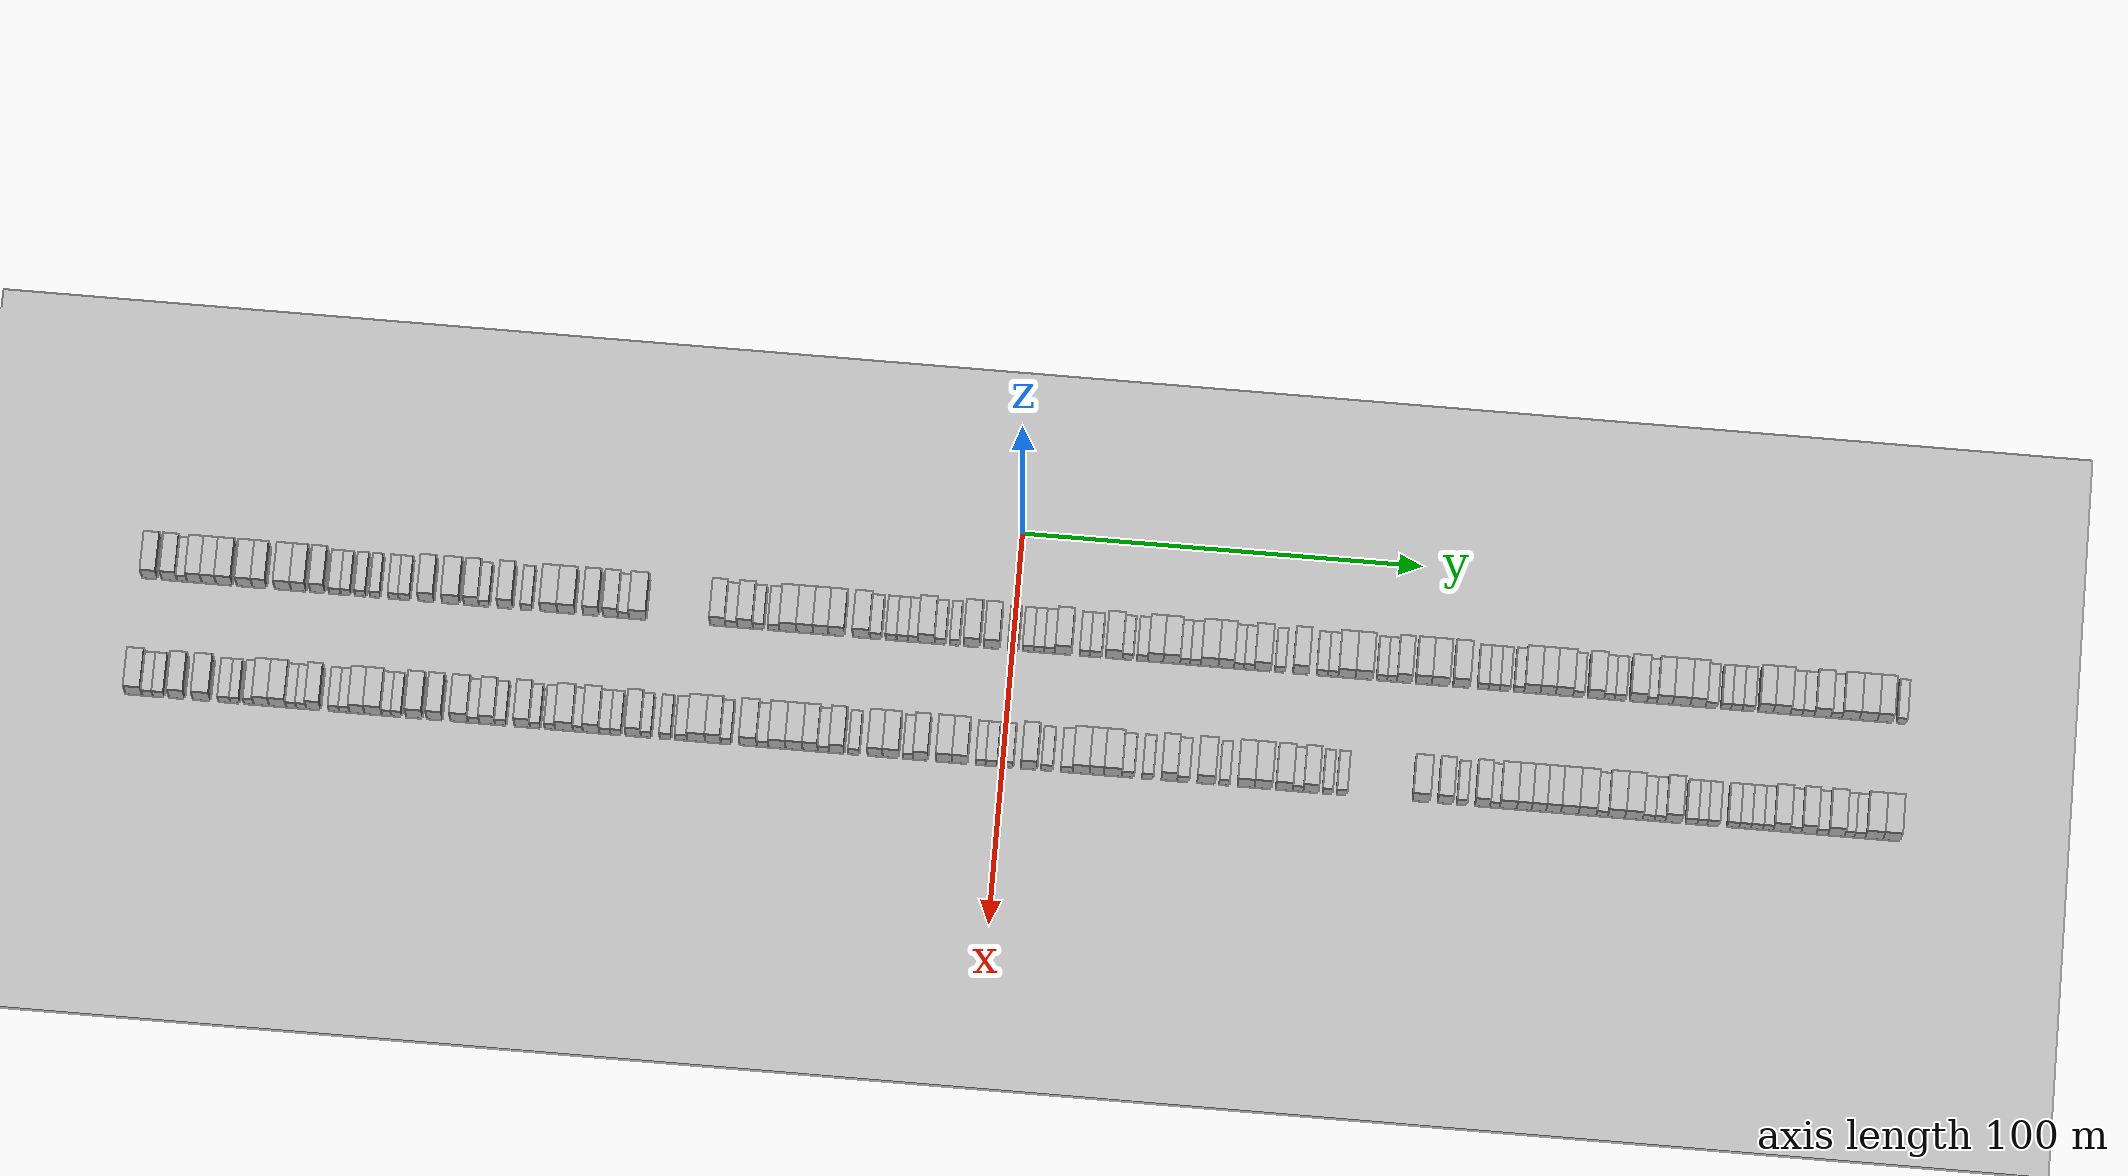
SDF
<?xml version="1.0" encoding="utf-8"?>

<sdf version="1.6">

   <world name="default">

      <gui fullscreen="0">

         <camera name="user_camera">

            <pose>-15 0 4.57585 0 0 0</pose>

            <view_controller>orbit</view_controller>

         </camera>

      </gui>

      <scene>

         <sky>

           <clouds>

             <speed>12</speed>

           </clouds>

         </sky>

         <ambient>0.4 0.4 0.4 1</ambient>

         <background>0.7 0.7 0.7 1</background>

         <shadows>1</shadows>

      </scene>

      <gravity>0 0 -9.8066</gravity>

      <magnetic_field>6e-06 2.3e-05 -4.2e-05</magnetic_field>

      <physics default="0" name="default_physics" type="ode">

         <ode>

            <solver>

               <type>quick</type>

               <iters>10</iters>

               <sor>1.0</sor>

               <use_dynamic_moi_rescaling>0</use_dynamic_moi_rescaling>

            </solver>

            <constraints>

               <cfm>0</cfm>

               <erp>0.2</erp>

               <contact_max_correcting_vel>100</contact_max_correcting_vel>

               <contact_surface_layer>0.001</contact_surface_layer>

            </constraints>

         </ode>

         <max_step_size>0.004</max_step_size>

         <real_time_factor>1</real_time_factor>

         <real_time_update_rate>250</real_time_update_rate>

      </physics>

      <light name="sun" type="directional">

         <cast_shadows>1</cast_shadows>

         <pose>0 0 10 0 0 0</pose>

         <diffuse>0.8 0.8 0.8 1</diffuse>

         <specular>0.2 0.2 0.2 1</specular>

         <attenuation>

            <range>1000</range>

            <constant>0.9</constant>

            <linear>0.01</linear>

            <quadratic>0.001</quadratic>

         </attenuation>

         <direction>-0.5 0.1 -0.9</direction>

      </light>

      <include>

         <name>ground_plane_1</name>

         <uri>model://HANNAS_ground_plane</uri>

         <pose>0 0 0  0 0 0</pose>

      </include>

      <include>

         <name>ground_plane_2</name>

         <uri>model://HANNAS_ground_plane</uri>

         <pose>100 0 0  0 0 0</pose>

      </include>

      <model name="building_1">

         <static>1</static>

         <pose frame="">25.0000 -216.0419 0 0.000000 0.000000 0.000000</pose>

         <link name="link">

            <pose frame="">0 0 4.50 0 0 0</pose>

            <collision name="collision">

               <geometry>

                  <box>

                     <size>10.0000 3.9163 9.0000</size>

                  </box>

               </geometry>

               <max_contacts>10</max_contacts>

               <surface>

                  <contact>

                     <ode/>

                  </contact>

                  <bounce/>

                  <friction>

                     <torsional>

                        <ode/>

                     </torsional>

                     <ode/>

                  </friction>

               </surface>

            </collision>

            <visual name="visual">

               <cast_shadows>0</cast_shadows>

               <geometry>

                  <box>

                     <size>10.0000 3.9163 9.0000</size>

                  </box>

               </geometry>

               <material>

                  <script>

                     <uri>model://HANNAS_wall/materials/scripts</uri>

                     <uri>model://HANNAS_wall/materials/textures</uri>

                     <name>vrc/HANNAS_wall</name>

                  </script>

               </material>

            </visual>

            <self_collide>0</self_collide>

            <enable_wind>0</enable_wind>

            <kinematic>0</kinematic>

         </link>

      </model>

      <model name="building_2">

         <static>1</static>

         <pose frame="">25.0000 -211.1497 0 0.000000 0.000000 0.000000</pose>

         <link name="link">

            <pose frame="">0 0 4.50 0 0 0</pose>

            <collision name="collision">

               <geometry>

                  <box>

                     <size>10.0000 3.8681 9.0000</size>

                  </box>

               </geometry>

               <max_contacts>10</max_contacts>

               <surface>

                  <contact>

                     <ode/>

                  </contact>

                  <bounce/>

                  <friction>

                     <torsional>

                        <ode/>

                     </torsional>

                     <ode/>

                  </friction>

               </surface>

            </collision>

            <visual name="visual">

               <cast_shadows>0</cast_shadows>

               <geometry>

                  <box>

                     <size>10.0000 3.8681 9.0000</size>

                  </box>

               </geometry>

               <material>

                  <script>

                     <uri>model://HANNAS_wall/materials/scripts</uri>

                     <uri>model://HANNAS_wall/materials/textures</uri>

                     <name>vrc/HANNAS_wall</name>

                  </script>

               </material>

            </visual>

            <self_collide>0</self_collide>

            <enable_wind>0</enable_wind>

            <kinematic>0</kinematic>

         </link>

      </model>

      <model name="building_3">

         <static>1</static>

         <pose frame="">25.0000 -207.9649 0 0.000000 0.000000 0.000000</pose>

         <link name="link">

            <pose frame="">0 0 3.00 0 0 0</pose>

            <collision name="collision">

               <geometry>

                  <box>

                     <size>10.0000 2.5015 6.0000</size>

                  </box>

               </geometry>

               <max_contacts>10</max_contacts>

               <surface>

                  <contact>

                     <ode/>

                  </contact>

                  <bounce/>

                  <friction>

                     <torsional>

                        <ode/>

                     </torsional>

                     <ode/>

                  </friction>

               </surface>

            </collision>

            <visual name="visual">

               <cast_shadows>0</cast_shadows>

               <geometry>

                  <box>

                     <size>10.0000 2.5015 6.0000</size>

                  </box>

               </geometry>

               <material>

                  <script>

                     <uri>model://HANNAS_wall/materials/scripts</uri>

                     <uri>model://HANNAS_wall/materials/textures</uri>

                     <name>vrc/HANNAS_wall</name>

                  </script>

               </material>

            </visual>

            <self_collide>0</self_collide>

            <enable_wind>0</enable_wind>

            <kinematic>0</kinematic>

         </link>

      </model>

      <model name="building_4">

         <static>1</static>

         <pose frame="">25.0000 -204.8783 0 0.000000 0.000000 0.000000</pose>

         <link name="link">

            <pose frame="">0 0 4.50 0 0 0</pose>

            <collision name="collision">

               <geometry>

                  <box>

                     <size>10.0000 3.6717 9.0000</size>

                  </box>

               </geometry>

               <max_contacts>10</max_contacts>

               <surface>

                  <contact>

                     <ode/>

                  </contact>

                  <bounce/>

                  <friction>

                     <torsional>

                        <ode/>

                     </torsional>

                     <ode/>

                  </friction>

               </surface>

            </collision>

            <visual name="visual">

               <cast_shadows>0</cast_shadows>

               <geometry>

                  <box>

                     <size>10.0000 3.6717 9.0000</size>

                  </box>

               </geometry>

               <material>

                  <script>

                     <uri>model://HANNAS_wall/materials/scripts</uri>

                     <uri>model://HANNAS_wall/materials/textures</uri>

                     <name>vrc/HANNAS_wall</name>

                  </script>

               </material>

            </visual>

            <self_collide>0</self_collide>

            <enable_wind>0</enable_wind>

            <kinematic>0</kinematic>

         </link>

      </model>

      <model name="building_5">

         <static>1</static>

         <pose frame="">25.0000 -201.2408 0 0.000000 0.000000 0.000000</pose>

         <link name="link">

            <pose frame="">0 0 4.50 0 0 0</pose>

            <collision name="collision">

               <geometry>

                  <box>

                     <size>10.0000 3.6034 9.0000</size>

                  </box>

               </geometry>

               <max_contacts>10</max_contacts>

               <surface>

                  <contact>

                     <ode/>

                  </contact>

                  <bounce/>

                  <friction>

                     <torsional>

                        <ode/>

                     </torsional>

                     <ode/>

                  </friction>

               </surface>

            </collision>

            <visual name="visual">

               <cast_shadows>0</cast_shadows>

               <geometry>

                  <box>

                     <size>10.0000 3.6034 9.0000</size>

                  </box>

               </geometry>

               <material>

                  <script>

                     <uri>model://HANNAS_wall/materials/scripts</uri>

                     <uri>model://HANNAS_wall/materials/textures</uri>

                     <name>vrc/HANNAS_wall</name>

                  </script>

               </material>

            </visual>

            <self_collide>0</self_collide>

            <enable_wind>0</enable_wind>

            <kinematic>0</kinematic>

         </link>

      </model>

      <model name="building_6">

         <static>1</static>

         <pose frame="">25.0000 -197.3695 0 0.000000 0.000000 0.000000</pose>

         <link name="link">

            <pose frame="">0 0 4.50 0 0 0</pose>

            <collision name="collision">

               <geometry>

                  <box>

                     <size>10.0000 4.1391 9.0000</size>

                  </box>

               </geometry>

               <max_contacts>10</max_contacts>

               <surface>

                  <contact>

                     <ode/>

                  </contact>

                  <bounce/>

                  <friction>

                     <torsional>

                        <ode/>

                     </torsional>

                     <ode/>

                  </friction>

               </surface>

            </collision>

            <visual name="visual">

               <cast_shadows>0</cast_shadows>

               <geometry>

                  <box>

                     <size>10.0000 4.1391 9.0000</size>

                  </box>

               </geometry>

               <material>

                  <script>

                     <uri>model://HANNAS_wall/materials/scripts</uri>

                     <uri>model://HANNAS_wall/materials/textures</uri>

                     <name>vrc/HANNAS_wall</name>

                  </script>

               </material>

            </visual>

            <self_collide>0</self_collide>

            <enable_wind>0</enable_wind>

            <kinematic>0</kinematic>

         </link>

      </model>

      <model name="building_7">

         <static>1</static>

         <pose frame="">25.0000 -192.3266 0 0.000000 0.000000 0.000000</pose>

         <link name="link">

            <pose frame="">0 0 4.50 0 0 0</pose>

            <collision name="collision">

               <geometry>

                  <box>

                     <size>10.0000 3.9469 9.0000</size>

                  </box>

               </geometry>

               <max_contacts>10</max_contacts>

               <surface>

                  <contact>

                     <ode/>

                  </contact>

                  <bounce/>

                  <friction>

                     <torsional>

                        <ode/>

                     </torsional>

                     <ode/>

                  </friction>

               </surface>

            </collision>

            <visual name="visual">

               <cast_shadows>0</cast_shadows>

               <geometry>

                  <box>

                     <size>10.0000 3.9469 9.0000</size>

                  </box>

               </geometry>

               <material>

                  <script>

                     <uri>model://HANNAS_wall/materials/scripts</uri>

                     <uri>model://HANNAS_wall/materials/textures</uri>

                     <name>vrc/HANNAS_wall</name>

                  </script>

               </material>

            </visual>

            <self_collide>0</self_collide>

            <enable_wind>0</enable_wind>

            <kinematic>0</kinematic>

         </link>

      </model>

      <model name="building_8">

         <static>1</static>

         <pose frame="">25.0000 -188.5478 0 0.000000 0.000000 0.000000</pose>

         <link name="link">

            <pose frame="">0 0 4.50 0 0 0</pose>

            <collision name="collision">

               <geometry>

                  <box>

                     <size>10.0000 3.6106 9.0000</size>

                  </box>

               </geometry>

               <max_contacts>10</max_contacts>

               <surface>

                  <contact>

                     <ode/>

                  </contact>

                  <bounce/>

                  <friction>

                     <torsional>

                        <ode/>

                     </torsional>

                     <ode/>

                  </friction>

               </surface>

            </collision>

            <visual name="visual">

               <cast_shadows>0</cast_shadows>

               <geometry>

                  <box>

                     <size>10.0000 3.6106 9.0000</size>

                  </box>

               </geometry>

               <material>

                  <script>

                     <uri>model://HANNAS_wall/materials/scripts</uri>

                     <uri>model://HANNAS_wall/materials/textures</uri>

                     <name>vrc/HANNAS_wall</name>

                  </script>

               </material>

            </visual>

            <self_collide>0</self_collide>

            <enable_wind>0</enable_wind>

            <kinematic>0</kinematic>

         </link>

      </model>

      <model name="building_9">

         <static>1</static>

         <pose frame="">25.0000 -182.7018 0 0.000000 0.000000 0.000000</pose>

         <link name="link">

            <pose frame="">0 0 4.50 0 0 0</pose>

            <collision name="collision">

               <geometry>

                  <box>

                     <size>10.0000 4.0816 9.0000</size>

                  </box>

               </geometry>

               <max_contacts>10</max_contacts>

               <surface>

                  <contact>

                     <ode/>

                  </contact>

                  <bounce/>

                  <friction>

                     <torsional>

                        <ode/>

                     </torsional>

                     <ode/>

                  </friction>

               </surface>

            </collision>

            <visual name="visual">

               <cast_shadows>0</cast_shadows>

               <geometry>

                  <box>

                     <size>10.0000 4.0816 9.0000</size>

                  </box>

               </geometry>

               <material>

                  <script>

                     <uri>model://HANNAS_wall/materials/scripts</uri>

                     <uri>model://HANNAS_wall/materials/textures</uri>

                     <name>vrc/HANNAS_wall</name>

                  </script>

               </material>

            </visual>

            <self_collide>0</self_collide>

            <enable_wind>0</enable_wind>

            <kinematic>0</kinematic>

         </link>

      </model>

      <model name="building_10">

         <static>1</static>

         <pose frame="">25.0000 -178.7619 0 0.000000 0.000000 0.000000</pose>

         <link name="link">

            <pose frame="">0 0 4.50 0 0 0</pose>

            <collision name="collision">

               <geometry>

                  <box>

                     <size>10.0000 3.7982 9.0000</size>

                  </box>

               </geometry>

               <max_contacts>10</max_contacts>

               <surface>

                  <contact>

                     <ode/>

                  </contact>

                  <bounce/>

                  <friction>

                     <torsional>

                        <ode/>

                     </torsional>

                     <ode/>

                  </friction>

               </surface>

            </collision>

            <visual name="visual">

               <cast_shadows>0</cast_shadows>

               <geometry>

                  <box>

                     <size>10.0000 3.7982 9.0000</size>

                  </box>

               </geometry>

               <material>

                  <script>

                     <uri>model://HANNAS_wall/materials/scripts</uri>

                     <uri>model://HANNAS_wall/materials/textures</uri>

                     <name>vrc/HANNAS_wall</name>

                  </script>

               </material>

            </visual>

            <self_collide>0</self_collide>

            <enable_wind>0</enable_wind>

            <kinematic>0</kinematic>

         </link>

      </model>

      <model name="building_11">

         <static>1</static>

         <pose frame="">25.0000 -174.0061 0 0.000000 0.000000 0.000000</pose>

         <link name="link">

            <pose frame="">0 0 4.50 0 0 0</pose>

            <collision name="collision">

               <geometry>

                  <box>

                     <size>10.0000 3.7134 9.0000</size>

                  </box>

               </geometry>

               <max_contacts>10</max_contacts>

               <surface>

                  <contact>

                     <ode/>

                  </contact>

                  <bounce/>

                  <friction>

                     <torsional>

                        <ode/>

                     </torsional>

                     <ode/>

                  </friction>

               </surface>

            </collision>

            <visual name="visual">

               <cast_shadows>0</cast_shadows>

               <geometry>

                  <box>

                     <size>10.0000 3.7134 9.0000</size>

                  </box>

               </geometry>

               <material>

                  <script>

                     <uri>model://HANNAS_wall/materials/scripts</uri>

                     <uri>model://HANNAS_wall/materials/textures</uri>

                     <name>vrc/HANNAS_wall</name>

                  </script>

               </material>

            </visual>

            <self_collide>0</self_collide>

            <enable_wind>0</enable_wind>

            <kinematic>0</kinematic>

         </link>

      </model>

      <model name="building_12">

         <static>1</static>

         <pose frame="">25.0000 -169.6747 0 0.000000 0.000000 0.000000</pose>

         <link name="link">

            <pose frame="">0 0 3.00 0 0 0</pose>

            <collision name="collision">

               <geometry>

                  <box>

                     <size>10.0000 2.9493 6.0000</size>

                  </box>

               </geometry>

               <max_contacts>10</max_contacts>

               <surface>

                  <contact>

                     <ode/>

                  </contact>

                  <bounce/>

                  <friction>

                     <torsional>

                        <ode/>

                     </torsional>

                     <ode/>

                  </friction>

               </surface>

            </collision>

            <visual name="visual">

               <cast_shadows>0</cast_shadows>

               <geometry>

                  <box>

                     <size>10.0000 2.9493 6.0000</size>

                  </box>

               </geometry>

               <material>

                  <script>

                     <uri>model://HANNAS_wall/materials/scripts</uri>

                     <uri>model://HANNAS_wall/materials/textures</uri>

                     <name>vrc/HANNAS_wall</name>

                  </script>

               </material>

            </visual>

            <self_collide>0</self_collide>

            <enable_wind>0</enable_wind>

            <kinematic>0</kinematic>

         </link>

      </model>

      <model name="building_13">

         <static>1</static>

         <pose frame="">25.0000 -166.9176 0 0.000000 0.000000 0.000000</pose>

         <link name="link">

            <pose frame="">0 0 3.00 0 0 0</pose>

            <collision name="collision">

               <geometry>

                  <box>

                     <size>10.0000 2.5648 6.0000</size>

                  </box>

               </geometry>

               <max_contacts>10</max_contacts>

               <surface>

                  <contact>

                     <ode/>

                  </contact>

                  <bounce/>

                  <friction>

                     <torsional>

                        <ode/>

                     </torsional>

                     <ode/>

                  </friction>

               </surface>

            </collision>

            <visual name="visual">

               <cast_shadows>0</cast_shadows>

               <geometry>

                  <box>

                     <size>10.0000 2.5648 6.0000</size>

                  </box>

               </geometry>

               <material>

                  <script>

                     <uri>model://HANNAS_wall/materials/scripts</uri>

                     <uri>model://HANNAS_wall/materials/textures</uri>

                     <name>vrc/HANNAS_wall</name>

                  </script>

               </material>

            </visual>

            <self_collide>0</self_collide>

            <enable_wind>0</enable_wind>

            <kinematic>0</kinematic>

         </link>

      </model>

      <model name="building_14">

         <static>1</static>

         <pose frame="">25.0000 -163.2379 0 0.000000 0.000000 0.000000</pose>

         <link name="link">

            <pose frame="">0 0 3.00 0 0 0</pose>

            <collision name="collision">

               <geometry>

                  <box>

                     <size>10.0000 2.7948 6.0000</size>

                  </box>

               </geometry>

               <max_contacts>10</max_contacts>

               <surface>

                  <contact>

                     <ode/>

                  </contact>

                  <bounce/>

                  <friction>

                     <torsional>

                        <ode/>

                     </torsional>

                     <ode/>

                  </friction>

               </surface>

            </collision>

            <visual name="visual">

               <cast_shadows>0</cast_shadows>

               <geometry>

                  <box>

                     <size>10.0000 2.7948 6.0000</size>

                  </box>

               </geometry>

               <material>

                  <script>

                     <uri>model://HANNAS_wall/materials/scripts</uri>

                     <uri>model://HANNAS_wall/materials/textures</uri>

                     <name>vrc/HANNAS_wall</name>

                  </script>

               </material>

            </visual>

            <self_collide>0</self_collide>

            <enable_wind>0</enable_wind>

            <kinematic>0</kinematic>

         </link>

      </model>

      <model name="building_15">

         <static>1</static>

         <pose frame="">25.0000 -159.5439 0 0.000000 0.000000 0.000000</pose>

         <link name="link">

            <pose frame="">0 0 3.00 0 0 0</pose>

            <collision name="collision">

               <geometry>

                  <box>

                     <size>10.0000 2.5931 6.0000</size>

                  </box>

               </geometry>

               <max_contacts>10</max_contacts>

               <surface>

                  <contact>

                     <ode/>

                  </contact>

                  <bounce/>

                  <friction>

                     <torsional>

                        <ode/>

                     </torsional>

                     <ode/>

                  </friction>

               </surface>

            </collision>

            <visual name="visual">

               <cast_shadows>0</cast_shadows>

               <geometry>

                  <box>

                     <size>10.0000 2.5931 6.0000</size>

                  </box>

               </geometry>

               <material>

                  <script>

                     <uri>model://HANNAS_wall/materials/scripts</uri>

                     <uri>model://HANNAS_wall/materials/textures</uri>

                     <name>vrc/HANNAS_wall</name>

                  </script>

               </material>

            </visual>

            <self_collide>0</self_collide>

            <enable_wind>0</enable_wind>

            <kinematic>0</kinematic>

         </link>

      </model>

      <model name="building_16">

         <static>1</static>

         <pose frame="">25.0000 -154.9799 0 0.000000 0.000000 0.000000</pose>

         <link name="link">

            <pose frame="">0 0 3.00 0 0 0</pose>

            <collision name="collision">

               <geometry>

                  <box>

                     <size>10.0000 2.5349 6.0000</size>

                  </box>

               </geometry>

               <max_contacts>10</max_contacts>

               <surface>

                  <contact>

                     <ode/>

                  </contact>

                  <bounce/>

                  <friction>

                     <torsional>

                        <ode/>

                     </torsional>

                     <ode/>

                  </friction>

               </surface>

            </collision>

            <visual name="visual">

               <cast_shadows>0</cast_shadows>

               <geometry>

                  <box>

                     <size>10.0000 2.5349 6.0000</size>

                  </box>

               </geometry>

               <material>

                  <script>

                     <uri>model://HANNAS_wall/materials/scripts</uri>

                     <uri>model://HANNAS_wall/materials/textures</uri>

                     <name>vrc/HANNAS_wall</name>

                  </script>

               </material>

            </visual>

            <self_collide>0</self_collide>

            <enable_wind>0</enable_wind>

            <kinematic>0</kinematic>

         </link>

      </model>

      <model name="building_17">

         <static>1</static>

         <pose frame="">25.0000 -152.2463 0 0.000000 0.000000 0.000000</pose>

         <link name="link">

            <pose frame="">0 0 3.00 0 0 0</pose>

            <collision name="collision">

               <geometry>

                  <box>

                     <size>10.0000 2.9323 6.0000</size>

                  </box>

               </geometry>

               <max_contacts>10</max_contacts>

               <surface>

                  <contact>

                     <ode/>

                  </contact>

                  <bounce/>

                  <friction>

                     <torsional>

                        <ode/>

                     </torsional>

                     <ode/>

                  </friction>

               </surface>

            </collision>

            <visual name="visual">

               <cast_shadows>0</cast_shadows>

               <geometry>

                  <box>

                     <size>10.0000 2.9323 6.0000</size>

                  </box>

               </geometry>

               <material>

                  <script>

                     <uri>model://HANNAS_wall/materials/scripts</uri>

                     <uri>model://HANNAS_wall/materials/textures</uri>

                     <name>vrc/HANNAS_wall</name>

                  </script>

               </material>

            </visual>

            <self_collide>0</self_collide>

            <enable_wind>0</enable_wind>

            <kinematic>0</kinematic>

         </link>

      </model>

      <model name="building_18">

         <static>1</static>

         <pose frame="">25.0000 -146.7901 0 0.000000 0.000000 0.000000</pose>

         <link name="link">

            <pose frame="">0 0 4.50 0 0 0</pose>

            <collision name="collision">

               <geometry>

                  <box>

                     <size>10.0000 3.9801 9.0000</size>

                  </box>

               </geometry>

               <max_contacts>10</max_contacts>

               <surface>

                  <contact>

                     <ode/>

                  </contact>

                  <bounce/>

                  <friction>

                     <torsional>

                        <ode/>

                     </torsional>

                     <ode/>

                  </friction>

               </surface>

            </collision>

            <visual name="visual">

               <cast_shadows>0</cast_shadows>

               <geometry>

                  <box>

                     <size>10.0000 3.9801 9.0000</size>

                  </box>

               </geometry>

               <material>

                  <script>

                     <uri>model://HANNAS_wall/materials/scripts</uri>

                     <uri>model://HANNAS_wall/materials/textures</uri>

                     <name>vrc/HANNAS_wall</name>

                  </script>

               </material>

            </visual>

            <self_collide>0</self_collide>

            <enable_wind>0</enable_wind>

            <kinematic>0</kinematic>

         </link>

      </model>

      <model name="building_19">

         <static>1</static>

         <pose frame="">25.0000 -140.5800 0 0.000000 0.000000 0.000000</pose>

         <link name="link">

            <pose frame="">0 0 4.50 0 0 0</pose>

            <collision name="collision">

               <geometry>

                  <box>

                     <size>10.0000 4.4402 9.0000</size>

                  </box>

               </geometry>

               <max_contacts>10</max_contacts>

               <surface>

                  <contact>

                     <ode/>

                  </contact>

                  <bounce/>

                  <friction>

                     <torsional>

                        <ode/>

                     </torsional>

                     <ode/>

                  </friction>

               </surface>

            </collision>

            <visual name="visual">

               <cast_shadows>0</cast_shadows>

               <geometry>

                  <box>

                     <size>10.0000 4.4402 9.0000</size>

                  </box>

               </geometry>

               <material>

                  <script>

                     <uri>model://HANNAS_wall/materials/scripts</uri>

                     <uri>model://HANNAS_wall/materials/textures</uri>

                     <name>vrc/HANNAS_wall</name>

                  </script>

               </material>

            </visual>

            <self_collide>0</self_collide>

            <enable_wind>0</enable_wind>

            <kinematic>0</kinematic>

         </link>

      </model>

      <model name="building_20">

         <static>1</static>

         <pose frame="">25.0000 -135.4775 0 0.000000 0.000000 0.000000</pose>

         <link name="link">

            <pose frame="">0 0 4.50 0 0 0</pose>

            <collision name="collision">

               <geometry>

                  <box>

                     <size>10.0000 3.7648 9.0000</size>

                  </box>

               </geometry>

               <max_contacts>10</max_contacts>

               <surface>

                  <contact>

                     <ode/>

                  </contact>

                  <bounce/>

                  <friction>

                     <torsional>

                        <ode/>

                     </torsional>

                     <ode/>

                  </friction>

               </surface>

            </collision>

            <visual name="visual">

               <cast_shadows>0</cast_shadows>

               <geometry>

                  <box>

                     <size>10.0000 3.7648 9.0000</size>

                  </box>

               </geometry>

               <material>

                  <script>

                     <uri>model://HANNAS_wall/materials/scripts</uri>

                     <uri>model://HANNAS_wall/materials/textures</uri>

                     <name>vrc/HANNAS_wall</name>

                  </script>

               </material>

            </visual>

            <self_collide>0</self_collide>

            <enable_wind>0</enable_wind>

            <kinematic>0</kinematic>

         </link>

      </model>

      <model name="building_21">

         <static>1</static>

         <pose frame="">25.0000 -132.2406 0 0.000000 0.000000 0.000000</pose>

         <link name="link">

            <pose frame="">0 0 3.00 0 0 0</pose>

            <collision name="collision">

               <geometry>

                  <box>

                     <size>10.0000 2.7090 6.0000</size>

                  </box>

               </geometry>

               <max_contacts>10</max_contacts>

               <surface>

                  <contact>

                     <ode/>

                  </contact>

                  <bounce/>

                  <friction>

                     <torsional>

                        <ode/>

                     </torsional>

                     <ode/>

                  </friction>

               </surface>

            </collision>

            <visual name="visual">

               <cast_shadows>0</cast_shadows>

               <geometry>

                  <box>

                     <size>10.0000 2.7090 6.0000</size>

                  </box>

               </geometry>

               <material>

                  <script>

                     <uri>model://HANNAS_wall/materials/scripts</uri>

                     <uri>model://HANNAS_wall/materials/textures</uri>

                     <name>vrc/HANNAS_wall</name>

                  </script>

               </material>

            </visual>

            <self_collide>0</self_collide>

            <enable_wind>0</enable_wind>

            <kinematic>0</kinematic>

         </link>

      </model>

      <model name="building_22">

         <static>1</static>

         <pose frame="">25.0000 -126.9891 0 0.000000 0.000000 0.000000</pose>

         <link name="link">

            <pose frame="">0 0 4.50 0 0 0</pose>

            <collision name="collision">

               <geometry>

                  <box>

                     <size>10.0000 3.7940 9.0000</size>

                  </box>

               </geometry>

               <max_contacts>10</max_contacts>

               <surface>

                  <contact>

                     <ode/>

                  </contact>

                  <bounce/>

                  <friction>

                     <torsional>

                        <ode/>

                     </torsional>

                     <ode/>

                  </friction>

               </surface>

            </collision>

            <visual name="visual">

               <cast_shadows>0</cast_shadows>

               <geometry>

                  <box>

                     <size>10.0000 3.7940 9.0000</size>

                  </box>

               </geometry>

               <material>

                  <script>

                     <uri>model://HANNAS_wall/materials/scripts</uri>

                     <uri>model://HANNAS_wall/materials/textures</uri>

                     <name>vrc/HANNAS_wall</name>

                  </script>

               </material>

            </visual>

            <self_collide>0</self_collide>

            <enable_wind>0</enable_wind>

            <kinematic>0</kinematic>

         </link>

      </model>

      <model name="building_23">

         <static>1</static>

         <pose frame="">25.0000 -121.6589 0 0.000000 0.000000 0.000000</pose>

         <link name="link">

            <pose frame="">0 0 3.00 0 0 0</pose>

            <collision name="collision">

               <geometry>

                  <box>

                     <size>10.0000 2.8664 6.0000</size>

                  </box>

               </geometry>

               <max_contacts>10</max_contacts>

               <surface>

                  <contact>

                     <ode/>

                  </contact>

                  <bounce/>

                  <friction>

                     <torsional>

                        <ode/>

                     </torsional>

                     <ode/>

                  </friction>

               </surface>

            </collision>

            <visual name="visual">

               <cast_shadows>0</cast_shadows>

               <geometry>

                  <box>

                     <size>10.0000 2.8664 6.0000</size>

                  </box>

               </geometry>

               <material>

                  <script>

                     <uri>model://HANNAS_wall/materials/scripts</uri>

                     <uri>model://HANNAS_wall/materials/textures</uri>

                     <name>vrc/HANNAS_wall</name>

                  </script>

               </material>

            </visual>

            <self_collide>0</self_collide>

            <enable_wind>0</enable_wind>

            <kinematic>0</kinematic>

         </link>

      </model>

      <model name="building_24">

         <static>1</static>

         <pose frame="">25.0000 -116.0984 0 0.000000 0.000000 0.000000</pose>

         <link name="link">

            <pose frame="">0 0 4.50 0 0 0</pose>

            <collision name="collision">

               <geometry>

                  <box>

                     <size>10.0000 4.2546 9.0000</size>

                  </box>

               </geometry>

               <max_contacts>10</max_contacts>

               <surface>

                  <contact>

                     <ode/>

                  </contact>

                  <bounce/>

                  <friction>

                     <torsional>

                        <ode/>

                     </torsional>

                     <ode/>

                  </friction>

               </surface>

            </collision>

            <visual name="visual">

               <cast_shadows>0</cast_shadows>

               <geometry>

                  <box>

                     <size>10.0000 4.2546 9.0000</size>

                  </box>

               </geometry>

               <material>

                  <script>

                     <uri>model://HANNAS_wall/materials/scripts</uri>

                     <uri>model://HANNAS_wall/materials/textures</uri>

                     <name>vrc/HANNAS_wall</name>

                  </script>

               </material>

            </visual>

            <self_collide>0</self_collide>

            <enable_wind>0</enable_wind>

            <kinematic>0</kinematic>

         </link>

      </model>

      <model name="building_25">

         <static>1</static>

         <pose frame="">25.0000 -111.7449 0 0.000000 0.000000 0.000000</pose>

         <link name="link">

            <pose frame="">0 0 4.50 0 0 0</pose>

            <collision name="collision">

               <geometry>

                  <box>

                     <size>10.0000 4.4524 9.0000</size>

                  </box>

               </geometry>

               <max_contacts>10</max_contacts>

               <surface>

                  <contact>

                     <ode/>

                  </contact>

                  <bounce/>

                  <friction>

                     <torsional>

                        <ode/>

                     </torsional>

                     <ode/>

                  </friction>

               </surface>

            </collision>

            <visual name="visual">

               <cast_shadows>0</cast_shadows>

               <geometry>

                  <box>

                     <size>10.0000 4.4524 9.0000</size>

                  </box>

               </geometry>

               <material>

                  <script>

                     <uri>model://HANNAS_wall/materials/scripts</uri>

                     <uri>model://HANNAS_wall/materials/textures</uri>

                     <name>vrc/HANNAS_wall</name>

                  </script>

               </material>

            </visual>

            <self_collide>0</self_collide>

            <enable_wind>0</enable_wind>

            <kinematic>0</kinematic>

         </link>

      </model>

      <model name="building_26">

         <static>1</static>

         <pose frame="">25.0000 -105.5380 0 0.000000 0.000000 0.000000</pose>

         <link name="link">

            <pose frame="">0 0 4.50 0 0 0</pose>

            <collision name="collision">

               <geometry>

                  <box>

                     <size>10.0000 3.9613 9.0000</size>

                  </box>

               </geometry>

               <max_contacts>10</max_contacts>

               <surface>

                  <contact>

                     <ode/>

                  </contact>

                  <bounce/>

                  <friction>

                     <torsional>

                        <ode/>

                     </torsional>

                     <ode/>

                  </friction>

               </surface>

            </collision>

            <visual name="visual">

               <cast_shadows>0</cast_shadows>

               <geometry>

                  <box>

                     <size>10.0000 3.9613 9.0000</size>

                  </box>

               </geometry>

               <material>

                  <script>

                     <uri>model://HANNAS_wall/materials/scripts</uri>

                     <uri>model://HANNAS_wall/materials/textures</uri>

                     <name>vrc/HANNAS_wall</name>

                  </script>

               </material>

            </visual>

            <self_collide>0</self_collide>

            <enable_wind>0</enable_wind>

            <kinematic>0</kinematic>

         </link>

      </model>

      <model name="building_27">

         <static>1</static>

         <pose frame="">25.0000 -100.6645 0 0.000000 0.000000 0.000000</pose>

         <link name="link">

            <pose frame="">0 0 4.50 0 0 0</pose>

            <collision name="collision">

               <geometry>

                  <box>

                     <size>10.0000 3.7857 9.0000</size>

                  </box>

               </geometry>

               <max_contacts>10</max_contacts>

               <surface>

                  <contact>

                     <ode/>

                  </contact>

                  <bounce/>

                  <friction>

                     <torsional>

                        <ode/>

                     </torsional>

                     <ode/>

                  </friction>

               </surface>

            </collision>

            <visual name="visual">

               <cast_shadows>0</cast_shadows>

               <geometry>

                  <box>

                     <size>10.0000 3.7857 9.0000</size>

                  </box>

               </geometry>

               <material>

                  <script>

                     <uri>model://HANNAS_wall/materials/scripts</uri>

                     <uri>model://HANNAS_wall/materials/textures</uri>

                     <name>vrc/HANNAS_wall</name>

                  </script>

               </material>

            </visual>

            <self_collide>0</self_collide>

            <enable_wind>0</enable_wind>

            <kinematic>0</kinematic>

         </link>

      </model>

      <model name="building_28">

         <static>1</static>

         <pose frame="">25.0000 -97.4327 0 0.000000 0.000000 0.000000</pose>

         <link name="link">

            <pose frame="">0 0 3.00 0 0 0</pose>

            <collision name="collision">

               <geometry>

                  <box>

                     <size>10.0000 2.6779 6.0000</size>

                  </box>

               </geometry>

               <max_contacts>10</max_contacts>

               <surface>

                  <contact>

                     <ode/>

                  </contact>

                  <bounce/>

                  <friction>

                     <torsional>

                        <ode/>

                     </torsional>

                     <ode/>

                  </friction>

               </surface>

            </collision>

            <visual name="visual">

               <cast_shadows>0</cast_shadows>

               <geometry>

                  <box>

                     <size>10.0000 2.6779 6.0000</size>

                  </box>

               </geometry>

               <material>

                  <script>

                     <uri>model://HANNAS_wall/materials/scripts</uri>

                     <uri>model://HANNAS_wall/materials/textures</uri>

                     <name>vrc/HANNAS_wall</name>

                  </script>

               </material>

            </visual>

            <self_collide>0</self_collide>

            <enable_wind>0</enable_wind>

            <kinematic>0</kinematic>

         </link>

      </model>

      <model name="building_29">

         <static>1</static>

         <pose frame="">25.0000 -93.8877 0 0.000000 0.000000 0.000000</pose>

         <link name="link">

            <pose frame="">0 0 4.50 0 0 0</pose>

            <collision name="collision">

               <geometry>

                  <box>

                     <size>10.0000 4.4122 9.0000</size>

                  </box>

               </geometry>

               <max_contacts>10</max_contacts>

               <surface>

                  <contact>

                     <ode/>

                  </contact>

                  <bounce/>

                  <friction>

                     <torsional>

                        <ode/>

                     </torsional>

                     <ode/>

                  </friction>

               </surface>

            </collision>

            <visual name="visual">

               <cast_shadows>0</cast_shadows>

               <geometry>

                  <box>

                     <size>10.0000 4.4122 9.0000</size>

                  </box>

               </geometry>

               <material>

                  <script>

                     <uri>model://HANNAS_wall/materials/scripts</uri>

                     <uri>model://HANNAS_wall/materials/textures</uri>

                     <name>vrc/HANNAS_wall</name>

                  </script>

               </material>

            </visual>

            <self_collide>0</self_collide>

            <enable_wind>0</enable_wind>

            <kinematic>0</kinematic>

         </link>

      </model>

      <model name="building_30">

         <static>1</static>

         <pose frame="">25.0000 -73.9153 0 0.000000 0.000000 0.000000</pose>

         <link name="link">

            <pose frame="">0 0 4.50 0 0 0</pose>

            <collision name="collision">

               <geometry>

                  <box>

                     <size>10.0000 3.8442 9.0000</size>

                  </box>

               </geometry>

               <max_contacts>10</max_contacts>

               <surface>

                  <contact>

                     <ode/>

                  </contact>

                  <bounce/>

                  <friction>

                     <torsional>

                        <ode/>

                     </torsional>

                     <ode/>

                  </friction>

               </surface>

            </collision>

            <visual name="visual">

               <cast_shadows>0</cast_shadows>

               <geometry>

                  <box>

                     <size>10.0000 3.8442 9.0000</size>

                  </box>

               </geometry>

               <material>

                  <script>

                     <uri>model://HANNAS_wall/materials/scripts</uri>

                     <uri>model://HANNAS_wall/materials/textures</uri>

                     <name>vrc/HANNAS_wall</name>

                  </script>

               </material>

            </visual>

            <self_collide>0</self_collide>

            <enable_wind>0</enable_wind>

            <kinematic>0</kinematic>

         </link>

      </model>

      <model name="building_31">

         <static>1</static>

         <pose frame="">25.0000 -70.5167 0 0.000000 0.000000 0.000000</pose>

         <link name="link">

            <pose frame="">0 0 3.00 0 0 0</pose>

            <collision name="collision">

               <geometry>

                  <box>

                     <size>10.0000 2.9530 6.0000</size>

                  </box>

               </geometry>

               <max_contacts>10</max_contacts>

               <surface>

                  <contact>

                     <ode/>

                  </contact>

                  <bounce/>

                  <friction>

                     <torsional>

                        <ode/>

                     </torsional>

                     <ode/>

                  </friction>

               </surface>

            </collision>

            <visual name="visual">

               <cast_shadows>0</cast_shadows>

               <geometry>

                  <box>

                     <size>10.0000 2.9530 6.0000</size>

                  </box>

               </geometry>

               <material>

                  <script>

                     <uri>model://HANNAS_wall/materials/scripts</uri>

                     <uri>model://HANNAS_wall/materials/textures</uri>

                     <name>vrc/HANNAS_wall</name>

                  </script>

               </material>

            </visual>

            <self_collide>0</self_collide>

            <enable_wind>0</enable_wind>

            <kinematic>0</kinematic>

         </link>

      </model>

      <model name="building_32">

         <static>1</static>

         <pose frame="">25.0000 -67.0699 0 0.000000 0.000000 0.000000</pose>

         <link name="link">

            <pose frame="">0 0 4.50 0 0 0</pose>

            <collision name="collision">

               <geometry>

                  <box>

                     <size>10.0000 3.9406 9.0000</size>

                  </box>

               </geometry>

               <max_contacts>10</max_contacts>

               <surface>

                  <contact>

                     <ode/>

                  </contact>

                  <bounce/>

                  <friction>

                     <torsional>

                        <ode/>

                     </torsional>

                     <ode/>

                  </friction>

               </surface>

            </collision>

            <visual name="visual">

               <cast_shadows>0</cast_shadows>

               <geometry>

                  <box>

                     <size>10.0000 3.9406 9.0000</size>

                  </box>

               </geometry>

               <material>

                  <script>

                     <uri>model://HANNAS_wall/materials/scripts</uri>

                     <uri>model://HANNAS_wall/materials/textures</uri>

                     <name>vrc/HANNAS_wall</name>

                  </script>

               </material>

            </visual>

            <self_collide>0</self_collide>

            <enable_wind>0</enable_wind>

            <kinematic>0</kinematic>

         </link>

      </model>

      <model name="building_33">

         <static>1</static>

         <pose frame="">25.0000 -63.7086 0 0.000000 0.000000 0.000000</pose>

         <link name="link">

            <pose frame="">0 0 3.00 0 0 0</pose>

            <collision name="collision">

               <geometry>

                  <box>

                     <size>10.0000 2.7819 6.0000</size>

                  </box>

               </geometry>

               <max_contacts>10</max_contacts>

               <surface>

                  <contact>

                     <ode/>

                  </contact>

                  <bounce/>

                  <friction>

                     <torsional>

                        <ode/>

                     </torsional>

                     <ode/>

                  </friction>

               </surface>

            </collision>

            <visual name="visual">

               <cast_shadows>0</cast_shadows>

               <geometry>

                  <box>

                     <size>10.0000 2.7819 6.0000</size>

                  </box>

               </geometry>

               <material>

                  <script>

                     <uri>model://HANNAS_wall/materials/scripts</uri>

                     <uri>model://HANNAS_wall/materials/textures</uri>

                     <name>vrc/HANNAS_wall</name>

                  </script>

               </material>

            </visual>

            <self_collide>0</self_collide>

            <enable_wind>0</enable_wind>

            <kinematic>0</kinematic>

         </link>

      </model>

      <model name="building_34">

         <static>1</static>

         <pose frame="">25.0000 -59.8880 0 0.000000 0.000000 0.000000</pose>

         <link name="link">

            <pose frame="">0 0 3.00 0 0 0</pose>

            <collision name="collision">

               <geometry>

                  <box>

                     <size>10.0000 2.8595 6.0000</size>

                  </box>

               </geometry>

               <max_contacts>10</max_contacts>

               <surface>

                  <contact>

                     <ode/>

                  </contact>

                  <bounce/>

                  <friction>

                     <torsional>

                        <ode/>

                     </torsional>

                     <ode/>

                  </friction>

               </surface>

            </collision>

            <visual name="visual">

               <cast_shadows>0</cast_shadows>

               <geometry>

                  <box>

                     <size>10.0000 2.8595 6.0000</size>

                  </box>

               </geometry>

               <material>

                  <script>

                     <uri>model://HANNAS_wall/materials/scripts</uri>

                     <uri>model://HANNAS_wall/materials/textures</uri>

                     <name>vrc/HANNAS_wall</name>

                  </script>

               </material>

            </visual>

            <self_collide>0</self_collide>

            <enable_wind>0</enable_wind>

            <kinematic>0</kinematic>

         </link>

      </model>

      <model name="building_35">

         <static>1</static>

         <pose frame="">25.0000 -56.3166 0 0.000000 0.000000 0.000000</pose>

         <link name="link">

            <pose frame="">0 0 4.50 0 0 0</pose>

            <collision name="collision">

               <geometry>

                  <box>

                     <size>10.0000 4.2833 9.0000</size>

                  </box>

               </geometry>

               <max_contacts>10</max_contacts>

               <surface>

                  <contact>

                     <ode/>

                  </contact>

                  <bounce/>

                  <friction>

                     <torsional>

                        <ode/>

                     </torsional>

                     <ode/>

                  </friction>

               </surface>

            </collision>

            <visual name="visual">

               <cast_shadows>0</cast_shadows>

               <geometry>

                  <box>

                     <size>10.0000 4.2833 9.0000</size>

                  </box>

               </geometry>

               <material>

                  <script>

                     <uri>model://HANNAS_wall/materials/scripts</uri>

                     <uri>model://HANNAS_wall/materials/textures</uri>

                     <name>vrc/HANNAS_wall</name>

                  </script>

               </material>

            </visual>

            <self_collide>0</self_collide>

            <enable_wind>0</enable_wind>

            <kinematic>0</kinematic>

         </link>

      </model>

      <model name="building_36">

         <static>1</static>

         <pose frame="">25.0000 -52.1268 0 0.000000 0.000000 0.000000</pose>

         <link name="link">

            <pose frame="">0 0 4.50 0 0 0</pose>

            <collision name="collision">

               <geometry>

                  <box>

                     <size>10.0000 4.0962 9.0000</size>

                  </box>

               </geometry>

               <max_contacts>10</max_contacts>

               <surface>

                  <contact>

                     <ode/>

                  </contact>

                  <bounce/>

                  <friction>

                     <torsional>

                        <ode/>

                     </torsional>

                     <ode/>

                  </friction>

               </surface>

            </collision>

            <visual name="visual">

               <cast_shadows>0</cast_shadows>

               <geometry>

                  <box>

                     <size>10.0000 4.0962 9.0000</size>

                  </box>

               </geometry>

               <material>

                  <script>

                     <uri>model://HANNAS_wall/materials/scripts</uri>

                     <uri>model://HANNAS_wall/materials/textures</uri>

                     <name>vrc/HANNAS_wall</name>

                  </script>

               </material>

            </visual>

            <self_collide>0</self_collide>

            <enable_wind>0</enable_wind>

            <kinematic>0</kinematic>

         </link>

      </model>

      <model name="building_37">

         <static>1</static>

         <pose frame="">25.0000 -48.1381 0 0.000000 0.000000 0.000000</pose>

         <link name="link">

            <pose frame="">0 0 4.50 0 0 0</pose>

            <collision name="collision">

               <geometry>

                  <box>

                     <size>10.0000 3.8812 9.0000</size>

                  </box>

               </geometry>

               <max_contacts>10</max_contacts>

               <surface>

                  <contact>

                     <ode/>

                  </contact>

                  <bounce/>

                  <friction>

                     <torsional>

                        <ode/>

                     </torsional>

                     <ode/>

                  </friction>

               </surface>

            </collision>

            <visual name="visual">

               <cast_shadows>0</cast_shadows>

               <geometry>

                  <box>

                     <size>10.0000 3.8812 9.0000</size>

                  </box>

               </geometry>

               <material>

                  <script>

                     <uri>model://HANNAS_wall/materials/scripts</uri>

                     <uri>model://HANNAS_wall/materials/textures</uri>

                     <name>vrc/HANNAS_wall</name>

                  </script>

               </material>

            </visual>

            <self_collide>0</self_collide>

            <enable_wind>0</enable_wind>

            <kinematic>0</kinematic>

         </link>

      </model>

      <model name="building_38">

         <static>1</static>

         <pose frame="">25.0000 -44.1700 0 0.000000 0.000000 0.000000</pose>

         <link name="link">

            <pose frame="">0 0 4.50 0 0 0</pose>

            <collision name="collision">

               <geometry>

                  <box>

                     <size>10.0000 4.0550 9.0000</size>

                  </box>

               </geometry>

               <max_contacts>10</max_contacts>

               <surface>

                  <contact>

                     <ode/>

                  </contact>

                  <bounce/>

                  <friction>

                     <torsional>

                        <ode/>

                     </torsional>

                     <ode/>

                  </friction>

               </surface>

            </collision>

            <visual name="visual">

               <cast_shadows>0</cast_shadows>

               <geometry>

                  <box>

                     <size>10.0000 4.0550 9.0000</size>

                  </box>

               </geometry>

               <material>

                  <script>

                     <uri>model://HANNAS_wall/materials/scripts</uri>

                     <uri>model://HANNAS_wall/materials/textures</uri>

                     <name>vrc/HANNAS_wall</name>

                  </script>

               </material>

            </visual>

            <self_collide>0</self_collide>

            <enable_wind>0</enable_wind>

            <kinematic>0</kinematic>

         </link>

      </model>

      <model name="building_39">

         <static>1</static>

         <pose frame="">25.0000 -38.0258 0 0.000000 0.000000 0.000000</pose>

         <link name="link">

            <pose frame="">0 0 4.50 0 0 0</pose>

            <collision name="collision">

               <geometry>

                  <box>

                     <size>10.0000 4.2335 9.0000</size>

                  </box>

               </geometry>

               <max_contacts>10</max_contacts>

               <surface>

                  <contact>

                     <ode/>

                  </contact>

                  <bounce/>

                  <friction>

                     <torsional>

                        <ode/>

                     </torsional>

                     <ode/>

                  </friction>

               </surface>

            </collision>

            <visual name="visual">

               <cast_shadows>0</cast_shadows>

               <geometry>

                  <box>

                     <size>10.0000 4.2335 9.0000</size>

                  </box>

               </geometry>

               <material>

                  <script>

                     <uri>model://HANNAS_wall/materials/scripts</uri>

                     <uri>model://HANNAS_wall/materials/textures</uri>

                     <name>vrc/HANNAS_wall</name>

                  </script>

               </material>

            </visual>

            <self_collide>0</self_collide>

            <enable_wind>0</enable_wind>

            <kinematic>0</kinematic>

         </link>

      </model>

      <model name="building_40">

         <static>1</static>

         <pose frame="">25.0000 -34.4165 0 0.000000 0.000000 0.000000</pose>

         <link name="link">

            <pose frame="">0 0 3.00 0 0 0</pose>

            <collision name="collision">

               <geometry>

                  <box>

                     <size>10.0000 2.9851 6.0000</size>

                  </box>

               </geometry>

               <max_contacts>10</max_contacts>

               <surface>

                  <contact>

                     <ode/>

                  </contact>

                  <bounce/>

                  <friction>

                     <torsional>

                        <ode/>

                     </torsional>

                     <ode/>

                  </friction>

               </surface>

            </collision>

            <visual name="visual">

               <cast_shadows>0</cast_shadows>

               <geometry>

                  <box>

                     <size>10.0000 2.9851 6.0000</size>

                  </box>

               </geometry>

               <material>

                  <script>

                     <uri>model://HANNAS_wall/materials/scripts</uri>

                     <uri>model://HANNAS_wall/materials/textures</uri>

                     <name>vrc/HANNAS_wall</name>

                  </script>

               </material>

            </visual>

            <self_collide>0</self_collide>

            <enable_wind>0</enable_wind>

            <kinematic>0</kinematic>

         </link>

      </model>

      <model name="building_41">

         <static>1</static>

         <pose frame="">25.0000 -30.5574 0 0.000000 0.000000 0.000000</pose>

         <link name="link">

            <pose frame="">0 0 3.00 0 0 0</pose>

            <collision name="collision">

               <geometry>

                  <box>

                     <size>10.0000 2.7331 6.0000</size>

                  </box>

               </geometry>

               <max_contacts>10</max_contacts>

               <surface>

                  <contact>

                     <ode/>

                  </contact>

                  <bounce/>

                  <friction>

                     <torsional>

                        <ode/>

                     </torsional>

                     <ode/>

                  </friction>

               </surface>

            </collision>

            <visual name="visual">

               <cast_shadows>0</cast_shadows>

               <geometry>

                  <box>

                     <size>10.0000 2.7331 6.0000</size>

                  </box>

               </geometry>

               <material>

                  <script>

                     <uri>model://HANNAS_wall/materials/scripts</uri>

                     <uri>model://HANNAS_wall/materials/textures</uri>

                     <name>vrc/HANNAS_wall</name>

                  </script>

               </material>

            </visual>

            <self_collide>0</self_collide>

            <enable_wind>0</enable_wind>

            <kinematic>0</kinematic>

         </link>

      </model>

      <model name="building_42">

         <static>1</static>

         <pose frame="">25.0000 -27.7412 0 0.000000 0.000000 0.000000</pose>

         <link name="link">

            <pose frame="">0 0 3.00 0 0 0</pose>

            <collision name="collision">

               <geometry>

                  <box>

                     <size>10.0000 2.8993 6.0000</size>

                  </box>

               </geometry>

               <max_contacts>10</max_contacts>

               <surface>

                  <contact>

                     <ode/>

                  </contact>

                  <bounce/>

                  <friction>

                     <torsional>

                        <ode/>

                     </torsional>

                     <ode/>

                  </friction>

               </surface>

            </collision>

            <visual name="visual">

               <cast_shadows>0</cast_shadows>

               <geometry>

                  <box>

                     <size>10.0000 2.8993 6.0000</size>

                  </box>

               </geometry>

               <material>

                  <script>

                     <uri>model://HANNAS_wall/materials/scripts</uri>

                     <uri>model://HANNAS_wall/materials/textures</uri>

                     <name>vrc/HANNAS_wall</name>

                  </script>

               </material>

            </visual>

            <self_collide>0</self_collide>

            <enable_wind>0</enable_wind>

            <kinematic>0</kinematic>

         </link>

      </model>

      <model name="building_43">

         <static>1</static>

         <pose frame="">25.0000 -25.0822 0 0.000000 0.000000 0.000000</pose>

         <link name="link">

            <pose frame="">0 0 3.00 0 0 0</pose>

            <collision name="collision">

               <geometry>

                  <box>

                     <size>10.0000 2.4186 6.0000</size>

                  </box>

               </geometry>

               <max_contacts>10</max_contacts>

               <surface>

                  <contact>

                     <ode/>

                  </contact>

                  <bounce/>

                  <friction>

                     <torsional>

                        <ode/>

                     </torsional>

                     <ode/>

                  </friction>

               </surface>

            </collision>

            <visual name="visual">

               <cast_shadows>0</cast_shadows>

               <geometry>

                  <box>

                     <size>10.0000 2.4186 6.0000</size>

                  </box>

               </geometry>

               <material>

                  <script>

                     <uri>model://HANNAS_wall/materials/scripts</uri>

                     <uri>model://HANNAS_wall/materials/textures</uri>

                     <name>vrc/HANNAS_wall</name>

                  </script>

               </material>

            </visual>

            <self_collide>0</self_collide>

            <enable_wind>0</enable_wind>

            <kinematic>0</kinematic>

         </link>

      </model>

      <model name="building_44">

         <static>1</static>

         <pose frame="">25.0000 -21.7755 0 0.000000 0.000000 0.000000</pose>

         <link name="link">

            <pose frame="">0 0 4.50 0 0 0</pose>

            <collision name="collision">

               <geometry>

                  <box>

                     <size>10.0000 4.1948 9.0000</size>

                  </box>

               </geometry>

               <max_contacts>10</max_contacts>

               <surface>

                  <contact>

                     <ode/>

                  </contact>

                  <bounce/>

                  <friction>

                     <torsional>

                        <ode/>

                     </torsional>

                     <ode/>

                  </friction>

               </surface>

            </collision>

            <visual name="visual">

               <cast_shadows>0</cast_shadows>

               <geometry>

                  <box>

                     <size>10.0000 4.1948 9.0000</size>

                  </box>

               </geometry>

               <material>

                  <script>

                     <uri>model://HANNAS_wall/materials/scripts</uri>

                     <uri>model://HANNAS_wall/materials/textures</uri>

                     <name>vrc/HANNAS_wall</name>

                  </script>

               </material>

            </visual>

            <self_collide>0</self_collide>

            <enable_wind>0</enable_wind>

            <kinematic>0</kinematic>

         </link>

      </model>

      <model name="building_45">

         <static>1</static>

         <pose frame="">25.0000 -18.2840 0 0.000000 0.000000 0.000000</pose>

         <link name="link">

            <pose frame="">0 0 3.00 0 0 0</pose>

            <collision name="collision">

               <geometry>

                  <box>

                     <size>10.0000 2.7881 6.0000</size>

                  </box>

               </geometry>

               <max_contacts>10</max_contacts>

               <surface>

                  <contact>

                     <ode/>

                  </contact>

                  <bounce/>

                  <friction>

                     <torsional>

                        <ode/>

                     </torsional>

                     <ode/>

                  </friction>

               </surface>

            </collision>

            <visual name="visual">

               <cast_shadows>0</cast_shadows>

               <geometry>

                  <box>

                     <size>10.0000 2.7881 6.0000</size>

                  </box>

               </geometry>

               <material>

                  <script>

                     <uri>model://HANNAS_wall/materials/scripts</uri>

                     <uri>model://HANNAS_wall/materials/textures</uri>

                     <name>vrc/HANNAS_wall</name>

                  </script>

               </material>

            </visual>

            <self_collide>0</self_collide>

            <enable_wind>0</enable_wind>

            <kinematic>0</kinematic>

         </link>

      </model>

      <model name="building_46">

         <static>1</static>

         <pose frame="">25.0000 -14.6642 0 0.000000 0.000000 0.000000</pose>

         <link name="link">

            <pose frame="">0 0 3.00 0 0 0</pose>

            <collision name="collision">

               <geometry>

                  <box>

                     <size>10.0000 2.4515 6.0000</size>

                  </box>

               </geometry>

               <max_contacts>10</max_contacts>

               <surface>

                  <contact>

                     <ode/>

                  </contact>

                  <bounce/>

                  <friction>

                     <torsional>

                        <ode/>

                     </torsional>

                     <ode/>

                  </friction>

               </surface>

            </collision>

            <visual name="visual">

               <cast_shadows>0</cast_shadows>

               <geometry>

                  <box>

                     <size>10.0000 2.4515 6.0000</size>

                  </box>

               </geometry>

               <material>

                  <script>

                     <uri>model://HANNAS_wall/materials/scripts</uri>

                     <uri>model://HANNAS_wall/materials/textures</uri>

                     <name>vrc/HANNAS_wall</name>

                  </script>

               </material>

            </visual>

            <self_collide>0</self_collide>

            <enable_wind>0</enable_wind>

            <kinematic>0</kinematic>

         </link>

      </model>

      <model name="building_47">

         <static>1</static>

         <pose frame="">25.0000 -10.3760 0 0.000000 0.000000 0.000000</pose>

         <link name="link">

            <pose frame="">0 0 4.50 0 0 0</pose>

            <collision name="collision">

               <geometry>

                  <box>

                     <size>10.0000 4.1250 9.0000</size>

                  </box>

               </geometry>

               <max_contacts>10</max_contacts>

               <surface>

                  <contact>

                     <ode/>

                  </contact>

                  <bounce/>

                  <friction>

                     <torsional>

                        <ode/>

                     </torsional>

                     <ode/>

                  </friction>

               </surface>

            </collision>

            <visual name="visual">

               <cast_shadows>0</cast_shadows>

               <geometry>

                  <box>

                     <size>10.0000 4.1250 9.0000</size>

                  </box>

               </geometry>

               <material>

                  <script>

                     <uri>model://HANNAS_wall/materials/scripts</uri>

                     <uri>model://HANNAS_wall/materials/textures</uri>

                     <name>vrc/HANNAS_wall</name>

                  </script>

               </material>

            </visual>

            <self_collide>0</self_collide>

            <enable_wind>0</enable_wind>

            <kinematic>0</kinematic>

         </link>

      </model>

      <model name="building_48">

         <static>1</static>

         <pose frame="">25.0000 -5.3596 0 0.000000 0.000000 0.000000</pose>

         <link name="link">

            <pose frame="">0 0 4.50 0 0 0</pose>

            <collision name="collision">

               <geometry>

                  <box>

                     <size>10.0000 3.9077 9.0000</size>

                  </box>

               </geometry>

               <max_contacts>10</max_contacts>

               <surface>

                  <contact>

                     <ode/>

                  </contact>

                  <bounce/>

                  <friction>

                     <torsional>

                        <ode/>

                     </torsional>

                     <ode/>

                  </friction>

               </surface>

            </collision>

            <visual name="visual">

               <cast_shadows>0</cast_shadows>

               <geometry>

                  <box>

                     <size>10.0000 3.9077 9.0000</size>

                  </box>

               </geometry>

               <material>

                  <script>

                     <uri>model://HANNAS_wall/materials/scripts</uri>

                     <uri>model://HANNAS_wall/materials/textures</uri>

                     <name>vrc/HANNAS_wall</name>

                  </script>

               </material>

            </visual>

            <self_collide>0</self_collide>

            <enable_wind>0</enable_wind>

            <kinematic>0</kinematic>

         </link>

      </model>

      <model name="building_49">

         <static>1</static>

         <pose frame="">25.0000 -0.0575 0 0.000000 0.000000 0.000000</pose>

         <link name="link">

            <pose frame="">0 0 3.00 0 0 0</pose>

            <collision name="collision">

               <geometry>

                  <box>

                     <size>10.0000 2.6964 6.0000</size>

                  </box>

               </geometry>

               <max_contacts>10</max_contacts>

               <surface>

                  <contact>

                     <ode/>

                  </contact>

                  <bounce/>

                  <friction>

                     <torsional>

                        <ode/>

                     </torsional>

                     <ode/>

                  </friction>

               </surface>

            </collision>

            <visual name="visual">

               <cast_shadows>0</cast_shadows>

               <geometry>

                  <box>

                     <size>10.0000 2.6964 6.0000</size>

                  </box>

               </geometry>

               <material>

                  <script>

                     <uri>model://HANNAS_wall/materials/scripts</uri>

                     <uri>model://HANNAS_wall/materials/textures</uri>

                     <name>vrc/HANNAS_wall</name>

                  </script>

               </material>

            </visual>

            <self_collide>0</self_collide>

            <enable_wind>0</enable_wind>

            <kinematic>0</kinematic>

         </link>

      </model>

      <model name="building_50">

         <static>1</static>

         <pose frame="">25.0000 3.6659 0 0.000000 0.000000 0.000000</pose>

         <link name="link">

            <pose frame="">0 0 3.00 0 0 0</pose>

            <collision name="collision">

               <geometry>

                  <box>

                     <size>10.0000 2.7506 6.0000</size>

                  </box>

               </geometry>

               <max_contacts>10</max_contacts>

               <surface>

                  <contact>

                     <ode/>

                  </contact>

                  <bounce/>

                  <friction>

                     <torsional>

                        <ode/>

                     </torsional>

                     <ode/>

                  </friction>

               </surface>

            </collision>

            <visual name="visual">

               <cast_shadows>0</cast_shadows>

               <geometry>

                  <box>

                     <size>10.0000 2.7506 6.0000</size>

                  </box>

               </geometry>

               <material>

                  <script>

                     <uri>model://HANNAS_wall/materials/scripts</uri>

                     <uri>model://HANNAS_wall/materials/textures</uri>

                     <name>vrc/HANNAS_wall</name>

                  </script>

               </material>

            </visual>

            <self_collide>0</self_collide>

            <enable_wind>0</enable_wind>

            <kinematic>0</kinematic>

         </link>

      </model>

      <model name="building_51">

         <static>1</static>

         <pose frame="">25.0000 6.3850 0 0.000000 0.000000 0.000000</pose>

         <link name="link">

            <pose frame="">0 0 3.00 0 0 0</pose>

            <collision name="collision">

               <geometry>

                  <box>

                     <size>10.0000 2.6876 6.0000</size>

                  </box>

               </geometry>

               <max_contacts>10</max_contacts>

               <surface>

                  <contact>

                     <ode/>

                  </contact>

                  <bounce/>

                  <friction>

                     <torsional>

                        <ode/>

                     </torsional>

                     <ode/>

                  </friction>

               </surface>

            </collision>

            <visual name="visual">

               <cast_shadows>0</cast_shadows>

               <geometry>

                  <box>

                     <size>10.0000 2.6876 6.0000</size>

                  </box>

               </geometry>

               <material>

                  <script>

                     <uri>model://HANNAS_wall/materials/scripts</uri>

                     <uri>model://HANNAS_wall/materials/textures</uri>

                     <name>vrc/HANNAS_wall</name>

                  </script>

               </material>

            </visual>

            <self_collide>0</self_collide>

            <enable_wind>0</enable_wind>

            <kinematic>0</kinematic>

         </link>

      </model>

      <model name="building_52">

         <static>1</static>

         <pose frame="">25.0000 9.0959 0 0.000000 0.000000 0.000000</pose>

         <link name="link">

            <pose frame="">0 0 3.00 0 0 0</pose>

            <collision name="collision">

               <geometry>

                  <box>

                     <size>10.0000 2.7342 6.0000</size>

                  </box>

               </geometry>

               <max_contacts>10</max_contacts>

               <surface>

                  <contact>

                     <ode/>

                  </contact>

                  <bounce/>

                  <friction>

                     <torsional>

                        <ode/>

                     </torsional>

                     <ode/>

                  </friction>

               </surface>

            </collision>

            <visual name="visual">

               <cast_shadows>0</cast_shadows>

               <geometry>

                  <box>

                     <size>10.0000 2.7342 6.0000</size>

                  </box>

               </geometry>

               <material>

                  <script>

                     <uri>model://HANNAS_wall/materials/scripts</uri>

                     <uri>model://HANNAS_wall/materials/textures</uri>

                     <name>vrc/HANNAS_wall</name>

                  </script>

               </material>

            </visual>

            <self_collide>0</self_collide>

            <enable_wind>0</enable_wind>

            <kinematic>0</kinematic>

         </link>

      </model>

      <model name="building_53">

         <static>1</static>

         <pose frame="">25.0000 12.5020 0 0.000000 0.000000 0.000000</pose>

         <link name="link">

            <pose frame="">0 0 4.50 0 0 0</pose>

            <collision name="collision">

               <geometry>

                  <box>

                     <size>10.0000 4.0780 9.0000</size>

                  </box>

               </geometry>

               <max_contacts>10</max_contacts>

               <surface>

                  <contact>

                     <ode/>

                  </contact>

                  <bounce/>

                  <friction>

                     <torsional>

                        <ode/>

                     </torsional>

                     <ode/>

                  </friction>

               </surface>

            </collision>

            <visual name="visual">

               <cast_shadows>0</cast_shadows>

               <geometry>

                  <box>

                     <size>10.0000 4.0780 9.0000</size>

                  </box>

               </geometry>

               <material>

                  <script>

                     <uri>model://HANNAS_wall/materials/scripts</uri>

                     <uri>model://HANNAS_wall/materials/textures</uri>

                     <name>vrc/HANNAS_wall</name>

                  </script>

               </material>

            </visual>

            <self_collide>0</self_collide>

            <enable_wind>0</enable_wind>

            <kinematic>0</kinematic>

         </link>

      </model>

      <model name="building_54">

         <static>1</static>

         <pose frame="">25.0000 17.8254 0 0.000000 0.000000 0.000000</pose>

         <link name="link">

            <pose frame="">0 0 3.00 0 0 0</pose>

            <collision name="collision">

               <geometry>

                  <box>

                     <size>10.0000 2.5689 6.0000</size>

                  </box>

               </geometry>

               <max_contacts>10</max_contacts>

               <surface>

                  <contact>

                     <ode/>

                  </contact>

                  <bounce/>

                  <friction>

                     <torsional>

                        <ode/>

                     </torsional>

                     <ode/>

                  </friction>

               </surface>

            </collision>

            <visual name="visual">

               <cast_shadows>0</cast_shadows>

               <geometry>

                  <box>

                     <size>10.0000 2.5689 6.0000</size>

                  </box>

               </geometry>

               <material>

                  <script>

                     <uri>model://HANNAS_wall/materials/scripts</uri>

                     <uri>model://HANNAS_wall/materials/textures</uri>

                     <name>vrc/HANNAS_wall</name>

                  </script>

               </material>

            </visual>

            <self_collide>0</self_collide>

            <enable_wind>0</enable_wind>

            <kinematic>0</kinematic>

         </link>

      </model>

      <model name="building_55">

         <static>1</static>

         <pose frame="">25.0000 20.5942 0 0.000000 0.000000 0.000000</pose>

         <link name="link">

            <pose frame="">0 0 3.00 0 0 0</pose>

            <collision name="collision">

               <geometry>

                  <box>

                     <size>10.0000 2.9687 6.0000</size>

                  </box>

               </geometry>

               <max_contacts>10</max_contacts>

               <surface>

                  <contact>

                     <ode/>

                  </contact>

                  <bounce/>

                  <friction>

                     <torsional>

                        <ode/>

                     </torsional>

                     <ode/>

                  </friction>

               </surface>

            </collision>

            <visual name="visual">

               <cast_shadows>0</cast_shadows>

               <geometry>

                  <box>

                     <size>10.0000 2.9687 6.0000</size>

                  </box>

               </geometry>

               <material>

                  <script>

                     <uri>model://HANNAS_wall/materials/scripts</uri>

                     <uri>model://HANNAS_wall/materials/textures</uri>

                     <name>vrc/HANNAS_wall</name>

                  </script>

               </material>

            </visual>

            <self_collide>0</self_collide>

            <enable_wind>0</enable_wind>

            <kinematic>0</kinematic>

         </link>

      </model>

      <model name="building_56">

         <static>1</static>

         <pose frame="">25.0000 25.1673 0 0.000000 0.000000 0.000000</pose>

         <link name="link">

            <pose frame="">0 0 4.50 0 0 0</pose>

            <collision name="collision">

               <geometry>

                  <box>

                     <size>10.0000 4.1775 9.0000</size>

                  </box>

               </geometry>

               <max_contacts>10</max_contacts>

               <surface>

                  <contact>

                     <ode/>

                  </contact>

                  <bounce/>

                  <friction>

                     <torsional>

                        <ode/>

                     </torsional>

                     <ode/>

                  </friction>

               </surface>

            </collision>

            <visual name="visual">

               <cast_shadows>0</cast_shadows>

               <geometry>

                  <box>

                     <size>10.0000 4.1775 9.0000</size>

                  </box>

               </geometry>

               <material>

                  <script>

                     <uri>model://HANNAS_wall/materials/scripts</uri>

                     <uri>model://HANNAS_wall/materials/textures</uri>

                     <name>vrc/HANNAS_wall</name>

                  </script>

               </material>

            </visual>

            <self_collide>0</self_collide>

            <enable_wind>0</enable_wind>

            <kinematic>0</kinematic>

         </link>

      </model>

      <model name="building_57">

         <static>1</static>

         <pose frame="">25.0000 28.5802 0 0.000000 0.000000 0.000000</pose>

         <link name="link">

            <pose frame="">0 0 3.00 0 0 0</pose>

            <collision name="collision">

               <geometry>

                  <box>

                     <size>10.0000 2.6483 6.0000</size>

                  </box>

               </geometry>

               <max_contacts>10</max_contacts>

               <surface>

                  <contact>

                     <ode/>

                  </contact>

                  <bounce/>

                  <friction>

                     <torsional>

                        <ode/>

                     </torsional>

                     <ode/>

                  </friction>

               </surface>

            </collision>

            <visual name="visual">

               <cast_shadows>0</cast_shadows>

               <geometry>

                  <box>

                     <size>10.0000 2.6483 6.0000</size>

                  </box>

               </geometry>

               <material>

                  <script>

                     <uri>model://HANNAS_wall/materials/scripts</uri>

                     <uri>model://HANNAS_wall/materials/textures</uri>

                     <name>vrc/HANNAS_wall</name>

                  </script>

               </material>

            </visual>

            <self_collide>0</self_collide>

            <enable_wind>0</enable_wind>

            <kinematic>0</kinematic>

         </link>

      </model>

      <model name="building_58">

         <static>1</static>

         <pose frame="">25.0000 32.2632 0 0.000000 0.000000 0.000000</pose>

         <link name="link">

            <pose frame="">0 0 3.00 0 0 0</pose>

            <collision name="collision">

               <geometry>

                  <box>

                     <size>10.0000 2.7177 6.0000</size>

                  </box>

               </geometry>

               <max_contacts>10</max_contacts>

               <surface>

                  <contact>

                     <ode/>

                  </contact>

                  <bounce/>

                  <friction>

                     <torsional>

                        <ode/>

                     </torsional>

                     <ode/>

                  </friction>

               </surface>

            </collision>

            <visual name="visual">

               <cast_shadows>0</cast_shadows>

               <geometry>

                  <box>

                     <size>10.0000 2.7177 6.0000</size>

                  </box>

               </geometry>

               <material>

                  <script>

                     <uri>model://HANNAS_wall/materials/scripts</uri>

                     <uri>model://HANNAS_wall/materials/textures</uri>

                     <name>vrc/HANNAS_wall</name>

                  </script>

               </material>

            </visual>

            <self_collide>0</self_collide>

            <enable_wind>0</enable_wind>

            <kinematic>0</kinematic>

         </link>

      </model>

      <model name="building_59">

         <static>1</static>

         <pose frame="">25.0000 35.5286 0 0.000000 0.000000 0.000000</pose>

         <link name="link">

            <pose frame="">0 0 4.50 0 0 0</pose>

            <collision name="collision">

               <geometry>

                  <box>

                     <size>10.0000 3.8130 9.0000</size>

                  </box>

               </geometry>

               <max_contacts>10</max_contacts>

               <surface>

                  <contact>

                     <ode/>

                  </contact>

                  <bounce/>

                  <friction>

                     <torsional>

                        <ode/>

                     </torsional>

                     <ode/>

                  </friction>

               </surface>

            </collision>

            <visual name="visual">

               <cast_shadows>0</cast_shadows>

               <geometry>

                  <box>

                     <size>10.0000 3.8130 9.0000</size>

                  </box>

               </geometry>

               <material>

                  <script>

                     <uri>model://HANNAS_wall/materials/scripts</uri>

                     <uri>model://HANNAS_wall/materials/textures</uri>

                     <name>vrc/HANNAS_wall</name>

                  </script>

               </material>

            </visual>

            <self_collide>0</self_collide>

            <enable_wind>0</enable_wind>

            <kinematic>0</kinematic>

         </link>

      </model>

      <model name="building_60">

         <static>1</static>

         <pose frame="">25.0000 39.5603 0 0.000000 0.000000 0.000000</pose>

         <link name="link">

            <pose frame="">0 0 4.50 0 0 0</pose>

            <collision name="collision">

               <geometry>

                  <box>

                     <size>10.0000 4.2505 9.0000</size>

                  </box>

               </geometry>

               <max_contacts>10</max_contacts>

               <surface>

                  <contact>

                     <ode/>

                  </contact>

                  <bounce/>

                  <friction>

                     <torsional>

                        <ode/>

                     </torsional>

                     <ode/>

                  </friction>

               </surface>

            </collision>

            <visual name="visual">

               <cast_shadows>0</cast_shadows>

               <geometry>

                  <box>

                     <size>10.0000 4.2505 9.0000</size>

                  </box>

               </geometry>

               <material>

                  <script>

                     <uri>model://HANNAS_wall/materials/scripts</uri>

                     <uri>model://HANNAS_wall/materials/textures</uri>

                     <name>vrc/HANNAS_wall</name>

                  </script>

               </material>

            </visual>

            <self_collide>0</self_collide>

            <enable_wind>0</enable_wind>

            <kinematic>0</kinematic>

         </link>

      </model>

      <model name="building_61">

         <static>1</static>

         <pose frame="">25.0000 42.9211 0 0.000000 0.000000 0.000000</pose>

         <link name="link">

            <pose frame="">0 0 3.00 0 0 0</pose>

            <collision name="collision">

               <geometry>

                  <box>

                     <size>10.0000 2.4709 6.0000</size>

                  </box>

               </geometry>

               <max_contacts>10</max_contacts>

               <surface>

                  <contact>

                     <ode/>

                  </contact>

                  <bounce/>

                  <friction>

                     <torsional>

                        <ode/>

                     </torsional>

                     <ode/>

                  </friction>

               </surface>

            </collision>

            <visual name="visual">

               <cast_shadows>0</cast_shadows>

               <geometry>

                  <box>

                     <size>10.0000 2.4709 6.0000</size>

                  </box>

               </geometry>

               <material>

                  <script>

                     <uri>model://HANNAS_wall/materials/scripts</uri>

                     <uri>model://HANNAS_wall/materials/textures</uri>

                     <name>vrc/HANNAS_wall</name>

                  </script>

               </material>

            </visual>

            <self_collide>0</self_collide>

            <enable_wind>0</enable_wind>

            <kinematic>0</kinematic>

         </link>

      </model>

      <model name="building_62">

         <static>1</static>

         <pose frame="">25.0000 45.5056 0 0.000000 0.000000 0.000000</pose>

         <link name="link">

            <pose frame="">0 0 3.00 0 0 0</pose>

            <collision name="collision">

               <geometry>

                  <box>

                     <size>10.0000 2.6981 6.0000</size>

                  </box>

               </geometry>

               <max_contacts>10</max_contacts>

               <surface>

                  <contact>

                     <ode/>

                  </contact>

                  <bounce/>

                  <friction>

                     <torsional>

                        <ode/>

                     </torsional>

                     <ode/>

                  </friction>

               </surface>

            </collision>

            <visual name="visual">

               <cast_shadows>0</cast_shadows>

               <geometry>

                  <box>

                     <size>10.0000 2.6981 6.0000</size>

                  </box>

               </geometry>

               <material>

                  <script>

                     <uri>model://HANNAS_wall/materials/scripts</uri>

                     <uri>model://HANNAS_wall/materials/textures</uri>

                     <name>vrc/HANNAS_wall</name>

                  </script>

               </material>

            </visual>

            <self_collide>0</self_collide>

            <enable_wind>0</enable_wind>

            <kinematic>0</kinematic>

         </link>

      </model>

      <model name="building_63">

         <static>1</static>

         <pose frame="">25.0000 49.0194 0 0.000000 0.000000 0.000000</pose>

         <link name="link">

            <pose frame="">0 0 4.50 0 0 0</pose>

            <collision name="collision">

               <geometry>

                  <box>

                     <size>10.0000 4.3296 9.0000</size>

                  </box>

               </geometry>

               <max_contacts>10</max_contacts>

               <surface>

                  <contact>

                     <ode/>

                  </contact>

                  <bounce/>

                  <friction>

                     <torsional>

                        <ode/>

                     </torsional>

                     <ode/>

                  </friction>

               </surface>

            </collision>

            <visual name="visual">

               <cast_shadows>0</cast_shadows>

               <geometry>

                  <box>

                     <size>10.0000 4.3296 9.0000</size>

                  </box>

               </geometry>

               <material>

                  <script>

                     <uri>model://HANNAS_wall/materials/scripts</uri>

                     <uri>model://HANNAS_wall/materials/textures</uri>

                     <name>vrc/HANNAS_wall</name>

                  </script>

               </material>

            </visual>

            <self_collide>0</self_collide>

            <enable_wind>0</enable_wind>

            <kinematic>0</kinematic>

         </link>

      </model>

      <model name="building_64">

         <static>1</static>

         <pose frame="">25.0000 53.1557 0 0.000000 0.000000 0.000000</pose>

         <link name="link">

            <pose frame="">0 0 4.50 0 0 0</pose>

            <collision name="collision">

               <geometry>

                  <box>

                     <size>10.0000 3.9429 9.0000</size>

                  </box>

               </geometry>

               <max_contacts>10</max_contacts>

               <surface>

                  <contact>

                     <ode/>

                  </contact>

                  <bounce/>

                  <friction>

                     <torsional>

                        <ode/>

                     </torsional>

                     <ode/>

                  </friction>

               </surface>

            </collision>

            <visual name="visual">

               <cast_shadows>0</cast_shadows>

               <geometry>

                  <box>

                     <size>10.0000 3.9429 9.0000</size>

                  </box>

               </geometry>

               <material>

                  <script>

                     <uri>model://HANNAS_wall/materials/scripts</uri>

                     <uri>model://HANNAS_wall/materials/textures</uri>

                     <name>vrc/HANNAS_wall</name>

                  </script>

               </material>

            </visual>

            <self_collide>0</self_collide>

            <enable_wind>0</enable_wind>

            <kinematic>0</kinematic>

         </link>

      </model>

      <model name="building_65">

         <static>1</static>

         <pose frame="">25.0000 56.3650 0 0.000000 0.000000 0.000000</pose>

         <link name="link">

            <pose frame="">0 0 3.00 0 0 0</pose>

            <collision name="collision">

               <geometry>

                  <box>

                     <size>10.0000 2.4758 6.0000</size>

                  </box>

               </geometry>

               <max_contacts>10</max_contacts>

               <surface>

                  <contact>

                     <ode/>

                  </contact>

                  <bounce/>

                  <friction>

                     <torsional>

                        <ode/>

                     </torsional>

                     <ode/>

                  </friction>

               </surface>

            </collision>

            <visual name="visual">

               <cast_shadows>0</cast_shadows>

               <geometry>

                  <box>

                     <size>10.0000 2.4758 6.0000</size>

                  </box>

               </geometry>

               <material>

                  <script>

                     <uri>model://HANNAS_wall/materials/scripts</uri>

                     <uri>model://HANNAS_wall/materials/textures</uri>

                     <name>vrc/HANNAS_wall</name>

                  </script>

               </material>

            </visual>

            <self_collide>0</self_collide>

            <enable_wind>0</enable_wind>

            <kinematic>0</kinematic>

         </link>

      </model>

      <model name="building_66">

         <static>1</static>

         <pose frame="">25.0000 58.9011 0 0.000000 0.000000 0.000000</pose>

         <link name="link">

            <pose frame="">0 0 3.00 0 0 0</pose>

            <collision name="collision">

               <geometry>

                  <box>

                     <size>10.0000 2.5965 6.0000</size>

                  </box>

               </geometry>

               <max_contacts>10</max_contacts>

               <surface>

                  <contact>

                     <ode/>

                  </contact>

                  <bounce/>

                  <friction>

                     <torsional>

                        <ode/>

                     </torsional>

                     <ode/>

                  </friction>

               </surface>

            </collision>

            <visual name="visual">

               <cast_shadows>0</cast_shadows>

               <geometry>

                  <box>

                     <size>10.0000 2.5965 6.0000</size>

                  </box>

               </geometry>

               <material>

                  <script>

                     <uri>model://HANNAS_wall/materials/scripts</uri>

                     <uri>model://HANNAS_wall/materials/textures</uri>

                     <name>vrc/HANNAS_wall</name>

                  </script>

               </material>

            </visual>

            <self_collide>0</self_collide>

            <enable_wind>0</enable_wind>

            <kinematic>0</kinematic>

         </link>

      </model>

      <model name="building_67">

         <static>1</static>

         <pose frame="">25.0000 62.2510 0 0.000000 0.000000 0.000000</pose>

         <link name="link">

            <pose frame="">0 0 4.50 0 0 0</pose>

            <collision name="collision">

               <geometry>

                  <box>

                     <size>10.0000 4.1032 9.0000</size>

                  </box>

               </geometry>

               <max_contacts>10</max_contacts>

               <surface>

                  <contact>

                     <ode/>

                  </contact>

                  <bounce/>

                  <friction>

                     <torsional>

                        <ode/>

                     </torsional>

                     <ode/>

                  </friction>

               </surface>

            </collision>

            <visual name="visual">

               <cast_shadows>0</cast_shadows>

               <geometry>

                  <box>

                     <size>10.0000 4.1032 9.0000</size>

                  </box>

               </geometry>

               <material>

                  <script>

                     <uri>model://HANNAS_wall/materials/scripts</uri>

                     <uri>model://HANNAS_wall/materials/textures</uri>

                     <name>vrc/HANNAS_wall</name>

                  </script>

               </material>

            </visual>

            <self_collide>0</self_collide>

            <enable_wind>0</enable_wind>

            <kinematic>0</kinematic>

         </link>

      </model>

      <model name="building_68">

         <static>1</static>

         <pose frame="">25.0000 66.5602 0 0.000000 0.000000 0.000000</pose>

         <link name="link">

            <pose frame="">0 0 3.00 0 0 0</pose>

            <collision name="collision">

               <geometry>

                  <box>

                     <size>10.0000 2.5153 6.0000</size>

                  </box>

               </geometry>

               <max_contacts>10</max_contacts>

               <surface>

                  <contact>

                     <ode/>

                  </contact>

                  <bounce/>

                  <friction>

                     <torsional>

                        <ode/>

                     </torsional>

                     <ode/>

                  </friction>

               </surface>

            </collision>

            <visual name="visual">

               <cast_shadows>0</cast_shadows>

               <geometry>

                  <box>

                     <size>10.0000 2.5153 6.0000</size>

                  </box>

               </geometry>

               <material>

                  <script>

                     <uri>model://HANNAS_wall/materials/scripts</uri>

                     <uri>model://HANNAS_wall/materials/textures</uri>

                     <name>vrc/HANNAS_wall</name>

                  </script>

               </material>

            </visual>

            <self_collide>0</self_collide>

            <enable_wind>0</enable_wind>

            <kinematic>0</kinematic>

         </link>

      </model>

      <model name="building_69">

         <static>1</static>

         <pose frame="">25.0000 71.7442 0 0.000000 0.000000 0.000000</pose>

         <link name="link">

            <pose frame="">0 0 4.50 0 0 0</pose>

            <collision name="collision">

               <geometry>

                  <box>

                     <size>10.0000 3.8527 9.0000</size>

                  </box>

               </geometry>

               <max_contacts>10</max_contacts>

               <surface>

                  <contact>

                     <ode/>

                  </contact>

                  <bounce/>

                  <friction>

                     <torsional>

                        <ode/>

                     </torsional>

                     <ode/>

                  </friction>

               </surface>

            </collision>

            <visual name="visual">

               <cast_shadows>0</cast_shadows>

               <geometry>

                  <box>

                     <size>10.0000 3.8527 9.0000</size>

                  </box>

               </geometry>

               <material>

                  <script>

                     <uri>model://HANNAS_wall/materials/scripts</uri>

                     <uri>model://HANNAS_wall/materials/textures</uri>

                     <name>vrc/HANNAS_wall</name>

                  </script>

               </material>

            </visual>

            <self_collide>0</self_collide>

            <enable_wind>0</enable_wind>

            <kinematic>0</kinematic>

         </link>

      </model>

      <model name="building_70">

         <static>1</static>

         <pose frame="">25.0000 77.0925 0 0.000000 0.000000 0.000000</pose>

         <link name="link">

            <pose frame="">0 0 3.00 0 0 0</pose>

            <collision name="collision">

               <geometry>

                  <box>

                     <size>10.0000 2.8439 6.0000</size>

                  </box>

               </geometry>

               <max_contacts>10</max_contacts>

               <surface>

                  <contact>

                     <ode/>

                  </contact>

                  <bounce/>

                  <friction>

                     <torsional>

                        <ode/>

                     </torsional>

                     <ode/>

                  </friction>

               </surface>

            </collision>

            <visual name="visual">

               <cast_shadows>0</cast_shadows>

               <geometry>

                  <box>

                     <size>10.0000 2.8439 6.0000</size>

                  </box>

               </geometry>

               <material>

                  <script>

                     <uri>model://HANNAS_wall/materials/scripts</uri>

                     <uri>model://HANNAS_wall/materials/textures</uri>

                     <name>vrc/HANNAS_wall</name>

                  </script>

               </material>

            </visual>

            <self_collide>0</self_collide>

            <enable_wind>0</enable_wind>

            <kinematic>0</kinematic>

         </link>

      </model>

      <model name="building_71">

         <static>1</static>

         <pose frame="">25.0000 79.8165 0 0.000000 0.000000 0.000000</pose>

         <link name="link">

            <pose frame="">0 0 3.00 0 0 0</pose>

            <collision name="collision">

               <geometry>

                  <box>

                     <size>10.0000 2.6042 6.0000</size>

                  </box>

               </geometry>

               <max_contacts>10</max_contacts>

               <surface>

                  <contact>

                     <ode/>

                  </contact>

                  <bounce/>

                  <friction>

                     <torsional>

                        <ode/>

                     </torsional>

                     <ode/>

                  </friction>

               </surface>

            </collision>

            <visual name="visual">

               <cast_shadows>0</cast_shadows>

               <geometry>

                  <box>

                     <size>10.0000 2.6042 6.0000</size>

                  </box>

               </geometry>

               <material>

                  <script>

                     <uri>model://HANNAS_wall/materials/scripts</uri>

                     <uri>model://HANNAS_wall/materials/textures</uri>

                     <name>vrc/HANNAS_wall</name>

                  </script>

               </material>

            </visual>

            <self_collide>0</self_collide>

            <enable_wind>0</enable_wind>

            <kinematic>0</kinematic>

         </link>

      </model>

      <model name="building_72">

         <static>1</static>

         <pose frame="">25.0000 83.2358 0 0.000000 0.000000 0.000000</pose>

         <link name="link">

            <pose frame="">0 0 4.50 0 0 0</pose>

            <collision name="collision">

               <geometry>

                  <box>

                     <size>10.0000 4.2344 9.0000</size>

                  </box>

               </geometry>

               <max_contacts>10</max_contacts>

               <surface>

                  <contact>

                     <ode/>

                  </contact>

                  <bounce/>

                  <friction>

                     <torsional>

                        <ode/>

                     </torsional>

                     <ode/>

                  </friction>

               </surface>

            </collision>

            <visual name="visual">

               <cast_shadows>0</cast_shadows>

               <geometry>

                  <box>

                     <size>10.0000 4.2344 9.0000</size>

                  </box>

               </geometry>

               <material>

                  <script>

                     <uri>model://HANNAS_wall/materials/scripts</uri>

                     <uri>model://HANNAS_wall/materials/textures</uri>

                     <name>vrc/HANNAS_wall</name>

                  </script>

               </material>

            </visual>

            <self_collide>0</self_collide>

            <enable_wind>0</enable_wind>

            <kinematic>0</kinematic>

         </link>

      </model>

      <model name="building_73">

         <static>1</static>

         <pose frame="">25.0000 87.5097 0 0.000000 0.000000 0.000000</pose>

         <link name="link">

            <pose frame="">0 0 4.50 0 0 0</pose>

            <collision name="collision">

               <geometry>

                  <box>

                     <size>10.0000 4.3134 9.0000</size>

                  </box>

               </geometry>

               <max_contacts>10</max_contacts>

               <surface>

                  <contact>

                     <ode/>

                  </contact>

                  <bounce/>

                  <friction>

                     <torsional>

                        <ode/>

                     </torsional>

                     <ode/>

                  </friction>

               </surface>

            </collision>

            <visual name="visual">

               <cast_shadows>0</cast_shadows>

               <geometry>

                  <box>

                     <size>10.0000 4.3134 9.0000</size>

                  </box>

               </geometry>

               <material>

                  <script>

                     <uri>model://HANNAS_wall/materials/scripts</uri>

                     <uri>model://HANNAS_wall/materials/textures</uri>

                     <name>vrc/HANNAS_wall</name>

                  </script>

               </material>

            </visual>

            <self_collide>0</self_collide>

            <enable_wind>0</enable_wind>

            <kinematic>0</kinematic>

         </link>

      </model>

      <model name="building_74">

         <static>1</static>

         <pose frame="">25.0000 91.9741 0 0.000000 0.000000 0.000000</pose>

         <link name="link">

            <pose frame="">0 0 3.00 0 0 0</pose>

            <collision name="collision">

               <geometry>

                  <box>

                     <size>10.0000 2.6152 6.0000</size>

                  </box>

               </geometry>

               <max_contacts>10</max_contacts>

               <surface>

                  <contact>

                     <ode/>

                  </contact>

                  <bounce/>

                  <friction>

                     <torsional>

                        <ode/>

                     </torsional>

                     <ode/>

                  </friction>

               </surface>

            </collision>

            <visual name="visual">

               <cast_shadows>0</cast_shadows>

               <geometry>

                  <box>

                     <size>10.0000 2.6152 6.0000</size>

                  </box>

               </geometry>

               <material>

                  <script>

                     <uri>model://HANNAS_wall/materials/scripts</uri>

                     <uri>model://HANNAS_wall/materials/textures</uri>

                     <name>vrc/HANNAS_wall</name>

                  </script>

               </material>

            </visual>

            <self_collide>0</self_collide>

            <enable_wind>0</enable_wind>

            <kinematic>0</kinematic>

         </link>

      </model>

      <model name="building_75">

         <static>1</static>

         <pose frame="">25.0000 94.4930 0 0.000000 0.000000 0.000000</pose>

         <link name="link">

            <pose frame="">0 0 3.00 0 0 0</pose>

            <collision name="collision">

               <geometry>

                  <box>

                     <size>10.0000 2.4226 6.0000</size>

                  </box>

               </geometry>

               <max_contacts>10</max_contacts>

               <surface>

                  <contact>

                     <ode/>

                  </contact>

                  <bounce/>

                  <friction>

                     <torsional>

                        <ode/>

                     </torsional>

                     <ode/>

                  </friction>

               </surface>

            </collision>

            <visual name="visual">

               <cast_shadows>0</cast_shadows>

               <geometry>

                  <box>

                     <size>10.0000 2.4226 6.0000</size>

                  </box>

               </geometry>

               <material>

                  <script>

                     <uri>model://HANNAS_wall/materials/scripts</uri>

                     <uri>model://HANNAS_wall/materials/textures</uri>

                     <name>vrc/HANNAS_wall</name>

                  </script>

               </material>

            </visual>

            <self_collide>0</self_collide>

            <enable_wind>0</enable_wind>

            <kinematic>0</kinematic>

         </link>

      </model>

      <model name="building_76">

         <static>1</static>

         <pose frame="">25.0000 97.5545 0 0.000000 0.000000 0.000000</pose>

         <link name="link">

            <pose frame="">0 0 4.50 0 0 0</pose>

            <collision name="collision">

               <geometry>

                  <box>

                     <size>10.0000 3.7004 9.0000</size>

                  </box>

               </geometry>

               <max_contacts>10</max_contacts>

               <surface>

                  <contact>

                     <ode/>

                  </contact>

                  <bounce/>

                  <friction>

                     <torsional>

                        <ode/>

                     </torsional>

                     <ode/>

                  </friction>

               </surface>

            </collision>

            <visual name="visual">

               <cast_shadows>0</cast_shadows>

               <geometry>

                  <box>

                     <size>10.0000 3.7004 9.0000</size>

                  </box>

               </geometry>

               <material>

                  <script>

                     <uri>model://HANNAS_wall/materials/scripts</uri>

                     <uri>model://HANNAS_wall/materials/textures</uri>

                     <name>vrc/HANNAS_wall</name>

                  </script>

               </material>

            </visual>

            <self_collide>0</self_collide>

            <enable_wind>0</enable_wind>

            <kinematic>0</kinematic>

         </link>

      </model>

      <model name="building_77">

         <static>1</static>

         <pose frame="">25.0000 102.3919 0 0.000000 0.000000 0.000000</pose>

         <link name="link">

            <pose frame="">0 0 4.50 0 0 0</pose>

            <collision name="collision">

               <geometry>

                  <box>

                     <size>10.0000 3.9744 9.0000</size>

                  </box>

               </geometry>

               <max_contacts>10</max_contacts>

               <surface>

                  <contact>

                     <ode/>

                  </contact>

                  <bounce/>

                  <friction>

                     <torsional>

                        <ode/>

                     </torsional>

                     <ode/>

                  </friction>

               </surface>

            </collision>

            <visual name="visual">

               <cast_shadows>0</cast_shadows>

               <geometry>

                  <box>

                     <size>10.0000 3.9744 9.0000</size>

                  </box>

               </geometry>

               <material>

                  <script>

                     <uri>model://HANNAS_wall/materials/scripts</uri>

                     <uri>model://HANNAS_wall/materials/textures</uri>

                     <name>vrc/HANNAS_wall</name>

                  </script>

               </material>

            </visual>

            <self_collide>0</self_collide>

            <enable_wind>0</enable_wind>

            <kinematic>0</kinematic>

         </link>

      </model>

      <model name="building_78">

         <static>1</static>

         <pose frame="">25.0000 106.5588 0 0.000000 0.000000 0.000000</pose>

         <link name="link">

            <pose frame="">0 0 4.50 0 0 0</pose>

            <collision name="collision">

               <geometry>

                  <box>

                     <size>10.0000 4.3595 9.0000</size>

                  </box>

               </geometry>

               <max_contacts>10</max_contacts>

               <surface>

                  <contact>

                     <ode/>

                  </contact>

                  <bounce/>

                  <friction>

                     <torsional>

                        <ode/>

                     </torsional>

                     <ode/>

                  </friction>

               </surface>

            </collision>

            <visual name="visual">

               <cast_shadows>0</cast_shadows>

               <geometry>

                  <box>

                     <size>10.0000 4.3595 9.0000</size>

                  </box>

               </geometry>

               <material>

                  <script>

                     <uri>model://HANNAS_wall/materials/scripts</uri>

                     <uri>model://HANNAS_wall/materials/textures</uri>

                     <name>vrc/HANNAS_wall</name>

                  </script>

               </material>

            </visual>

            <self_collide>0</self_collide>

            <enable_wind>0</enable_wind>

            <kinematic>0</kinematic>

         </link>

      </model>

      <model name="building_79">

         <static>1</static>

         <pose frame="">25.0000 111.7794 0 0.000000 0.000000 0.000000</pose>

         <link name="link">

            <pose frame="">0 0 4.50 0 0 0</pose>

            <collision name="collision">

               <geometry>

                  <box>

                     <size>10.0000 4.0816 9.0000</size>

                  </box>

               </geometry>

               <max_contacts>10</max_contacts>

               <surface>

                  <contact>

                     <ode/>

                  </contact>

                  <bounce/>

                  <friction>

                     <torsional>

                        <ode/>

                     </torsional>

                     <ode/>

                  </friction>

               </surface>

            </collision>

            <visual name="visual">

               <cast_shadows>0</cast_shadows>

               <geometry>

                  <box>

                     <size>10.0000 4.0816 9.0000</size>

                  </box>

               </geometry>

               <material>

                  <script>

                     <uri>model://HANNAS_wall/materials/scripts</uri>

                     <uri>model://HANNAS_wall/materials/textures</uri>

                     <name>vrc/HANNAS_wall</name>

                  </script>

               </material>

            </visual>

            <self_collide>0</self_collide>

            <enable_wind>0</enable_wind>

            <kinematic>0</kinematic>

         </link>

      </model>

      <model name="building_80">

         <static>1</static>

         <pose frame="">25.0000 117.1928 0 0.000000 0.000000 0.000000</pose>

         <link name="link">

            <pose frame="">0 0 3.00 0 0 0</pose>

            <collision name="collision">

               <geometry>

                  <box>

                     <size>10.0000 2.7452 6.0000</size>

                  </box>

               </geometry>

               <max_contacts>10</max_contacts>

               <surface>

                  <contact>

                     <ode/>

                  </contact>

                  <bounce/>

                  <friction>

                     <torsional>

                        <ode/>

                     </torsional>

                     <ode/>

                  </friction>

               </surface>

            </collision>

            <visual name="visual">

               <cast_shadows>0</cast_shadows>

               <geometry>

                  <box>

                     <size>10.0000 2.7452 6.0000</size>

                  </box>

               </geometry>

               <material>

                  <script>

                     <uri>model://HANNAS_wall/materials/scripts</uri>

                     <uri>model://HANNAS_wall/materials/textures</uri>

                     <name>vrc/HANNAS_wall</name>

                  </script>

               </material>

            </visual>

            <self_collide>0</self_collide>

            <enable_wind>0</enable_wind>

            <kinematic>0</kinematic>

         </link>

      </model>

      <model name="building_81">

         <static>1</static>

         <pose frame="">25.0000 119.9479 0 0.000000 0.000000 0.000000</pose>

         <link name="link">

            <pose frame="">0 0 3.00 0 0 0</pose>

            <collision name="collision">

               <geometry>

                  <box>

                     <size>10.0000 2.7650 6.0000</size>

                  </box>

               </geometry>

               <max_contacts>10</max_contacts>

               <surface>

                  <contact>

                     <ode/>

                  </contact>

                  <bounce/>

                  <friction>

                     <torsional>

                        <ode/>

                     </torsional>

                     <ode/>

                  </friction>

               </surface>

            </collision>

            <visual name="visual">

               <cast_shadows>0</cast_shadows>

               <geometry>

                  <box>

                     <size>10.0000 2.7650 6.0000</size>

                  </box>

               </geometry>

               <material>

                  <script>

                     <uri>model://HANNAS_wall/materials/scripts</uri>

                     <uri>model://HANNAS_wall/materials/textures</uri>

                     <name>vrc/HANNAS_wall</name>

                  </script>

               </material>

            </visual>

            <self_collide>0</self_collide>

            <enable_wind>0</enable_wind>

            <kinematic>0</kinematic>

         </link>

      </model>

      <model name="building_82">

         <static>1</static>

         <pose frame="">25.0000 122.6260 0 0.000000 0.000000 0.000000</pose>

         <link name="link">

            <pose frame="">0 0 3.00 0 0 0</pose>

            <collision name="collision">

               <geometry>

                  <box>

                     <size>10.0000 2.5912 6.0000</size>

                  </box>

               </geometry>

               <max_contacts>10</max_contacts>

               <surface>

                  <contact>

                     <ode/>

                  </contact>

                  <bounce/>

                  <friction>

                     <torsional>

                        <ode/>

                     </torsional>

                     <ode/>

                  </friction>

               </surface>

            </collision>

            <visual name="visual">

               <cast_shadows>0</cast_shadows>

               <geometry>

                  <box>

                     <size>10.0000 2.5912 6.0000</size>

                  </box>

               </geometry>

               <material>

                  <script>

                     <uri>model://HANNAS_wall/materials/scripts</uri>

                     <uri>model://HANNAS_wall/materials/textures</uri>

                     <name>vrc/HANNAS_wall</name>

                  </script>

               </material>

            </visual>

            <self_collide>0</self_collide>

            <enable_wind>0</enable_wind>

            <kinematic>0</kinematic>

         </link>

      </model>

      <model name="building_83">

         <static>1</static>

         <pose frame="">25.0000 126.1845 0 0.000000 0.000000 0.000000</pose>

         <link name="link">

            <pose frame="">0 0 3.00 0 0 0</pose>

            <collision name="collision">

               <geometry>

                  <box>

                     <size>10.0000 2.5257 6.0000</size>

                  </box>

               </geometry>

               <max_contacts>10</max_contacts>

               <surface>

                  <contact>

                     <ode/>

                  </contact>

                  <bounce/>

                  <friction>

                     <torsional>

                        <ode/>

                     </torsional>

                     <ode/>

                  </friction>

               </surface>

            </collision>

            <visual name="visual">

               <cast_shadows>0</cast_shadows>

               <geometry>

                  <box>

                     <size>10.0000 2.5257 6.0000</size>

                  </box>

               </geometry>

               <material>

                  <script>

                     <uri>model://HANNAS_wall/materials/scripts</uri>

                     <uri>model://HANNAS_wall/materials/textures</uri>

                     <name>vrc/HANNAS_wall</name>

                  </script>

               </material>

            </visual>

            <self_collide>0</self_collide>

            <enable_wind>0</enable_wind>

            <kinematic>0</kinematic>

         </link>

      </model>

      <model name="building_84">

         <static>1</static>

         <pose frame="">25.0000 129.4608 0 0.000000 0.000000 0.000000</pose>

         <link name="link">

            <pose frame="">0 0 4.50 0 0 0</pose>

            <collision name="collision">

               <geometry>

                  <box>

                     <size>10.0000 4.0270 9.0000</size>

                  </box>

               </geometry>

               <max_contacts>10</max_contacts>

               <surface>

                  <contact>

                     <ode/>

                  </contact>

                  <bounce/>

                  <friction>

                     <torsional>

                        <ode/>

                     </torsional>

                     <ode/>

                  </friction>

               </surface>

            </collision>

            <visual name="visual">

               <cast_shadows>0</cast_shadows>

               <geometry>

                  <box>

                     <size>10.0000 4.0270 9.0000</size>

                  </box>

               </geometry>

               <material>

                  <script>

                     <uri>model://HANNAS_wall/materials/scripts</uri>

                     <uri>model://HANNAS_wall/materials/textures</uri>

                     <name>vrc/HANNAS_wall</name>

                  </script>

               </material>

            </visual>

            <self_collide>0</self_collide>

            <enable_wind>0</enable_wind>

            <kinematic>0</kinematic>

         </link>

      </model>

      <model name="building_85">

         <static>1</static>

         <pose frame="">25.0000 133.3678 0 0.000000 0.000000 0.000000</pose>

         <link name="link">

            <pose frame="">0 0 4.50 0 0 0</pose>

            <collision name="collision">

               <geometry>

                  <box>

                     <size>10.0000 3.7869 9.0000</size>

                  </box>

               </geometry>

               <max_contacts>10</max_contacts>

               <surface>

                  <contact>

                     <ode/>

                  </contact>

                  <bounce/>

                  <friction>

                     <torsional>

                        <ode/>

                     </torsional>

                     <ode/>

                  </friction>

               </surface>

            </collision>

            <visual name="visual">

               <cast_shadows>0</cast_shadows>

               <geometry>

                  <box>

                     <size>10.0000 3.7869 9.0000</size>

                  </box>

               </geometry>

               <material>

                  <script>

                     <uri>model://HANNAS_wall/materials/scripts</uri>

                     <uri>model://HANNAS_wall/materials/textures</uri>

                     <name>vrc/HANNAS_wall</name>

                  </script>

               </material>

            </visual>

            <self_collide>0</self_collide>

            <enable_wind>0</enable_wind>

            <kinematic>0</kinematic>

         </link>

      </model>

      <model name="building_86">

         <static>1</static>

         <pose frame="">25.0000 137.4523 0 0.000000 0.000000 0.000000</pose>

         <link name="link">

            <pose frame="">0 0 4.50 0 0 0</pose>

            <collision name="collision">

               <geometry>

                  <box>

                     <size>10.0000 4.3822 9.0000</size>

                  </box>

               </geometry>

               <max_contacts>10</max_contacts>

               <surface>

                  <contact>

                     <ode/>

                  </contact>

                  <bounce/>

                  <friction>

                     <torsional>

                        <ode/>

                     </torsional>

                     <ode/>

                  </friction>

               </surface>

            </collision>

            <visual name="visual">

               <cast_shadows>0</cast_shadows>

               <geometry>

                  <box>

                     <size>10.0000 4.3822 9.0000</size>

                  </box>

               </geometry>

               <material>

                  <script>

                     <uri>model://HANNAS_wall/materials/scripts</uri>

                     <uri>model://HANNAS_wall/materials/textures</uri>

                     <name>vrc/HANNAS_wall</name>

                  </script>

               </material>

            </visual>

            <self_collide>0</self_collide>

            <enable_wind>0</enable_wind>

            <kinematic>0</kinematic>

         </link>

      </model>

      <model name="building_87">

         <static>1</static>

         <pose frame="">25.0000 140.9687 0 0.000000 0.000000 0.000000</pose>

         <link name="link">

            <pose frame="">0 0 3.00 0 0 0</pose>

            <collision name="collision">

               <geometry>

                  <box>

                     <size>10.0000 2.6504 6.0000</size>

                  </box>

               </geometry>

               <max_contacts>10</max_contacts>

               <surface>

                  <contact>

                     <ode/>

                  </contact>

                  <bounce/>

                  <friction>

                     <torsional>

                        <ode/>

                     </torsional>

                     <ode/>

                  </friction>

               </surface>

            </collision>

            <visual name="visual">

               <cast_shadows>0</cast_shadows>

               <geometry>

                  <box>

                     <size>10.0000 2.6504 6.0000</size>

                  </box>

               </geometry>

               <material>

                  <script>

                     <uri>model://HANNAS_wall/materials/scripts</uri>

                     <uri>model://HANNAS_wall/materials/textures</uri>

                     <name>vrc/HANNAS_wall</name>

                  </script>

               </material>

            </visual>

            <self_collide>0</self_collide>

            <enable_wind>0</enable_wind>

            <kinematic>0</kinematic>

         </link>

      </model>

      <model name="building_88">

         <static>1</static>

         <pose frame="">25.0000 145.3380 0 0.000000 0.000000 0.000000</pose>

         <link name="link">

            <pose frame="">0 0 4.50 0 0 0</pose>

            <collision name="collision">

               <geometry>

                  <box>

                     <size>10.0000 4.0882 9.0000</size>

                  </box>

               </geometry>

               <max_contacts>10</max_contacts>

               <surface>

                  <contact>

                     <ode/>

                  </contact>

                  <bounce/>

                  <friction>

                     <torsional>

                        <ode/>

                     </torsional>

                     <ode/>

                  </friction>

               </surface>

            </collision>

            <visual name="visual">

               <cast_shadows>0</cast_shadows>

               <geometry>

                  <box>

                     <size>10.0000 4.0882 9.0000</size>

                  </box>

               </geometry>

               <material>

                  <script>

                     <uri>model://HANNAS_wall/materials/scripts</uri>

                     <uri>model://HANNAS_wall/materials/textures</uri>

                     <name>vrc/HANNAS_wall</name>

                  </script>

               </material>

            </visual>

            <self_collide>0</self_collide>

            <enable_wind>0</enable_wind>

            <kinematic>0</kinematic>

         </link>

      </model>

      <model name="building_89">

         <static>1</static>

         <pose frame="">25.0000 148.6905 0 0.000000 0.000000 0.000000</pose>

         <link name="link">

            <pose frame="">0 0 3.00 0 0 0</pose>

            <collision name="collision">

               <geometry>

                  <box>

                     <size>10.0000 2.6167 6.0000</size>

                  </box>

               </geometry>

               <max_contacts>10</max_contacts>

               <surface>

                  <contact>

                     <ode/>

                  </contact>

                  <bounce/>

                  <friction>

                     <torsional>

                        <ode/>

                     </torsional>

                     <ode/>

                  </friction>

               </surface>

            </collision>

            <visual name="visual">

               <cast_shadows>0</cast_shadows>

               <geometry>

                  <box>

                     <size>10.0000 2.6167 6.0000</size>

                  </box>

               </geometry>

               <material>

                  <script>

                     <uri>model://HANNAS_wall/materials/scripts</uri>

                     <uri>model://HANNAS_wall/materials/textures</uri>

                     <name>vrc/HANNAS_wall</name>

                  </script>

               </material>

            </visual>

            <self_collide>0</self_collide>

            <enable_wind>0</enable_wind>

            <kinematic>0</kinematic>

         </link>

      </model>

      <model name="building_90">

         <static>1</static>

         <pose frame="">25.0000 151.3574 0 0.000000 0.000000 0.000000</pose>

         <link name="link">

            <pose frame="">0 0 3.00 0 0 0</pose>

            <collision name="collision">

               <geometry>

                  <box>

                     <size>10.0000 2.7171 6.0000</size>

                  </box>

               </geometry>

               <max_contacts>10</max_contacts>

               <surface>

                  <contact>

                     <ode/>

                  </contact>

                  <bounce/>

                  <friction>

                     <torsional>

                        <ode/>

                     </torsional>

                     <ode/>

                  </friction>

               </surface>

            </collision>

            <visual name="visual">

               <cast_shadows>0</cast_shadows>

               <geometry>

                  <box>

                     <size>10.0000 2.7171 6.0000</size>

                  </box>

               </geometry>

               <material>

                  <script>

                     <uri>model://HANNAS_wall/materials/scripts</uri>

                     <uri>model://HANNAS_wall/materials/textures</uri>

                     <name>vrc/HANNAS_wall</name>

                  </script>

               </material>

            </visual>

            <self_collide>0</self_collide>

            <enable_wind>0</enable_wind>

            <kinematic>0</kinematic>

         </link>

      </model>

      <model name="building_91">

         <static>1</static>

         <pose frame="">25.0000 155.8959 0 0.000000 0.000000 0.000000</pose>

         <link name="link">

            <pose frame="">0 0 4.50 0 0 0</pose>

            <collision name="collision">

               <geometry>

                  <box>

                     <size>10.0000 4.3600 9.0000</size>

                  </box>

               </geometry>

               <max_contacts>10</max_contacts>

               <surface>

                  <contact>

                     <ode/>

                  </contact>

                  <bounce/>

                  <friction>

                     <torsional>

                        <ode/>

                     </torsional>

                     <ode/>

                  </friction>

               </surface>

            </collision>

            <visual name="visual">

               <cast_shadows>0</cast_shadows>

               <geometry>

                  <box>

                     <size>10.0000 4.3600 9.0000</size>

                  </box>

               </geometry>

               <material>

                  <script>

                     <uri>model://HANNAS_wall/materials/scripts</uri>

                     <uri>model://HANNAS_wall/materials/textures</uri>

                     <name>vrc/HANNAS_wall</name>

                  </script>

               </material>

            </visual>

            <self_collide>0</self_collide>

            <enable_wind>0</enable_wind>

            <kinematic>0</kinematic>

         </link>

      </model>

      <model name="building_92">

         <static>1</static>

         <pose frame="">25.0000 159.3043 0 0.000000 0.000000 0.000000</pose>

         <link name="link">

            <pose frame="">0 0 3.00 0 0 0</pose>

            <collision name="collision">

               <geometry>

                  <box>

                     <size>10.0000 2.4568 6.0000</size>

                  </box>

               </geometry>

               <max_contacts>10</max_contacts>

               <surface>

                  <contact>

                     <ode/>

                  </contact>

                  <bounce/>

                  <friction>

                     <torsional>

                        <ode/>

                     </torsional>

                     <ode/>

                  </friction>

               </surface>

            </collision>

            <visual name="visual">

               <cast_shadows>0</cast_shadows>

               <geometry>

                  <box>

                     <size>10.0000 2.4568 6.0000</size>

                  </box>

               </geometry>

               <material>

                  <script>

                     <uri>model://HANNAS_wall/materials/scripts</uri>

                     <uri>model://HANNAS_wall/materials/textures</uri>

                     <name>vrc/HANNAS_wall</name>

                  </script>

               </material>

            </visual>

            <self_collide>0</self_collide>

            <enable_wind>0</enable_wind>

            <kinematic>0</kinematic>

         </link>

      </model>

      <model name="building_93">

         <static>1</static>

         <pose frame="">25.0000 162.4663 0 0.000000 0.000000 0.000000</pose>

         <link name="link">

            <pose frame="">0 0 4.50 0 0 0</pose>

            <collision name="collision">

               <geometry>

                  <box>

                     <size>10.0000 3.8673 9.0000</size>

                  </box>

               </geometry>

               <max_contacts>10</max_contacts>

               <surface>

                  <contact>

                     <ode/>

                  </contact>

                  <bounce/>

                  <friction>

                     <torsional>

                        <ode/>

                     </torsional>

                     <ode/>

                  </friction>

               </surface>

            </collision>

            <visual name="visual">

               <cast_shadows>0</cast_shadows>

               <geometry>

                  <box>

                     <size>10.0000 3.8673 9.0000</size>

                  </box>

               </geometry>

               <material>

                  <script>

                     <uri>model://HANNAS_wall/materials/scripts</uri>

                     <uri>model://HANNAS_wall/materials/textures</uri>

                     <name>vrc/HANNAS_wall</name>

                  </script>

               </material>

            </visual>

            <self_collide>0</self_collide>

            <enable_wind>0</enable_wind>

            <kinematic>0</kinematic>

         </link>

      </model>

      <model name="building_94">

         <static>1</static>

         <pose frame="">25.0000 166.6119 0 0.000000 0.000000 0.000000</pose>

         <link name="link">

            <pose frame="">0 0 4.50 0 0 0</pose>

            <collision name="collision">

               <geometry>

                  <box>

                     <size>10.0000 4.4240 9.0000</size>

                  </box>

               </geometry>

               <max_contacts>10</max_contacts>

               <surface>

                  <contact>

                     <ode/>

                  </contact>

                  <bounce/>

                  <friction>

                     <torsional>

                        <ode/>

                     </torsional>

                     <ode/>

                  </friction>

               </surface>

            </collision>

            <visual name="visual">

               <cast_shadows>0</cast_shadows>

               <geometry>

                  <box>

                     <size>10.0000 4.4240 9.0000</size>

                  </box>

               </geometry>

               <material>

                  <script>

                     <uri>model://HANNAS_wall/materials/scripts</uri>

                     <uri>model://HANNAS_wall/materials/textures</uri>

                     <name>vrc/HANNAS_wall</name>

                  </script>

               </material>

            </visual>

            <self_collide>0</self_collide>

            <enable_wind>0</enable_wind>

            <kinematic>0</kinematic>

         </link>

      </model>

      <model name="building_95">

         <static>1</static>

         <pose frame="">25.0000 170.7490 0 0.000000 0.000000 0.000000</pose>

         <link name="link">

            <pose frame="">0 0 4.50 0 0 0</pose>

            <collision name="collision">

               <geometry>

                  <box>

                     <size>10.0000 3.8502 9.0000</size>

                  </box>

               </geometry>

               <max_contacts>10</max_contacts>

               <surface>

                  <contact>

                     <ode/>

                  </contact>

                  <bounce/>

                  <friction>

                     <torsional>

                        <ode/>

                     </torsional>

                     <ode/>

                  </friction>

               </surface>

            </collision>

            <visual name="visual">

               <cast_shadows>0</cast_shadows>

               <geometry>

                  <box>

                     <size>10.0000 3.8502 9.0000</size>

                  </box>

               </geometry>

               <material>

                  <script>

                     <uri>model://HANNAS_wall/materials/scripts</uri>

                     <uri>model://HANNAS_wall/materials/textures</uri>

                     <name>vrc/HANNAS_wall</name>

                  </script>

               </material>

            </visual>

            <self_collide>0</self_collide>

            <enable_wind>0</enable_wind>

            <kinematic>0</kinematic>

         </link>

      </model>

      <model name="building_96">

         <static>1</static>

         <pose frame="">25.0000 174.0809 0 0.000000 0.000000 0.000000</pose>

         <link name="link">

            <pose frame="">0 0 3.00 0 0 0</pose>

            <collision name="collision">

               <geometry>

                  <box>

                     <size>10.0000 2.8134 6.0000</size>

                  </box>

               </geometry>

               <max_contacts>10</max_contacts>

               <surface>

                  <contact>

                     <ode/>

                  </contact>

                  <bounce/>

                  <friction>

                     <torsional>

                        <ode/>

                     </torsional>

                     <ode/>

                  </friction>

               </surface>

            </collision>

            <visual name="visual">

               <cast_shadows>0</cast_shadows>

               <geometry>

                  <box>

                     <size>10.0000 2.8134 6.0000</size>

                  </box>

               </geometry>

               <material>

                  <script>

                     <uri>model://HANNAS_wall/materials/scripts</uri>

                     <uri>model://HANNAS_wall/materials/textures</uri>

                     <name>vrc/HANNAS_wall</name>

                  </script>

               </material>

            </visual>

            <self_collide>0</self_collide>

            <enable_wind>0</enable_wind>

            <kinematic>0</kinematic>

         </link>

      </model>

      <model name="building_97">

         <static>1</static>

         <pose frame="">25.0000 177.7469 0 0.000000 0.000000 0.000000</pose>

         <link name="link">

            <pose frame="">0 0 3.00 0 0 0</pose>

            <collision name="collision">

               <geometry>

                  <box>

                     <size>10.0000 2.5187 6.0000</size>

                  </box>

               </geometry>

               <max_contacts>10</max_contacts>

               <surface>

                  <contact>

                     <ode/>

                  </contact>

                  <bounce/>

                  <friction>

                     <torsional>

                        <ode/>

                     </torsional>

                     <ode/>

                  </friction>

               </surface>

            </collision>

            <visual name="visual">

               <cast_shadows>0</cast_shadows>

               <geometry>

                  <box>

                     <size>10.0000 2.5187 6.0000</size>

                  </box>

               </geometry>

               <material>

                  <script>

                     <uri>model://HANNAS_wall/materials/scripts</uri>

                     <uri>model://HANNAS_wall/materials/textures</uri>

                     <name>vrc/HANNAS_wall</name>

                  </script>

               </material>

            </visual>

            <self_collide>0</self_collide>

            <enable_wind>0</enable_wind>

            <kinematic>0</kinematic>

         </link>

      </model>

      <model name="building_98">

         <static>1</static>

         <pose frame="">25.0000 180.4329 0 0.000000 0.000000 0.000000</pose>

         <link name="link">

            <pose frame="">0 0 3.00 0 0 0</pose>

            <collision name="collision">

               <geometry>

                  <box>

                     <size>10.0000 2.8532 6.0000</size>

                  </box>

               </geometry>

               <max_contacts>10</max_contacts>

               <surface>

                  <contact>

                     <ode/>

                  </contact>

                  <bounce/>

                  <friction>

                     <torsional>

                        <ode/>

                     </torsional>

                     <ode/>

                  </friction>

               </surface>

            </collision>

            <visual name="visual">

               <cast_shadows>0</cast_shadows>

               <geometry>

                  <box>

                     <size>10.0000 2.8532 6.0000</size>

                  </box>

               </geometry>

               <material>

                  <script>

                     <uri>model://HANNAS_wall/materials/scripts</uri>

                     <uri>model://HANNAS_wall/materials/textures</uri>

                     <name>vrc/HANNAS_wall</name>

                  </script>

               </material>

            </visual>

            <self_collide>0</self_collide>

            <enable_wind>0</enable_wind>

            <kinematic>0</kinematic>

         </link>

      </model>

      <model name="building_99">

         <static>1</static>

         <pose frame="">25.0000 183.3173 0 0.000000 0.000000 0.000000</pose>

         <link name="link">

            <pose frame="">0 0 3.00 0 0 0</pose>

            <collision name="collision">

               <geometry>

                  <box>

                     <size>10.0000 2.9156 6.0000</size>

                  </box>

               </geometry>

               <max_contacts>10</max_contacts>

               <surface>

                  <contact>

                     <ode/>

                  </contact>

                  <bounce/>

                  <friction>

                     <torsional>

                        <ode/>

                     </torsional>

                     <ode/>

                  </friction>

               </surface>

            </collision>

            <visual name="visual">

               <cast_shadows>0</cast_shadows>

               <geometry>

                  <box>

                     <size>10.0000 2.9156 6.0000</size>

                  </box>

               </geometry>

               <material>

                  <script>

                     <uri>model://HANNAS_wall/materials/scripts</uri>

                     <uri>model://HANNAS_wall/materials/textures</uri>

                     <name>vrc/HANNAS_wall</name>

                  </script>

               </material>

            </visual>

            <self_collide>0</self_collide>

            <enable_wind>0</enable_wind>

            <kinematic>0</kinematic>

         </link>

      </model>

      <model name="building_100">

         <static>1</static>

         <pose frame="">25.0000 187.6502 0 0.000000 0.000000 0.000000</pose>

         <link name="link">

            <pose frame="">0 0 4.50 0 0 0</pose>

            <collision name="collision">

               <geometry>

                  <box>

                     <size>10.0000 3.7503 9.0000</size>

                  </box>

               </geometry>

               <max_contacts>10</max_contacts>

               <surface>

                  <contact>

                     <ode/>

                  </contact>

                  <bounce/>

                  <friction>

                     <torsional>

                        <ode/>

                     </torsional>

                     <ode/>

                  </friction>

               </surface>

            </collision>

            <visual name="visual">

               <cast_shadows>0</cast_shadows>

               <geometry>

                  <box>

                     <size>10.0000 3.7503 9.0000</size>

                  </box>

               </geometry>

               <material>

                  <script>

                     <uri>model://HANNAS_wall/materials/scripts</uri>

                     <uri>model://HANNAS_wall/materials/textures</uri>

                     <name>vrc/HANNAS_wall</name>

                  </script>

               </material>

            </visual>

            <self_collide>0</self_collide>

            <enable_wind>0</enable_wind>

            <kinematic>0</kinematic>

         </link>

      </model>

      <model name="building_101">

         <static>1</static>

         <pose frame="">25.0000 191.6725 0 0.000000 0.000000 0.000000</pose>

         <link name="link">

            <pose frame="">0 0 4.50 0 0 0</pose>

            <collision name="collision">

               <geometry>

                  <box>

                     <size>10.0000 4.2942 9.0000</size>

                  </box>

               </geometry>

               <max_contacts>10</max_contacts>

               <surface>

                  <contact>

                     <ode/>

                  </contact>

                  <bounce/>

                  <friction>

                     <torsional>

                        <ode/>

                     </torsional>

                     <ode/>

                  </friction>

               </surface>

            </collision>

            <visual name="visual">

               <cast_shadows>0</cast_shadows>

               <geometry>

                  <box>

                     <size>10.0000 4.2942 9.0000</size>

                  </box>

               </geometry>

               <material>

                  <script>

                     <uri>model://HANNAS_wall/materials/scripts</uri>

                     <uri>model://HANNAS_wall/materials/textures</uri>

                     <name>vrc/HANNAS_wall</name>

                  </script>

               </material>

            </visual>

            <self_collide>0</self_collide>

            <enable_wind>0</enable_wind>

            <kinematic>0</kinematic>

         </link>

      </model>

      <model name="building_102">

         <static>1</static>

         <pose frame="">25.0000 195.3036 0 0.000000 0.000000 0.000000</pose>

         <link name="link">

            <pose frame="">0 0 3.00 0 0 0</pose>

            <collision name="collision">

               <geometry>

                  <box>

                     <size>10.0000 2.9680 6.0000</size>

                  </box>

               </geometry>

               <max_contacts>10</max_contacts>

               <surface>

                  <contact>

                     <ode/>

                  </contact>

                  <bounce/>

                  <friction>

                     <torsional>

                        <ode/>

                     </torsional>

                     <ode/>

                  </friction>

               </surface>

            </collision>

            <visual name="visual">

               <cast_shadows>0</cast_shadows>

               <geometry>

                  <box>

                     <size>10.0000 2.9680 6.0000</size>

                  </box>

               </geometry>

               <material>

                  <script>

                     <uri>model://HANNAS_wall/materials/scripts</uri>

                     <uri>model://HANNAS_wall/materials/textures</uri>

                     <name>vrc/HANNAS_wall</name>

                  </script>

               </material>

            </visual>

            <self_collide>0</self_collide>

            <enable_wind>0</enable_wind>

            <kinematic>0</kinematic>

         </link>

      </model>

      <model name="building_103">

         <static>1</static>

         <pose frame="">25.0000 198.2816 0 0.000000 0.000000 0.000000</pose>

         <link name="link">

            <pose frame="">0 0 3.00 0 0 0</pose>

            <collision name="collision">

               <geometry>

                  <box>

                     <size>10.0000 2.9878 6.0000</size>

                  </box>

               </geometry>

               <max_contacts>10</max_contacts>

               <surface>

                  <contact>

                     <ode/>

                  </contact>

                  <bounce/>

                  <friction>

                     <torsional>

                        <ode/>

                     </torsional>

                     <ode/>

                  </friction>

               </surface>

            </collision>

            <visual name="visual">

               <cast_shadows>0</cast_shadows>

               <geometry>

                  <box>

                     <size>10.0000 2.9878 6.0000</size>

                  </box>

               </geometry>

               <material>

                  <script>

                     <uri>model://HANNAS_wall/materials/scripts</uri>

                     <uri>model://HANNAS_wall/materials/textures</uri>

                     <name>vrc/HANNAS_wall</name>

                  </script>

               </material>

            </visual>

            <self_collide>0</self_collide>

            <enable_wind>0</enable_wind>

            <kinematic>0</kinematic>

         </link>

      </model>

      <model name="building_104">

         <static>1</static>

         <pose frame="">25.0000 201.8304 0 0.000000 0.000000 0.000000</pose>

         <link name="link">

            <pose frame="">0 0 4.50 0 0 0</pose>

            <collision name="collision">

               <geometry>

                  <box>

                     <size>10.0000 4.1099 9.0000</size>

                  </box>

               </geometry>

               <max_contacts>10</max_contacts>

               <surface>

                  <contact>

                     <ode/>

                  </contact>

                  <bounce/>

                  <friction>

                     <torsional>

                        <ode/>

                     </torsional>

                     <ode/>

                  </friction>

               </surface>

            </collision>

            <visual name="visual">

               <cast_shadows>0</cast_shadows>

               <geometry>

                  <box>

                     <size>10.0000 4.1099 9.0000</size>

                  </box>

               </geometry>

               <material>

                  <script>

                     <uri>model://HANNAS_wall/materials/scripts</uri>

                     <uri>model://HANNAS_wall/materials/textures</uri>

                     <name>vrc/HANNAS_wall</name>

                  </script>

               </material>

            </visual>

            <self_collide>0</self_collide>

            <enable_wind>0</enable_wind>

            <kinematic>0</kinematic>

         </link>

      </model>

      <model name="building_105">

         <static>1</static>

         <pose frame="">25.0000 205.2563 0 0.000000 0.000000 0.000000</pose>

         <link name="link">

            <pose frame="">0 0 3.00 0 0 0</pose>

            <collision name="collision">

               <geometry>

                  <box>

                     <size>10.0000 2.7419 6.0000</size>

                  </box>

               </geometry>

               <max_contacts>10</max_contacts>

               <surface>

                  <contact>

                     <ode/>

                  </contact>

                  <bounce/>

                  <friction>

                     <torsional>

                        <ode/>

                     </torsional>

                     <ode/>

                  </friction>

               </surface>

            </collision>

            <visual name="visual">

               <cast_shadows>0</cast_shadows>

               <geometry>

                  <box>

                     <size>10.0000 2.7419 6.0000</size>

                  </box>

               </geometry>

               <material>

                  <script>

                     <uri>model://HANNAS_wall/materials/scripts</uri>

                     <uri>model://HANNAS_wall/materials/textures</uri>

                     <name>vrc/HANNAS_wall</name>

                  </script>

               </material>

            </visual>

            <self_collide>0</self_collide>

            <enable_wind>0</enable_wind>

            <kinematic>0</kinematic>

         </link>

      </model>

      <model name="building_106">

         <static>1</static>

         <pose frame="">25.0000 208.8102 0 0.000000 0.000000 0.000000</pose>

         <link name="link">

            <pose frame="">0 0 4.50 0 0 0</pose>

            <collision name="collision">

               <geometry>

                  <box>

                     <size>10.0000 4.3661 9.0000</size>

                  </box>

               </geometry>

               <max_contacts>10</max_contacts>

               <surface>

                  <contact>

                     <ode/>

                  </contact>

                  <bounce/>

                  <friction>

                     <torsional>

                        <ode/>

                     </torsional>

                     <ode/>

                  </friction>

               </surface>

            </collision>

            <visual name="visual">

               <cast_shadows>0</cast_shadows>

               <geometry>

                  <box>

                     <size>10.0000 4.3661 9.0000</size>

                  </box>

               </geometry>

               <material>

                  <script>

                     <uri>model://HANNAS_wall/materials/scripts</uri>

                     <uri>model://HANNAS_wall/materials/textures</uri>

                     <name>vrc/HANNAS_wall</name>

                  </script>

               </material>

            </visual>

            <self_collide>0</self_collide>

            <enable_wind>0</enable_wind>

            <kinematic>0</kinematic>

         </link>

      </model>

      <model name="building_107">

         <static>1</static>

         <pose frame="">25.0000 213.1871 0 0.000000 0.000000 0.000000</pose>

         <link name="link">

            <pose frame="">0 0 4.50 0 0 0</pose>

            <collision name="collision">

               <geometry>

                  <box>

                     <size>10.0000 4.3876 9.0000</size>

                  </box>

               </geometry>

               <max_contacts>10</max_contacts>

               <surface>

                  <contact>

                     <ode/>

                  </contact>

                  <bounce/>

                  <friction>

                     <torsional>

                        <ode/>

                     </torsional>

                     <ode/>

                  </friction>

               </surface>

            </collision>

            <visual name="visual">

               <cast_shadows>0</cast_shadows>

               <geometry>

                  <box>

                     <size>10.0000 4.3876 9.0000</size>

                  </box>

               </geometry>

               <material>

                  <script>

                     <uri>model://HANNAS_wall/materials/scripts</uri>

                     <uri>model://HANNAS_wall/materials/textures</uri>

                     <name>vrc/HANNAS_wall</name>

                  </script>

               </material>

            </visual>

            <self_collide>0</self_collide>

            <enable_wind>0</enable_wind>

            <kinematic>0</kinematic>

         </link>

      </model>

      <model name="building_108">

         <static>1</static>

         <pose frame="">25.0000 217.2935 0 0.000000 0.000000 0.000000</pose>

         <link name="link">

            <pose frame="">0 0 4.50 0 0 0</pose>

            <collision name="collision">

               <geometry>

                  <box>

                     <size>10.0000 3.8252 9.0000</size>

                  </box>

               </geometry>

               <max_contacts>10</max_contacts>

               <surface>

                  <contact>

                     <ode/>

                  </contact>

                  <bounce/>

                  <friction>

                     <torsional>

                        <ode/>

                     </torsional>

                     <ode/>

                  </friction>

               </surface>

            </collision>

            <visual name="visual">

               <cast_shadows>0</cast_shadows>

               <geometry>

                  <box>

                     <size>10.0000 3.8252 9.0000</size>

                  </box>

               </geometry>

               <material>

                  <script>

                     <uri>model://HANNAS_wall/materials/scripts</uri>

                     <uri>model://HANNAS_wall/materials/textures</uri>

                     <name>vrc/HANNAS_wall</name>

                  </script>

               </material>

            </visual>

            <self_collide>0</self_collide>

            <enable_wind>0</enable_wind>

            <kinematic>0</kinematic>

         </link>

      </model>

      <model name="building_109">

         <static>1</static>

         <pose frame="">25.0000 221.4090 0 0.000000 0.000000 0.000000</pose>

         <link name="link">

            <pose frame="">0 0 3.00 0 0 0</pose>

            <collision name="collision">

               <geometry>

                  <box>

                     <size>10.0000 2.4059 6.0000</size>

                  </box>

               </geometry>

               <max_contacts>10</max_contacts>

               <surface>

                  <contact>

                     <ode/>

                  </contact>

                  <bounce/>

                  <friction>

                     <torsional>

                        <ode/>

                     </torsional>

                     <ode/>

                  </friction>

               </surface>

            </collision>

            <visual name="visual">

               <cast_shadows>0</cast_shadows>

               <geometry>

                  <box>

                     <size>10.0000 2.4059 6.0000</size>

                  </box>

               </geometry>

               <material>

                  <script>

                     <uri>model://HANNAS_wall/materials/scripts</uri>

                     <uri>model://HANNAS_wall/materials/textures</uri>

                     <name>vrc/HANNAS_wall</name>

                  </script>

               </material>

            </visual>

            <self_collide>0</self_collide>

            <enable_wind>0</enable_wind>

            <kinematic>0</kinematic>

         </link>

      </model>

      <model name="building_110">

         <static>1</static>

         <pose frame="">55.0000 -216.8763 0 0.000000 0.000000 0.000000</pose>

         <link name="link">

            <pose frame="">0 0 4.50 0 0 0</pose>

            <collision name="collision">

               <geometry>

                  <box>

                     <size>10.0000 4.2474 9.0000</size>

                  </box>

               </geometry>

               <max_contacts>10</max_contacts>

               <surface>

                  <contact>

                     <ode/>

                  </contact>

                  <bounce/>

                  <friction>

                     <torsional>

                        <ode/>

                     </torsional>

                     <ode/>

                  </friction>

               </surface>

            </collision>

            <visual name="visual">

               <cast_shadows>0</cast_shadows>

               <geometry>

                  <box>

                     <size>10.0000 4.2474 9.0000</size>

                  </box>

               </geometry>

               <material>

                  <script>

                     <uri>model://HANNAS_wall/materials/scripts</uri>

                     <uri>model://HANNAS_wall/materials/textures</uri>

                     <name>vrc/HANNAS_wall</name>

                  </script>

               </material>

            </visual>

            <self_collide>0</self_collide>

            <enable_wind>0</enable_wind>

            <kinematic>0</kinematic>

         </link>

      </model>

      <model name="building_111">

         <static>1</static>

         <pose frame="">55.0000 -213.4412 0 0.000000 0.000000 0.000000</pose>

         <link name="link">

            <pose frame="">0 0 3.00 0 0 0</pose>

            <collision name="collision">

               <geometry>

                  <box>

                     <size>10.0000 2.6228 6.0000</size>

                  </box>

               </geometry>

               <max_contacts>10</max_contacts>

               <surface>

                  <contact>

                     <ode/>

                  </contact>

                  <bounce/>

                  <friction>

                     <torsional>

                        <ode/>

                     </torsional>

                     <ode/>

                  </friction>

               </surface>

            </collision>

            <visual name="visual">

               <cast_shadows>0</cast_shadows>

               <geometry>

                  <box>

                     <size>10.0000 2.6228 6.0000</size>

                  </box>

               </geometry>

               <material>

                  <script>

                     <uri>model://HANNAS_wall/materials/scripts</uri>

                     <uri>model://HANNAS_wall/materials/textures</uri>

                     <name>vrc/HANNAS_wall</name>

                  </script>

               </material>

            </visual>

            <self_collide>0</self_collide>

            <enable_wind>0</enable_wind>

            <kinematic>0</kinematic>

         </link>

      </model>

      <model name="building_112">

         <static>1</static>

         <pose frame="">55.0000 -210.6367 0 0.000000 0.000000 0.000000</pose>

         <link name="link">

            <pose frame="">0 0 3.00 0 0 0</pose>

            <collision name="collision">

               <geometry>

                  <box>

                     <size>10.0000 2.9863 6.0000</size>

                  </box>

               </geometry>

               <max_contacts>10</max_contacts>

               <surface>

                  <contact>

                     <ode/>

                  </contact>

                  <bounce/>

                  <friction>

                     <torsional>

                        <ode/>

                     </torsional>

                     <ode/>

                  </friction>

               </surface>

            </collision>

            <visual name="visual">

               <cast_shadows>0</cast_shadows>

               <geometry>

                  <box>

                     <size>10.0000 2.9863 6.0000</size>

                  </box>

               </geometry>

               <material>

                  <script>

                     <uri>model://HANNAS_wall/materials/scripts</uri>

                     <uri>model://HANNAS_wall/materials/textures</uri>

                     <name>vrc/HANNAS_wall</name>

                  </script>

               </material>

            </visual>

            <self_collide>0</self_collide>

            <enable_wind>0</enable_wind>

            <kinematic>0</kinematic>

         </link>

      </model>

      <model name="building_113">

         <static>1</static>

         <pose frame="">55.0000 -206.1159 0 0.000000 0.000000 0.000000</pose>

         <link name="link">

            <pose frame="">0 0 4.50 0 0 0</pose>

            <collision name="collision">

               <geometry>

                  <box>

                     <size>10.0000 4.0554 9.0000</size>

                  </box>

               </geometry>

               <max_contacts>10</max_contacts>

               <surface>

                  <contact>

                     <ode/>

                  </contact>

                  <bounce/>

                  <friction>

                     <torsional>

                        <ode/>

                     </torsional>

                     <ode/>

                  </friction>

               </surface>

            </collision>

            <visual name="visual">

               <cast_shadows>0</cast_shadows>

               <geometry>

                  <box>

                     <size>10.0000 4.0554 9.0000</size>

                  </box>

               </geometry>

               <material>

                  <script>

                     <uri>model://HANNAS_wall/materials/scripts</uri>

                     <uri>model://HANNAS_wall/materials/textures</uri>

                     <name>vrc/HANNAS_wall</name>

                  </script>

               </material>

            </visual>

            <self_collide>0</self_collide>

            <enable_wind>0</enable_wind>

            <kinematic>0</kinematic>

         </link>

      </model>

      <model name="building_114">

         <static>1</static>

         <pose frame="">55.0000 -199.8830 0 0.000000 0.000000 0.000000</pose>

         <link name="link">

            <pose frame="">0 0 4.50 0 0 0</pose>

            <collision name="collision">

               <geometry>

                  <box>

                     <size>10.0000 4.4104 9.0000</size>

                  </box>

               </geometry>

               <max_contacts>10</max_contacts>

               <surface>

                  <contact>

                     <ode/>

                  </contact>

                  <bounce/>

                  <friction>

                     <torsional>

                        <ode/>

                     </torsional>

                     <ode/>

                  </friction>

               </surface>

            </collision>

            <visual name="visual">

               <cast_shadows>0</cast_shadows>

               <geometry>

                  <box>

                     <size>10.0000 4.4104 9.0000</size>

                  </box>

               </geometry>

               <material>

                  <script>

                     <uri>model://HANNAS_wall/materials/scripts</uri>

                     <uri>model://HANNAS_wall/materials/textures</uri>

                     <name>vrc/HANNAS_wall</name>

                  </script>

               </material>

            </visual>

            <self_collide>0</self_collide>

            <enable_wind>0</enable_wind>

            <kinematic>0</kinematic>

         </link>

      </model>

      <model name="building_115">

         <static>1</static>

         <pose frame="">55.0000 -194.2160 0 0.000000 0.000000 0.000000</pose>

         <link name="link">

            <pose frame="">0 0 3.00 0 0 0</pose>

            <collision name="collision">

               <geometry>

                  <box>

                     <size>10.0000 2.9236 6.0000</size>

                  </box>

               </geometry>

               <max_contacts>10</max_contacts>

               <surface>

                  <contact>

                     <ode/>

                  </contact>

                  <bounce/>

                  <friction>

                     <torsional>

                        <ode/>

                     </torsional>

                     <ode/>

                  </friction>

               </surface>

            </collision>

            <visual name="visual">

               <cast_shadows>0</cast_shadows>

               <geometry>

                  <box>

                     <size>10.0000 2.9236 6.0000</size>

                  </box>

               </geometry>

               <material>

                  <script>

                     <uri>model://HANNAS_wall/materials/scripts</uri>

                     <uri>model://HANNAS_wall/materials/textures</uri>

                     <name>vrc/HANNAS_wall</name>

                  </script>

               </material>

            </visual>

            <self_collide>0</self_collide>

            <enable_wind>0</enable_wind>

            <kinematic>0</kinematic>

         </link>

      </model>

      <model name="building_116">

         <static>1</static>

         <pose frame="">55.0000 -191.5484 0 0.000000 0.000000 0.000000</pose>

         <link name="link">

            <pose frame="">0 0 3.00 0 0 0</pose>

            <collision name="collision">

               <geometry>

                  <box>

                     <size>10.0000 2.4114 6.0000</size>

                  </box>

               </geometry>

               <max_contacts>10</max_contacts>

               <surface>

                  <contact>

                     <ode/>

                  </contact>

                  <bounce/>

                  <friction>

                     <torsional>

                        <ode/>

                     </torsional>

                     <ode/>

                  </friction>

               </surface>

            </collision>

            <visual name="visual">

               <cast_shadows>0</cast_shadows>

               <geometry>

                  <box>

                     <size>10.0000 2.4114 6.0000</size>

                  </box>

               </geometry>

               <material>

                  <script>

                     <uri>model://HANNAS_wall/materials/scripts</uri>

                     <uri>model://HANNAS_wall/materials/textures</uri>

                     <name>vrc/HANNAS_wall</name>

                  </script>

               </material>

            </visual>

            <self_collide>0</self_collide>

            <enable_wind>0</enable_wind>

            <kinematic>0</kinematic>

         </link>

      </model>

      <model name="building_117">

         <static>1</static>

         <pose frame="">55.0000 -188.1269 0 0.000000 0.000000 0.000000</pose>

         <link name="link">

            <pose frame="">0 0 3.00 0 0 0</pose>

            <collision name="collision">

               <geometry>

                  <box>

                     <size>10.0000 2.4316 6.0000</size>

                  </box>

               </geometry>

               <max_contacts>10</max_contacts>

               <surface>

                  <contact>

                     <ode/>

                  </contact>

                  <bounce/>

                  <friction>

                     <torsional>

                        <ode/>

                     </torsional>

                     <ode/>

                  </friction>

               </surface>

            </collision>

            <visual name="visual">

               <cast_shadows>0</cast_shadows>

               <geometry>

                  <box>

                     <size>10.0000 2.4316 6.0000</size>

                  </box>

               </geometry>

               <material>

                  <script>

                     <uri>model://HANNAS_wall/materials/scripts</uri>

                     <uri>model://HANNAS_wall/materials/textures</uri>

                     <name>vrc/HANNAS_wall</name>

                  </script>

               </material>

            </visual>

            <self_collide>0</self_collide>

            <enable_wind>0</enable_wind>

            <kinematic>0</kinematic>

         </link>

      </model>

      <model name="building_118">

         <static>1</static>

         <pose frame="">55.0000 -184.9866 0 0.000000 0.000000 0.000000</pose>

         <link name="link">

            <pose frame="">0 0 4.50 0 0 0</pose>

            <collision name="collision">

               <geometry>

                  <box>

                     <size>10.0000 3.8489 9.0000</size>

                  </box>

               </geometry>

               <max_contacts>10</max_contacts>

               <surface>

                  <contact>

                     <ode/>

                  </contact>

                  <bounce/>

                  <friction>

                     <torsional>

                        <ode/>

                     </torsional>

                     <ode/>

                  </friction>

               </surface>

            </collision>

            <visual name="visual">

               <cast_shadows>0</cast_shadows>

               <geometry>

                  <box>

                     <size>10.0000 3.8489 9.0000</size>

                  </box>

               </geometry>

               <material>

                  <script>

                     <uri>model://HANNAS_wall/materials/scripts</uri>

                     <uri>model://HANNAS_wall/materials/textures</uri>

                     <name>vrc/HANNAS_wall</name>

                  </script>

               </material>

            </visual>

            <self_collide>0</self_collide>

            <enable_wind>0</enable_wind>

            <kinematic>0</kinematic>

         </link>

      </model>

      <model name="building_119">

         <static>1</static>

         <pose frame="">55.0000 -180.9221 0 0.000000 0.000000 0.000000</pose>

         <link name="link">

            <pose frame="">0 0 4.50 0 0 0</pose>

            <collision name="collision">

               <geometry>

                  <box>

                     <size>10.0000 4.2803 9.0000</size>

                  </box>

               </geometry>

               <max_contacts>10</max_contacts>

               <surface>

                  <contact>

                     <ode/>

                  </contact>

                  <bounce/>

                  <friction>

                     <torsional>

                        <ode/>

                     </torsional>

                     <ode/>

                  </friction>

               </surface>

            </collision>

            <visual name="visual">

               <cast_shadows>0</cast_shadows>

               <geometry>

                  <box>

                     <size>10.0000 4.2803 9.0000</size>

                  </box>

               </geometry>

               <material>

                  <script>

                     <uri>model://HANNAS_wall/materials/scripts</uri>

                     <uri>model://HANNAS_wall/materials/textures</uri>

                     <name>vrc/HANNAS_wall</name>

                  </script>

               </material>

            </visual>

            <self_collide>0</self_collide>

            <enable_wind>0</enable_wind>

            <kinematic>0</kinematic>

         </link>

      </model>

      <model name="building_120">

         <static>1</static>

         <pose frame="">55.0000 -177.5416 0 0.000000 0.000000 0.000000</pose>

         <link name="link">

            <pose frame="">0 0 3.00 0 0 0</pose>

            <collision name="collision">

               <geometry>

                  <box>

                     <size>10.0000 2.4807 6.0000</size>

                  </box>

               </geometry>

               <max_contacts>10</max_contacts>

               <surface>

                  <contact>

                     <ode/>

                  </contact>

                  <bounce/>

                  <friction>

                     <torsional>

                        <ode/>

                     </torsional>

                     <ode/>

                  </friction>

               </surface>

            </collision>

            <visual name="visual">

               <cast_shadows>0</cast_shadows>

               <geometry>

                  <box>

                     <size>10.0000 2.4807 6.0000</size>

                  </box>

               </geometry>

               <material>

                  <script>

                     <uri>model://HANNAS_wall/materials/scripts</uri>

                     <uri>model://HANNAS_wall/materials/textures</uri>

                     <name>vrc/HANNAS_wall</name>

                  </script>

               </material>

            </visual>

            <self_collide>0</self_collide>

            <enable_wind>0</enable_wind>

            <kinematic>0</kinematic>

         </link>

      </model>

      <model name="building_121">

         <static>1</static>

         <pose frame="">55.0000 -175.0378 0 0.000000 0.000000 0.000000</pose>

         <link name="link">

            <pose frame="">0 0 3.00 0 0 0</pose>

            <collision name="collision">

               <geometry>

                  <box>

                     <size>10.0000 2.5269 6.0000</size>

                  </box>

               </geometry>

               <max_contacts>10</max_contacts>

               <surface>

                  <contact>

                     <ode/>

                  </contact>

                  <bounce/>

                  <friction>

                     <torsional>

                        <ode/>

                     </torsional>

                     <ode/>

                  </friction>

               </surface>

            </collision>

            <visual name="visual">

               <cast_shadows>0</cast_shadows>

               <geometry>

                  <box>

                     <size>10.0000 2.5269 6.0000</size>

                  </box>

               </geometry>

               <material>

                  <script>

                     <uri>model://HANNAS_wall/materials/scripts</uri>

                     <uri>model://HANNAS_wall/materials/textures</uri>

                     <name>vrc/HANNAS_wall</name>

                  </script>

               </material>

            </visual>

            <self_collide>0</self_collide>

            <enable_wind>0</enable_wind>

            <kinematic>0</kinematic>

         </link>

      </model>

      <model name="building_122">

         <static>1</static>

         <pose frame="">55.0000 -171.9593 0 0.000000 0.000000 0.000000</pose>

         <link name="link">

            <pose frame="">0 0 4.50 0 0 0</pose>

            <collision name="collision">

               <geometry>

                  <box>

                     <size>10.0000 3.6302 9.0000</size>

                  </box>

               </geometry>

               <max_contacts>10</max_contacts>

               <surface>

                  <contact>

                     <ode/>

                  </contact>

                  <bounce/>

                  <friction>

                     <torsional>

                        <ode/>

                     </torsional>

                     <ode/>

                  </friction>

               </surface>

            </collision>

            <visual name="visual">

               <cast_shadows>0</cast_shadows>

               <geometry>

                  <box>

                     <size>10.0000 3.6302 9.0000</size>

                  </box>

               </geometry>

               <material>

                  <script>

                     <uri>model://HANNAS_wall/materials/scripts</uri>

                     <uri>model://HANNAS_wall/materials/textures</uri>

                     <name>vrc/HANNAS_wall</name>

                  </script>

               </material>

            </visual>

            <self_collide>0</self_collide>

            <enable_wind>0</enable_wind>

            <kinematic>0</kinematic>

         </link>

      </model>

      <model name="building_123">

         <static>1</static>

         <pose frame="">55.0000 -166.8445 0 0.000000 0.000000 0.000000</pose>

         <link name="link">

            <pose frame="">0 0 3.00 0 0 0</pose>

            <collision name="collision">

               <geometry>

                  <box>

                     <size>10.0000 2.5993 6.0000</size>

                  </box>

               </geometry>

               <max_contacts>10</max_contacts>

               <surface>

                  <contact>

                     <ode/>

                  </contact>

                  <bounce/>

                  <friction>

                     <torsional>

                        <ode/>

                     </torsional>

                     <ode/>

                  </friction>

               </surface>

            </collision>

            <visual name="visual">

               <cast_shadows>0</cast_shadows>

               <geometry>

                  <box>

                     <size>10.0000 2.5993 6.0000</size>

                  </box>

               </geometry>

               <material>

                  <script>

                     <uri>model://HANNAS_wall/materials/scripts</uri>

                     <uri>model://HANNAS_wall/materials/textures</uri>

                     <name>vrc/HANNAS_wall</name>

                  </script>

               </material>

            </visual>

            <self_collide>0</self_collide>

            <enable_wind>0</enable_wind>

            <kinematic>0</kinematic>

         </link>

      </model>

      <model name="building_124">

         <static>1</static>

         <pose frame="">55.0000 -164.2656 0 0.000000 0.000000 0.000000</pose>

         <link name="link">

            <pose frame="">0 0 3.00 0 0 0</pose>

            <collision name="collision">

               <geometry>

                  <box>

                     <size>10.0000 2.5586 6.0000</size>

                  </box>

               </geometry>

               <max_contacts>10</max_contacts>

               <surface>

                  <contact>

                     <ode/>

                  </contact>

                  <bounce/>

                  <friction>

                     <torsional>

                        <ode/>

                     </torsional>

                     <ode/>

                  </friction>

               </surface>

            </collision>

            <visual name="visual">

               <cast_shadows>0</cast_shadows>

               <geometry>

                  <box>

                     <size>10.0000 2.5586 6.0000</size>

                  </box>

               </geometry>

               <material>

                  <script>

                     <uri>model://HANNAS_wall/materials/scripts</uri>

                     <uri>model://HANNAS_wall/materials/textures</uri>

                     <name>vrc/HANNAS_wall</name>

                  </script>

               </material>

            </visual>

            <self_collide>0</self_collide>

            <enable_wind>0</enable_wind>

            <kinematic>0</kinematic>

         </link>

      </model>

      <model name="building_125">

         <static>1</static>

         <pose frame="">55.0000 -161.1176 0 0.000000 0.000000 0.000000</pose>

         <link name="link">

            <pose frame="">0 0 4.50 0 0 0</pose>

            <collision name="collision">

               <geometry>

                  <box>

                     <size>10.0000 3.7374 9.0000</size>

                  </box>

               </geometry>

               <max_contacts>10</max_contacts>

               <surface>

                  <contact>

                     <ode/>

                  </contact>

                  <bounce/>

                  <friction>

                     <torsional>

                        <ode/>

                     </torsional>

                     <ode/>

                  </friction>

               </surface>

            </collision>

            <visual name="visual">

               <cast_shadows>0</cast_shadows>

               <geometry>

                  <box>

                     <size>10.0000 3.7374 9.0000</size>

                  </box>

               </geometry>

               <material>

                  <script>

                     <uri>model://HANNAS_wall/materials/scripts</uri>

                     <uri>model://HANNAS_wall/materials/textures</uri>

                     <name>vrc/HANNAS_wall</name>

                  </script>

               </material>

            </visual>

            <self_collide>0</self_collide>

            <enable_wind>0</enable_wind>

            <kinematic>0</kinematic>

         </link>

      </model>

      <model name="building_126">

         <static>1</static>

         <pose frame="">55.0000 -157.0843 0 0.000000 0.000000 0.000000</pose>

         <link name="link">

            <pose frame="">0 0 4.50 0 0 0</pose>

            <collision name="collision">

               <geometry>

                  <box>

                     <size>10.0000 4.3291 9.0000</size>

                  </box>

               </geometry>

               <max_contacts>10</max_contacts>

               <surface>

                  <contact>

                     <ode/>

                  </contact>

                  <bounce/>

                  <friction>

                     <torsional>

                        <ode/>

                     </torsional>

                     <ode/>

                  </friction>

               </surface>

            </collision>

            <visual name="visual">

               <cast_shadows>0</cast_shadows>

               <geometry>

                  <box>

                     <size>10.0000 4.3291 9.0000</size>

                  </box>

               </geometry>

               <material>

                  <script>

                     <uri>model://HANNAS_wall/materials/scripts</uri>

                     <uri>model://HANNAS_wall/materials/textures</uri>

                     <name>vrc/HANNAS_wall</name>

                  </script>

               </material>

            </visual>

            <self_collide>0</self_collide>

            <enable_wind>0</enable_wind>

            <kinematic>0</kinematic>

         </link>

      </model>

      <model name="building_127">

         <static>1</static>

         <pose frame="">55.0000 -153.7164 0 0.000000 0.000000 0.000000</pose>

         <link name="link">

            <pose frame="">0 0 3.00 0 0 0</pose>

            <collision name="collision">

               <geometry>

                  <box>

                     <size>10.0000 2.4066 6.0000</size>

                  </box>

               </geometry>

               <max_contacts>10</max_contacts>

               <surface>

                  <contact>

                     <ode/>

                  </contact>

                  <bounce/>

                  <friction>

                     <torsional>

                        <ode/>

                     </torsional>

                     <ode/>

                  </friction>

               </surface>

            </collision>

            <visual name="visual">

               <cast_shadows>0</cast_shadows>

               <geometry>

                  <box>

                     <size>10.0000 2.4066 6.0000</size>

                  </box>

               </geometry>

               <material>

                  <script>

                     <uri>model://HANNAS_wall/materials/scripts</uri>

                     <uri>model://HANNAS_wall/materials/textures</uri>

                     <name>vrc/HANNAS_wall</name>

                  </script>

               </material>

            </visual>

            <self_collide>0</self_collide>

            <enable_wind>0</enable_wind>

            <kinematic>0</kinematic>

         </link>

      </model>

      <model name="building_128">

         <static>1</static>

         <pose frame="">55.0000 -151.1873 0 0.000000 0.000000 0.000000</pose>

         <link name="link">

            <pose frame="">0 0 3.00 0 0 0</pose>

            <collision name="collision">

               <geometry>

                  <box>

                     <size>10.0000 2.6517 6.0000</size>

                  </box>

               </geometry>

               <max_contacts>10</max_contacts>

               <surface>

                  <contact>

                     <ode/>

                  </contact>

                  <bounce/>

                  <friction>

                     <torsional>

                        <ode/>

                     </torsional>

                     <ode/>

                  </friction>

               </surface>

            </collision>

            <visual name="visual">

               <cast_shadows>0</cast_shadows>

               <geometry>

                  <box>

                     <size>10.0000 2.6517 6.0000</size>

                  </box>

               </geometry>

               <material>

                  <script>

                     <uri>model://HANNAS_wall/materials/scripts</uri>

                     <uri>model://HANNAS_wall/materials/textures</uri>

                     <name>vrc/HANNAS_wall</name>

                  </script>

               </material>

            </visual>

            <self_collide>0</self_collide>

            <enable_wind>0</enable_wind>

            <kinematic>0</kinematic>

         </link>

      </model>

      <model name="building_129">

         <static>1</static>

         <pose frame="">55.0000 -146.7681 0 0.000000 0.000000 0.000000</pose>

         <link name="link">

            <pose frame="">0 0 4.50 0 0 0</pose>

            <collision name="collision">

               <geometry>

                  <box>

                     <size>10.0000 4.1867 9.0000</size>

                  </box>

               </geometry>

               <max_contacts>10</max_contacts>

               <surface>

                  <contact>

                     <ode/>

                  </contact>

                  <bounce/>

                  <friction>

                     <torsional>

                        <ode/>

                     </torsional>

                     <ode/>

                  </friction>

               </surface>

            </collision>

            <visual name="visual">

               <cast_shadows>0</cast_shadows>

               <geometry>

                  <box>

                     <size>10.0000 4.1867 9.0000</size>

                  </box>

               </geometry>

               <material>

                  <script>

                     <uri>model://HANNAS_wall/materials/scripts</uri>

                     <uri>model://HANNAS_wall/materials/textures</uri>

                     <name>vrc/HANNAS_wall</name>

                  </script>

               </material>

            </visual>

            <self_collide>0</self_collide>

            <enable_wind>0</enable_wind>

            <kinematic>0</kinematic>

         </link>

      </model>

      <model name="building_130">

         <static>1</static>

         <pose frame="">55.0000 -141.7245 0 0.000000 0.000000 0.000000</pose>

         <link name="link">

            <pose frame="">0 0 4.50 0 0 0</pose>

            <collision name="collision">

               <geometry>

                  <box>

                     <size>10.0000 3.9005 9.0000</size>

                  </box>

               </geometry>

               <max_contacts>10</max_contacts>

               <surface>

                  <contact>

                     <ode/>

                  </contact>

                  <bounce/>

                  <friction>

                     <torsional>

                        <ode/>

                     </torsional>

                     <ode/>

                  </friction>

               </surface>

            </collision>

            <visual name="visual">

               <cast_shadows>0</cast_shadows>

               <geometry>

                  <box>

                     <size>10.0000 3.9005 9.0000</size>

                  </box>

               </geometry>

               <material>

                  <script>

                     <uri>model://HANNAS_wall/materials/scripts</uri>

                     <uri>model://HANNAS_wall/materials/textures</uri>

                     <name>vrc/HANNAS_wall</name>

                  </script>

               </material>

            </visual>

            <self_collide>0</self_collide>

            <enable_wind>0</enable_wind>

            <kinematic>0</kinematic>

         </link>

      </model>

      <model name="building_131">

         <static>1</static>

         <pose frame="">55.0000 -135.5959 0 0.000000 0.000000 0.000000</pose>

         <link name="link">

            <pose frame="">0 0 4.50 0 0 0</pose>

            <collision name="collision">

               <geometry>

                  <box>

                     <size>10.0000 4.3566 9.0000</size>

                  </box>

               </geometry>

               <max_contacts>10</max_contacts>

               <surface>

                  <contact>

                     <ode/>

                  </contact>

                  <bounce/>

                  <friction>

                     <torsional>

                        <ode/>

                     </torsional>

                     <ode/>

                  </friction>

               </surface>

            </collision>

            <visual name="visual">

               <cast_shadows>0</cast_shadows>

               <geometry>

                  <box>

                     <size>10.0000 4.3566 9.0000</size>

                  </box>

               </geometry>

               <material>

                  <script>

                     <uri>model://HANNAS_wall/materials/scripts</uri>

                     <uri>model://HANNAS_wall/materials/textures</uri>

                     <name>vrc/HANNAS_wall</name>

                  </script>

               </material>

            </visual>

            <self_collide>0</self_collide>

            <enable_wind>0</enable_wind>

            <kinematic>0</kinematic>

         </link>

      </model>

      <model name="building_132">

         <static>1</static>

         <pose frame="">55.0000 -131.9917 0 0.000000 0.000000 0.000000</pose>

         <link name="link">

            <pose frame="">0 0 3.00 0 0 0</pose>

            <collision name="collision">

               <geometry>

                  <box>

                     <size>10.0000 2.8517 6.0000</size>

                  </box>

               </geometry>

               <max_contacts>10</max_contacts>

               <surface>

                  <contact>

                     <ode/>

                  </contact>

                  <bounce/>

                  <friction>

                     <torsional>

                        <ode/>

                     </torsional>

                     <ode/>

                  </friction>

               </surface>

            </collision>

            <visual name="visual">

               <cast_shadows>0</cast_shadows>

               <geometry>

                  <box>

                     <size>10.0000 2.8517 6.0000</size>

                  </box>

               </geometry>

               <material>

                  <script>

                     <uri>model://HANNAS_wall/materials/scripts</uri>

                     <uri>model://HANNAS_wall/materials/textures</uri>

                     <name>vrc/HANNAS_wall</name>

                  </script>

               </material>

            </visual>

            <self_collide>0</self_collide>

            <enable_wind>0</enable_wind>

            <kinematic>0</kinematic>

         </link>

      </model>

      <model name="building_133">

         <static>1</static>

         <pose frame="">55.0000 -128.6016 0 0.000000 0.000000 0.000000</pose>

         <link name="link">

            <pose frame="">0 0 4.50 0 0 0</pose>

            <collision name="collision">

               <geometry>

                  <box>

                     <size>10.0000 3.9286 9.0000</size>

                  </box>

               </geometry>

               <max_contacts>10</max_contacts>

               <surface>

                  <contact>

                     <ode/>

                  </contact>

                  <bounce/>

                  <friction>

                     <torsional>

                        <ode/>

                     </torsional>

                     <ode/>

                  </friction>

               </surface>

            </collision>

            <visual name="visual">

               <cast_shadows>0</cast_shadows>

               <geometry>

                  <box>

                     <size>10.0000 3.9286 9.0000</size>

                  </box>

               </geometry>

               <material>

                  <script>

                     <uri>model://HANNAS_wall/materials/scripts</uri>

                     <uri>model://HANNAS_wall/materials/textures</uri>

                     <name>vrc/HANNAS_wall</name>

                  </script>

               </material>

            </visual>

            <self_collide>0</self_collide>

            <enable_wind>0</enable_wind>

            <kinematic>0</kinematic>

         </link>

      </model>

      <model name="building_134">

         <static>1</static>

         <pose frame="">55.0000 -125.2140 0 0.000000 0.000000 0.000000</pose>

         <link name="link">

            <pose frame="">0 0 3.00 0 0 0</pose>

            <collision name="collision">

               <geometry>

                  <box>

                     <size>10.0000 2.8466 6.0000</size>

                  </box>

               </geometry>

               <max_contacts>10</max_contacts>

               <surface>

                  <contact>

                     <ode/>

                  </contact>

                  <bounce/>

                  <friction>

                     <torsional>

                        <ode/>

                     </torsional>

                     <ode/>

                  </friction>

               </surface>

            </collision>

            <visual name="visual">

               <cast_shadows>0</cast_shadows>

               <geometry>

                  <box>

                     <size>10.0000 2.8466 6.0000</size>

                  </box>

               </geometry>

               <material>

                  <script>

                     <uri>model://HANNAS_wall/materials/scripts</uri>

                     <uri>model://HANNAS_wall/materials/textures</uri>

                     <name>vrc/HANNAS_wall</name>

                  </script>

               </material>

            </visual>

            <self_collide>0</self_collide>

            <enable_wind>0</enable_wind>

            <kinematic>0</kinematic>

         </link>

      </model>

      <model name="building_135">

         <static>1</static>

         <pose frame="">55.0000 -119.8670 0 0.000000 0.000000 0.000000</pose>

         <link name="link">

            <pose frame="">0 0 4.50 0 0 0</pose>

            <collision name="collision">

               <geometry>

                  <box>

                     <size>10.0000 3.8474 9.0000</size>

                  </box>

               </geometry>

               <max_contacts>10</max_contacts>

               <surface>

                  <contact>

                     <ode/>

                  </contact>

                  <bounce/>

                  <friction>

                     <torsional>

                        <ode/>

                     </torsional>

                     <ode/>

                  </friction>

               </surface>

            </collision>

            <visual name="visual">

               <cast_shadows>0</cast_shadows>

               <geometry>

                  <box>

                     <size>10.0000 3.8474 9.0000</size>

                  </box>

               </geometry>

               <material>

                  <script>

                     <uri>model://HANNAS_wall/materials/scripts</uri>

                     <uri>model://HANNAS_wall/materials/textures</uri>

                     <name>vrc/HANNAS_wall</name>

                  </script>

               </material>

            </visual>

            <self_collide>0</self_collide>

            <enable_wind>0</enable_wind>

            <kinematic>0</kinematic>

         </link>

      </model>

      <model name="building_136">

         <static>1</static>

         <pose frame="">55.0000 -116.6100 0 0.000000 0.000000 0.000000</pose>

         <link name="link">

            <pose frame="">0 0 3.00 0 0 0</pose>

            <collision name="collision">

               <geometry>

                  <box>

                     <size>10.0000 2.6668 6.0000</size>

                  </box>

               </geometry>

               <max_contacts>10</max_contacts>

               <surface>

                  <contact>

                     <ode/>

                  </contact>

                  <bounce/>

                  <friction>

                     <torsional>

                        <ode/>

                     </torsional>

                     <ode/>

                  </friction>

               </surface>

            </collision>

            <visual name="visual">

               <cast_shadows>0</cast_shadows>

               <geometry>

                  <box>

                     <size>10.0000 2.6668 6.0000</size>

                  </box>

               </geometry>

               <material>

                  <script>

                     <uri>model://HANNAS_wall/materials/scripts</uri>

                     <uri>model://HANNAS_wall/materials/textures</uri>

                     <name>vrc/HANNAS_wall</name>

                  </script>

               </material>

            </visual>

            <self_collide>0</self_collide>

            <enable_wind>0</enable_wind>

            <kinematic>0</kinematic>

         </link>

      </model>

      <model name="building_137">

         <static>1</static>

         <pose frame="">55.0000 -112.9470 0 0.000000 0.000000 0.000000</pose>

         <link name="link">

            <pose frame="">0 0 3.00 0 0 0</pose>

            <collision name="collision">

               <geometry>

                  <box>

                     <size>10.0000 2.6591 6.0000</size>

                  </box>

               </geometry>

               <max_contacts>10</max_contacts>

               <surface>

                  <contact>

                     <ode/>

                  </contact>

                  <bounce/>

                  <friction>

                     <torsional>

                        <ode/>

                     </torsional>

                     <ode/>

                  </friction>

               </surface>

            </collision>

            <visual name="visual">

               <cast_shadows>0</cast_shadows>

               <geometry>

                  <box>

                     <size>10.0000 2.6591 6.0000</size>

                  </box>

               </geometry>

               <material>

                  <script>

                     <uri>model://HANNAS_wall/materials/scripts</uri>

                     <uri>model://HANNAS_wall/materials/textures</uri>

                     <name>vrc/HANNAS_wall</name>

                  </script>

               </material>

            </visual>

            <self_collide>0</self_collide>

            <enable_wind>0</enable_wind>

            <kinematic>0</kinematic>

         </link>

      </model>

      <model name="building_138">

         <static>1</static>

         <pose frame="">55.0000 -109.3928 0 0.000000 0.000000 0.000000</pose>

         <link name="link">

            <pose frame="">0 0 4.50 0 0 0</pose>

            <collision name="collision">

               <geometry>

                  <box>

                     <size>10.0000 4.4492 9.0000</size>

                  </box>

               </geometry>

               <max_contacts>10</max_contacts>

               <surface>

                  <contact>

                     <ode/>

                  </contact>

                  <bounce/>

                  <friction>

                     <torsional>

                        <ode/>

                     </torsional>

                     <ode/>

                  </friction>

               </surface>

            </collision>

            <visual name="visual">

               <cast_shadows>0</cast_shadows>

               <geometry>

                  <box>

                     <size>10.0000 4.4492 9.0000</size>

                  </box>

               </geometry>

               <material>

                  <script>

                     <uri>model://HANNAS_wall/materials/scripts</uri>

                     <uri>model://HANNAS_wall/materials/textures</uri>

                     <name>vrc/HANNAS_wall</name>

                  </script>

               </material>

            </visual>

            <self_collide>0</self_collide>

            <enable_wind>0</enable_wind>

            <kinematic>0</kinematic>

         </link>

      </model>

      <model name="building_139">

         <static>1</static>

         <pose frame="">55.0000 -105.9593 0 0.000000 0.000000 0.000000</pose>

         <link name="link">

            <pose frame="">0 0 3.00 0 0 0</pose>

            <collision name="collision">

               <geometry>

                  <box>

                     <size>10.0000 2.4179 6.0000</size>

                  </box>

               </geometry>

               <max_contacts>10</max_contacts>

               <surface>

                  <contact>

                     <ode/>

                  </contact>

                  <bounce/>

                  <friction>

                     <torsional>

                        <ode/>

                     </torsional>

                     <ode/>

                  </friction>

               </surface>

            </collision>

            <visual name="visual">

               <cast_shadows>0</cast_shadows>

               <geometry>

                  <box>

                     <size>10.0000 2.4179 6.0000</size>

                  </box>

               </geometry>

               <material>

                  <script>

                     <uri>model://HANNAS_wall/materials/scripts</uri>

                     <uri>model://HANNAS_wall/materials/textures</uri>

                     <name>vrc/HANNAS_wall</name>

                  </script>

               </material>

            </visual>

            <self_collide>0</self_collide>

            <enable_wind>0</enable_wind>

            <kinematic>0</kinematic>

         </link>

      </model>

      <model name="building_140">

         <static>1</static>

         <pose frame="">55.0000 -102.6841 0 0.000000 0.000000 0.000000</pose>

         <link name="link">

            <pose frame="">0 0 4.50 0 0 0</pose>

            <collision name="collision">

               <geometry>

                  <box>

                     <size>10.0000 4.1326 9.0000</size>

                  </box>

               </geometry>

               <max_contacts>10</max_contacts>

               <surface>

                  <contact>

                     <ode/>

                  </contact>

                  <bounce/>

                  <friction>

                     <torsional>

                        <ode/>

                     </torsional>

                     <ode/>

                  </friction>

               </surface>

            </collision>

            <visual name="visual">

               <cast_shadows>0</cast_shadows>

               <geometry>

                  <box>

                     <size>10.0000 4.1326 9.0000</size>

                  </box>

               </geometry>

               <material>

                  <script>

                     <uri>model://HANNAS_wall/materials/scripts</uri>

                     <uri>model://HANNAS_wall/materials/textures</uri>

                     <name>vrc/HANNAS_wall</name>

                  </script>

               </material>

            </visual>

            <self_collide>0</self_collide>

            <enable_wind>0</enable_wind>

            <kinematic>0</kinematic>

         </link>

      </model>

      <model name="building_141">

         <static>1</static>

         <pose frame="">55.0000 -99.2587 0 0.000000 0.000000 0.000000</pose>

         <link name="link">

            <pose frame="">0 0 3.00 0 0 0</pose>

            <collision name="collision">

               <geometry>

                  <box>

                     <size>10.0000 2.7182 6.0000</size>

                  </box>

               </geometry>

               <max_contacts>10</max_contacts>

               <surface>

                  <contact>

                     <ode/>

                  </contact>

                  <bounce/>

                  <friction>

                     <torsional>

                        <ode/>

                     </torsional>

                     <ode/>

                  </friction>

               </surface>

            </collision>

            <visual name="visual">

               <cast_shadows>0</cast_shadows>

               <geometry>

                  <box>

                     <size>10.0000 2.7182 6.0000</size>

                  </box>

               </geometry>

               <material>

                  <script>

                     <uri>model://HANNAS_wall/materials/scripts</uri>

                     <uri>model://HANNAS_wall/materials/textures</uri>

                     <name>vrc/HANNAS_wall</name>

                  </script>

               </material>

            </visual>

            <self_collide>0</self_collide>

            <enable_wind>0</enable_wind>

            <kinematic>0</kinematic>

         </link>

      </model>

      <model name="building_142">

         <static>1</static>

         <pose frame="">55.0000 -96.4869 0 0.000000 0.000000 0.000000</pose>

         <link name="link">

            <pose frame="">0 0 3.00 0 0 0</pose>

            <collision name="collision">

               <geometry>

                  <box>

                     <size>10.0000 2.8254 6.0000</size>

                  </box>

               </geometry>

               <max_contacts>10</max_contacts>

               <surface>

                  <contact>

                     <ode/>

                  </contact>

                  <bounce/>

                  <friction>

                     <torsional>

                        <ode/>

                     </torsional>

                     <ode/>

                  </friction>

               </surface>

            </collision>

            <visual name="visual">

               <cast_shadows>0</cast_shadows>

               <geometry>

                  <box>

                     <size>10.0000 2.8254 6.0000</size>

                  </box>

               </geometry>

               <material>

                  <script>

                     <uri>model://HANNAS_wall/materials/scripts</uri>

                     <uri>model://HANNAS_wall/materials/textures</uri>

                     <name>vrc/HANNAS_wall</name>

                  </script>

               </material>

            </visual>

            <self_collide>0</self_collide>

            <enable_wind>0</enable_wind>

            <kinematic>0</kinematic>

         </link>

      </model>

      <model name="building_143">

         <static>1</static>

         <pose frame="">55.0000 -92.1668 0 0.000000 0.000000 0.000000</pose>

         <link name="link">

            <pose frame="">0 0 4.50 0 0 0</pose>

            <collision name="collision">

               <geometry>

                  <box>

                     <size>10.0000 3.8147 9.0000</size>

                  </box>

               </geometry>

               <max_contacts>10</max_contacts>

               <surface>

                  <contact>

                     <ode/>

                  </contact>

                  <bounce/>

                  <friction>

                     <torsional>

                        <ode/>

                     </torsional>

                     <ode/>

                  </friction>

               </surface>

            </collision>

            <visual name="visual">

               <cast_shadows>0</cast_shadows>

               <geometry>

                  <box>

                     <size>10.0000 3.8147 9.0000</size>

                  </box>

               </geometry>

               <material>

                  <script>

                     <uri>model://HANNAS_wall/materials/scripts</uri>

                     <uri>model://HANNAS_wall/materials/textures</uri>

                     <name>vrc/HANNAS_wall</name>

                  </script>

               </material>

            </visual>

            <self_collide>0</self_collide>

            <enable_wind>0</enable_wind>

            <kinematic>0</kinematic>

         </link>

      </model>

      <model name="building_144">

         <static>1</static>

         <pose frame="">55.0000 -88.9278 0 0.000000 0.000000 0.000000</pose>

         <link name="link">

            <pose frame="">0 0 3.00 0 0 0</pose>

            <collision name="collision">

               <geometry>

                  <box>

                     <size>10.0000 2.6633 6.0000</size>

                  </box>

               </geometry>

               <max_contacts>10</max_contacts>

               <surface>

                  <contact>

                     <ode/>

                  </contact>

                  <bounce/>

                  <friction>

                     <torsional>

                        <ode/>

                     </torsional>

                     <ode/>

                  </friction>

               </surface>

            </collision>

            <visual name="visual">

               <cast_shadows>0</cast_shadows>

               <geometry>

                  <box>

                     <size>10.0000 2.6633 6.0000</size>

                  </box>

               </geometry>

               <material>

                  <script>

                     <uri>model://HANNAS_wall/materials/scripts</uri>

                     <uri>model://HANNAS_wall/materials/textures</uri>

                     <name>vrc/HANNAS_wall</name>

                  </script>

               </material>

            </visual>

            <self_collide>0</self_collide>

            <enable_wind>0</enable_wind>

            <kinematic>0</kinematic>

         </link>

      </model>

      <model name="building_145">

         <static>1</static>

         <pose frame="">55.0000 -84.1465 0 0.000000 0.000000 0.000000</pose>

         <link name="link">

            <pose frame="">0 0 3.00 0 0 0</pose>

            <collision name="collision">

               <geometry>

                  <box>

                     <size>10.0000 2.8993 6.0000</size>

                  </box>

               </geometry>

               <max_contacts>10</max_contacts>

               <surface>

                  <contact>

                     <ode/>

                  </contact>

                  <bounce/>

                  <friction>

                     <torsional>

                        <ode/>

                     </torsional>

                     <ode/>

                  </friction>

               </surface>

            </collision>

            <visual name="visual">

               <cast_shadows>0</cast_shadows>

               <geometry>

                  <box>

                     <size>10.0000 2.8993 6.0000</size>

                  </box>

               </geometry>

               <material>

                  <script>

                     <uri>model://HANNAS_wall/materials/scripts</uri>

                     <uri>model://HANNAS_wall/materials/textures</uri>

                     <name>vrc/HANNAS_wall</name>

                  </script>

               </material>

            </visual>

            <self_collide>0</self_collide>

            <enable_wind>0</enable_wind>

            <kinematic>0</kinematic>

         </link>

      </model>

      <model name="building_146">

         <static>1</static>

         <pose frame="">55.0000 -80.2098 0 0.000000 0.000000 0.000000</pose>

         <link name="link">

            <pose frame="">0 0 3.00 0 0 0</pose>

            <collision name="collision">

               <geometry>

                  <box>

                     <size>10.0000 2.9742 6.0000</size>

                  </box>

               </geometry>

               <max_contacts>10</max_contacts>

               <surface>

                  <contact>

                     <ode/>

                  </contact>

                  <bounce/>

                  <friction>

                     <torsional>

                        <ode/>

                     </torsional>

                     <ode/>

                  </friction>

               </surface>

            </collision>

            <visual name="visual">

               <cast_shadows>0</cast_shadows>

               <geometry>

                  <box>

                     <size>10.0000 2.9742 6.0000</size>

                  </box>

               </geometry>

               <material>

                  <script>

                     <uri>model://HANNAS_wall/materials/scripts</uri>

                     <uri>model://HANNAS_wall/materials/textures</uri>

                     <name>vrc/HANNAS_wall</name>

                  </script>

               </material>

            </visual>

            <self_collide>0</self_collide>

            <enable_wind>0</enable_wind>

            <kinematic>0</kinematic>

         </link>

      </model>

      <model name="building_147">

         <static>1</static>

         <pose frame="">55.0000 -76.4771 0 0.000000 0.000000 0.000000</pose>

         <link name="link">

            <pose frame="">0 0 4.50 0 0 0</pose>

            <collision name="collision">

               <geometry>

                  <box>

                     <size>10.0000 4.4914 9.0000</size>

                  </box>

               </geometry>

               <max_contacts>10</max_contacts>

               <surface>

                  <contact>

                     <ode/>

                  </contact>

                  <bounce/>

                  <friction>

                     <torsional>

                        <ode/>

                     </torsional>

                     <ode/>

                  </friction>

               </surface>

            </collision>

            <visual name="visual">

               <cast_shadows>0</cast_shadows>

               <geometry>

                  <box>

                     <size>10.0000 4.4914 9.0000</size>

                  </box>

               </geometry>

               <material>

                  <script>

                     <uri>model://HANNAS_wall/materials/scripts</uri>

                     <uri>model://HANNAS_wall/materials/textures</uri>

                     <name>vrc/HANNAS_wall</name>

                  </script>

               </material>

            </visual>

            <self_collide>0</self_collide>

            <enable_wind>0</enable_wind>

            <kinematic>0</kinematic>

         </link>

      </model>

      <model name="building_148">

         <static>1</static>

         <pose frame="">55.0000 -72.2943 0 0.000000 0.000000 0.000000</pose>

         <link name="link">

            <pose frame="">0 0 4.50 0 0 0</pose>

            <collision name="collision">

               <geometry>

                  <box>

                     <size>10.0000 3.8741 9.0000</size>

                  </box>

               </geometry>

               <max_contacts>10</max_contacts>

               <surface>

                  <contact>

                     <ode/>

                  </contact>

                  <bounce/>

                  <friction>

                     <torsional>

                        <ode/>

                     </torsional>

                     <ode/>

                  </friction>

               </surface>

            </collision>

            <visual name="visual">

               <cast_shadows>0</cast_shadows>

               <geometry>

                  <box>

                     <size>10.0000 3.8741 9.0000</size>

                  </box>

               </geometry>

               <material>

                  <script>

                     <uri>model://HANNAS_wall/materials/scripts</uri>

                     <uri>model://HANNAS_wall/materials/textures</uri>

                     <name>vrc/HANNAS_wall</name>

                  </script>

               </material>

            </visual>

            <self_collide>0</self_collide>

            <enable_wind>0</enable_wind>

            <kinematic>0</kinematic>

         </link>

      </model>

      <model name="building_149">

         <static>1</static>

         <pose frame="">55.0000 -69.0225 0 0.000000 0.000000 0.000000</pose>

         <link name="link">

            <pose frame="">0 0 3.00 0 0 0</pose>

            <collision name="collision">

               <geometry>

                  <box>

                     <size>10.0000 2.6695 6.0000</size>

                  </box>

               </geometry>

               <max_contacts>10</max_contacts>

               <surface>

                  <contact>

                     <ode/>

                  </contact>

                  <bounce/>

                  <friction>

                     <torsional>

                        <ode/>

                     </torsional>

                     <ode/>

                  </friction>

               </surface>

            </collision>

            <visual name="visual">

               <cast_shadows>0</cast_shadows>

               <geometry>

                  <box>

                     <size>10.0000 2.6695 6.0000</size>

                  </box>

               </geometry>

               <material>

                  <script>

                     <uri>model://HANNAS_wall/materials/scripts</uri>

                     <uri>model://HANNAS_wall/materials/textures</uri>

                     <name>vrc/HANNAS_wall</name>

                  </script>

               </material>

            </visual>

            <self_collide>0</self_collide>

            <enable_wind>0</enable_wind>

            <kinematic>0</kinematic>

         </link>

      </model>

      <model name="building_150">

         <static>1</static>

         <pose frame="">55.0000 -63.5235 0 0.000000 0.000000 0.000000</pose>

         <link name="link">

            <pose frame="">0 0 4.50 0 0 0</pose>

            <collision name="collision">

               <geometry>

                  <box>

                     <size>10.0000 4.3285 9.0000</size>

                  </box>

               </geometry>

               <max_contacts>10</max_contacts>

               <surface>

                  <contact>

                     <ode/>

                  </contact>

                  <bounce/>

                  <friction>

                     <torsional>

                        <ode/>

                     </torsional>

                     <ode/>

                  </friction>

               </surface>

            </collision>

            <visual name="visual">

               <cast_shadows>0</cast_shadows>

               <geometry>

                  <box>

                     <size>10.0000 4.3285 9.0000</size>

                  </box>

               </geometry>

               <material>

                  <script>

                     <uri>model://HANNAS_wall/materials/scripts</uri>

                     <uri>model://HANNAS_wall/materials/textures</uri>

                     <name>vrc/HANNAS_wall</name>

                  </script>

               </material>

            </visual>

            <self_collide>0</self_collide>

            <enable_wind>0</enable_wind>

            <kinematic>0</kinematic>

         </link>

      </model>

      <model name="building_151">

         <static>1</static>

         <pose frame="">55.0000 -59.9022 0 0.000000 0.000000 0.000000</pose>

         <link name="link">

            <pose frame="">0 0 3.00 0 0 0</pose>

            <collision name="collision">

               <geometry>

                  <box>

                     <size>10.0000 2.9142 6.0000</size>

                  </box>

               </geometry>

               <max_contacts>10</max_contacts>

               <surface>

                  <contact>

                     <ode/>

                  </contact>

                  <bounce/>

                  <friction>

                     <torsional>

                        <ode/>

                     </torsional>

                     <ode/>

                  </friction>

               </surface>

            </collision>

            <visual name="visual">

               <cast_shadows>0</cast_shadows>

               <geometry>

                  <box>

                     <size>10.0000 2.9142 6.0000</size>

                  </box>

               </geometry>

               <material>

                  <script>

                     <uri>model://HANNAS_wall/materials/scripts</uri>

                     <uri>model://HANNAS_wall/materials/textures</uri>

                     <name>vrc/HANNAS_wall</name>

                  </script>

               </material>

            </visual>

            <self_collide>0</self_collide>

            <enable_wind>0</enable_wind>

            <kinematic>0</kinematic>

         </link>

      </model>

      <model name="building_152">

         <static>1</static>

         <pose frame="">55.0000 -56.3239 0 0.000000 0.000000 0.000000</pose>

         <link name="link">

            <pose frame="">0 0 4.50 0 0 0</pose>

            <collision name="collision">

               <geometry>

                  <box>

                     <size>10.0000 4.2424 9.0000</size>

                  </box>

               </geometry>

               <max_contacts>10</max_contacts>

               <surface>

                  <contact>

                     <ode/>

                  </contact>

                  <bounce/>

                  <friction>

                     <torsional>

                        <ode/>

                     </torsional>

                     <ode/>

                  </friction>

               </surface>

            </collision>

            <visual name="visual">

               <cast_shadows>0</cast_shadows>

               <geometry>

                  <box>

                     <size>10.0000 4.2424 9.0000</size>

                  </box>

               </geometry>

               <material>

                  <script>

                     <uri>model://HANNAS_wall/materials/scripts</uri>

                     <uri>model://HANNAS_wall/materials/textures</uri>

                     <name>vrc/HANNAS_wall</name>

                  </script>

               </material>

            </visual>

            <self_collide>0</self_collide>

            <enable_wind>0</enable_wind>

            <kinematic>0</kinematic>

         </link>

      </model>

      <model name="building_153">

         <static>1</static>

         <pose frame="">55.0000 -52.0752 0 0.000000 0.000000 0.000000</pose>

         <link name="link">

            <pose frame="">0 0 4.50 0 0 0</pose>

            <collision name="collision">

               <geometry>

                  <box>

                     <size>10.0000 4.2550 9.0000</size>

                  </box>

               </geometry>

               <max_contacts>10</max_contacts>

               <surface>

                  <contact>

                     <ode/>

                  </contact>

                  <bounce/>

                  <friction>

                     <torsional>

                        <ode/>

                     </torsional>

                     <ode/>

                  </friction>

               </surface>

            </collision>

            <visual name="visual">

               <cast_shadows>0</cast_shadows>

               <geometry>

                  <box>

                     <size>10.0000 4.2550 9.0000</size>

                  </box>

               </geometry>

               <material>

                  <script>

                     <uri>model://HANNAS_wall/materials/scripts</uri>

                     <uri>model://HANNAS_wall/materials/textures</uri>

                     <name>vrc/HANNAS_wall</name>

                  </script>

               </material>

            </visual>

            <self_collide>0</self_collide>

            <enable_wind>0</enable_wind>

            <kinematic>0</kinematic>

         </link>

      </model>

      <model name="building_154">

         <static>1</static>

         <pose frame="">55.0000 -48.0642 0 0.000000 0.000000 0.000000</pose>

         <link name="link">

            <pose frame="">0 0 4.50 0 0 0</pose>

            <collision name="collision">

               <geometry>

                  <box>

                     <size>10.0000 3.7671 9.0000</size>

                  </box>

               </geometry>

               <max_contacts>10</max_contacts>

               <surface>

                  <contact>

                     <ode/>

                  </contact>

                  <bounce/>

                  <friction>

                     <torsional>

                        <ode/>

                     </torsional>

                     <ode/>

                  </friction>

               </surface>

            </collision>

            <visual name="visual">

               <cast_shadows>0</cast_shadows>

               <geometry>

                  <box>

                     <size>10.0000 3.7671 9.0000</size>

                  </box>

               </geometry>

               <material>

                  <script>

                     <uri>model://HANNAS_wall/materials/scripts</uri>

                     <uri>model://HANNAS_wall/materials/textures</uri>

                     <name>vrc/HANNAS_wall</name>

                  </script>

               </material>

            </visual>

            <self_collide>0</self_collide>

            <enable_wind>0</enable_wind>

            <kinematic>0</kinematic>

         </link>

      </model>

      <model name="building_155">

         <static>1</static>

         <pose frame="">55.0000 -44.7633 0 0.000000 0.000000 0.000000</pose>

         <link name="link">

            <pose frame="">0 0 3.00 0 0 0</pose>

            <collision name="collision">

               <geometry>

                  <box>

                     <size>10.0000 2.8347 6.0000</size>

                  </box>

               </geometry>

               <max_contacts>10</max_contacts>

               <surface>

                  <contact>

                     <ode/>

                  </contact>

                  <bounce/>

                  <friction>

                     <torsional>

                        <ode/>

                     </torsional>

                     <ode/>

                  </friction>

               </surface>

            </collision>

            <visual name="visual">

               <cast_shadows>0</cast_shadows>

               <geometry>

                  <box>

                     <size>10.0000 2.8347 6.0000</size>

                  </box>

               </geometry>

               <material>

                  <script>

                     <uri>model://HANNAS_wall/materials/scripts</uri>

                     <uri>model://HANNAS_wall/materials/textures</uri>

                     <name>vrc/HANNAS_wall</name>

                  </script>

               </material>

            </visual>

            <self_collide>0</self_collide>

            <enable_wind>0</enable_wind>

            <kinematic>0</kinematic>

         </link>

      </model>

      <model name="building_156">

         <static>1</static>

         <pose frame="">55.0000 -41.4434 0 0.000000 0.000000 0.000000</pose>

         <link name="link">

            <pose frame="">0 0 4.50 0 0 0</pose>

            <collision name="collision">

               <geometry>

                  <box>

                     <size>10.0000 3.8053 9.0000</size>

                  </box>

               </geometry>

               <max_contacts>10</max_contacts>

               <surface>

                  <contact>

                     <ode/>

                  </contact>

                  <bounce/>

                  <friction>

                     <torsional>

                        <ode/>

                     </torsional>

                     <ode/>

                  </friction>

               </surface>

            </collision>

            <visual name="visual">

               <cast_shadows>0</cast_shadows>

               <geometry>

                  <box>

                     <size>10.0000 3.8053 9.0000</size>

                  </box>

               </geometry>

               <material>

                  <script>

                     <uri>model://HANNAS_wall/materials/scripts</uri>

                     <uri>model://HANNAS_wall/materials/textures</uri>

                     <name>vrc/HANNAS_wall</name>

                  </script>

               </material>

            </visual>

            <self_collide>0</self_collide>

            <enable_wind>0</enable_wind>

            <kinematic>0</kinematic>

         </link>

      </model>

      <model name="building_157">

         <static>1</static>

         <pose frame="">55.0000 -37.1497 0 0.000000 0.000000 0.000000</pose>

         <link name="link">

            <pose frame="">0 0 3.00 0 0 0</pose>

            <collision name="collision">

               <geometry>

                  <box>

                     <size>10.0000 2.7821 6.0000</size>

                  </box>

               </geometry>

               <max_contacts>10</max_contacts>

               <surface>

                  <contact>

                     <ode/>

                  </contact>

                  <bounce/>

                  <friction>

                     <torsional>

                        <ode/>

                     </torsional>

                     <ode/>

                  </friction>

               </surface>

            </collision>

            <visual name="visual">

               <cast_shadows>0</cast_shadows>

               <geometry>

                  <box>

                     <size>10.0000 2.7821 6.0000</size>

                  </box>

               </geometry>

               <material>

                  <script>

                     <uri>model://HANNAS_wall/materials/scripts</uri>

                     <uri>model://HANNAS_wall/materials/textures</uri>

                     <name>vrc/HANNAS_wall</name>

                  </script>

               </material>

            </visual>

            <self_collide>0</self_collide>

            <enable_wind>0</enable_wind>

            <kinematic>0</kinematic>

         </link>

      </model>

      <model name="building_158">

         <static>1</static>

         <pose frame="">55.0000 -31.8937 0 0.000000 0.000000 0.000000</pose>

         <link name="link">

            <pose frame="">0 0 4.50 0 0 0</pose>

            <collision name="collision">

               <geometry>

                  <box>

                     <size>10.0000 3.7298 9.0000</size>

                  </box>

               </geometry>

               <max_contacts>10</max_contacts>

               <surface>

                  <contact>

                     <ode/>

                  </contact>

                  <bounce/>

                  <friction>

                     <torsional>

                        <ode/>

                     </torsional>

                     <ode/>

                  </friction>

               </surface>

            </collision>

            <visual name="visual">

               <cast_shadows>0</cast_shadows>

               <geometry>

                  <box>

                     <size>10.0000 3.7298 9.0000</size>

                  </box>

               </geometry>

               <material>

                  <script>

                     <uri>model://HANNAS_wall/materials/scripts</uri>

                     <uri>model://HANNAS_wall/materials/textures</uri>

                     <name>vrc/HANNAS_wall</name>

                  </script>

               </material>

            </visual>

            <self_collide>0</self_collide>

            <enable_wind>0</enable_wind>

            <kinematic>0</kinematic>

         </link>

      </model>

      <model name="building_159">

         <static>1</static>

         <pose frame="">55.0000 -28.0021 0 0.000000 0.000000 0.000000</pose>

         <link name="link">

            <pose frame="">0 0 4.50 0 0 0</pose>

            <collision name="collision">

               <geometry>

                  <box>

                     <size>10.0000 4.0533 9.0000</size>

                  </box>

               </geometry>

               <max_contacts>10</max_contacts>

               <surface>

                  <contact>

                     <ode/>

                  </contact>

                  <bounce/>

                  <friction>

                     <torsional>

                        <ode/>

                     </torsional>

                     <ode/>

                  </friction>

               </surface>

            </collision>

            <visual name="visual">

               <cast_shadows>0</cast_shadows>

               <geometry>

                  <box>

                     <size>10.0000 4.0533 9.0000</size>

                  </box>

               </geometry>

               <material>

                  <script>

                     <uri>model://HANNAS_wall/materials/scripts</uri>

                     <uri>model://HANNAS_wall/materials/textures</uri>

                     <name>vrc/HANNAS_wall</name>

                  </script>

               </material>

            </visual>

            <self_collide>0</self_collide>

            <enable_wind>0</enable_wind>

            <kinematic>0</kinematic>

         </link>

      </model>

      <model name="building_160">

         <static>1</static>

         <pose frame="">55.0000 -23.6914 0 0.000000 0.000000 0.000000</pose>

         <link name="link">

            <pose frame="">0 0 3.00 0 0 0</pose>

            <collision name="collision">

               <geometry>

                  <box>

                     <size>10.0000 2.5681 6.0000</size>

                  </box>

               </geometry>

               <max_contacts>10</max_contacts>

               <surface>

                  <contact>

                     <ode/>

                  </contact>

                  <bounce/>

                  <friction>

                     <torsional>

                        <ode/>

                     </torsional>

                     <ode/>

                  </friction>

               </surface>

            </collision>

            <visual name="visual">

               <cast_shadows>0</cast_shadows>

               <geometry>

                  <box>

                     <size>10.0000 2.5681 6.0000</size>

                  </box>

               </geometry>

               <material>

                  <script>

                     <uri>model://HANNAS_wall/materials/scripts</uri>

                     <uri>model://HANNAS_wall/materials/textures</uri>

                     <name>vrc/HANNAS_wall</name>

                  </script>

               </material>

            </visual>

            <self_collide>0</self_collide>

            <enable_wind>0</enable_wind>

            <kinematic>0</kinematic>

         </link>

      </model>

      <model name="building_161">

         <static>1</static>

         <pose frame="">55.0000 -20.5537 0 0.000000 0.000000 0.000000</pose>

         <link name="link">

            <pose frame="">0 0 4.50 0 0 0</pose>

            <collision name="collision">

               <geometry>

                  <box>

                     <size>10.0000 3.7073 9.0000</size>

                  </box>

               </geometry>

               <max_contacts>10</max_contacts>

               <surface>

                  <contact>

                     <ode/>

                  </contact>

                  <bounce/>

                  <friction>

                     <torsional>

                        <ode/>

                     </torsional>

                     <ode/>

                  </friction>

               </surface>

            </collision>

            <visual name="visual">

               <cast_shadows>0</cast_shadows>

               <geometry>

                  <box>

                     <size>10.0000 3.7073 9.0000</size>

                  </box>

               </geometry>

               <material>

                  <script>

                     <uri>model://HANNAS_wall/materials/scripts</uri>

                     <uri>model://HANNAS_wall/materials/textures</uri>

                     <name>vrc/HANNAS_wall</name>

                  </script>

               </material>

            </visual>

            <self_collide>0</self_collide>

            <enable_wind>0</enable_wind>

            <kinematic>0</kinematic>

         </link>

      </model>

      <model name="building_162">

         <static>1</static>

         <pose frame="">55.0000 -14.7100 0 0.000000 0.000000 0.000000</pose>

         <link name="link">

            <pose frame="">0 0 4.50 0 0 0</pose>

            <collision name="collision">

               <geometry>

                  <box>

                     <size>10.0000 3.9802 9.0000</size>

                  </box>

               </geometry>

               <max_contacts>10</max_contacts>

               <surface>

                  <contact>

                     <ode/>

                  </contact>

                  <bounce/>

                  <friction>

                     <torsional>

                        <ode/>

                     </torsional>

                     <ode/>

                  </friction>

               </surface>

            </collision>

            <visual name="visual">

               <cast_shadows>0</cast_shadows>

               <geometry>

                  <box>

                     <size>10.0000 3.9802 9.0000</size>

                  </box>

               </geometry>

               <material>

                  <script>

                     <uri>model://HANNAS_wall/materials/scripts</uri>

                     <uri>model://HANNAS_wall/materials/textures</uri>

                     <name>vrc/HANNAS_wall</name>

                  </script>

               </material>

            </visual>

            <self_collide>0</self_collide>

            <enable_wind>0</enable_wind>

            <kinematic>0</kinematic>

         </link>

      </model>

      <model name="building_163">

         <static>1</static>

         <pose frame="">55.0000 -10.7815 0 0.000000 0.000000 0.000000</pose>

         <link name="link">

            <pose frame="">0 0 4.50 0 0 0</pose>

            <collision name="collision">

               <geometry>

                  <box>

                     <size>10.0000 3.8767 9.0000</size>

                  </box>

               </geometry>

               <max_contacts>10</max_contacts>

               <surface>

                  <contact>

                     <ode/>

                  </contact>

                  <bounce/>

                  <friction>

                     <torsional>

                        <ode/>

                     </torsional>

                     <ode/>

                  </friction>

               </surface>

            </collision>

            <visual name="visual">

               <cast_shadows>0</cast_shadows>

               <geometry>

                  <box>

                     <size>10.0000 3.8767 9.0000</size>

                  </box>

               </geometry>

               <material>

                  <script>

                     <uri>model://HANNAS_wall/materials/scripts</uri>

                     <uri>model://HANNAS_wall/materials/textures</uri>

                     <name>vrc/HANNAS_wall</name>

                  </script>

               </material>

            </visual>

            <self_collide>0</self_collide>

            <enable_wind>0</enable_wind>

            <kinematic>0</kinematic>

         </link>

      </model>

      <model name="building_164">

         <static>1</static>

         <pose frame="">55.0000 -5.6161 0 0.000000 0.000000 0.000000</pose>

         <link name="link">

            <pose frame="">0 0 3.00 0 0 0</pose>

            <collision name="collision">

               <geometry>

                  <box>

                     <size>10.0000 2.4542 6.0000</size>

                  </box>

               </geometry>

               <max_contacts>10</max_contacts>

               <surface>

                  <contact>

                     <ode/>

                  </contact>

                  <bounce/>

                  <friction>

                     <torsional>

                        <ode/>

                     </torsional>

                     <ode/>

                  </friction>

               </surface>

            </collision>

            <visual name="visual">

               <cast_shadows>0</cast_shadows>

               <geometry>

                  <box>

                     <size>10.0000 2.4542 6.0000</size>

                  </box>

               </geometry>

               <material>

                  <script>

                     <uri>model://HANNAS_wall/materials/scripts</uri>

                     <uri>model://HANNAS_wall/materials/textures</uri>

                     <name>vrc/HANNAS_wall</name>

                  </script>

               </material>

            </visual>

            <self_collide>0</self_collide>

            <enable_wind>0</enable_wind>

            <kinematic>0</kinematic>

         </link>

      </model>

      <model name="building_165">

         <static>1</static>

         <pose frame="">55.0000 -2.9054 0 0.000000 0.000000 0.000000</pose>

         <link name="link">

            <pose frame="">0 0 3.00 0 0 0</pose>

            <collision name="collision">

               <geometry>

                  <box>

                     <size>10.0000 2.9671 6.0000</size>

                  </box>

               </geometry>

               <max_contacts>10</max_contacts>

               <surface>

                  <contact>

                     <ode/>

                  </contact>

                  <bounce/>

                  <friction>

                     <torsional>

                        <ode/>

                     </torsional>

                     <ode/>

                  </friction>

               </surface>

            </collision>

            <visual name="visual">

               <cast_shadows>0</cast_shadows>

               <geometry>

                  <box>

                     <size>10.0000 2.9671 6.0000</size>

                  </box>

               </geometry>

               <material>

                  <script>

                     <uri>model://HANNAS_wall/materials/scripts</uri>

                     <uri>model://HANNAS_wall/materials/textures</uri>

                     <name>vrc/HANNAS_wall</name>

                  </script>

               </material>

            </visual>

            <self_collide>0</self_collide>

            <enable_wind>0</enable_wind>

            <kinematic>0</kinematic>

         </link>

      </model>

      <model name="building_166">

         <static>1</static>

         <pose frame="">55.0000 1.0634 0 0.000000 0.000000 0.000000</pose>

         <link name="link">

            <pose frame="">0 0 3.00 0 0 0</pose>

            <collision name="collision">

               <geometry>

                  <box>

                     <size>10.0000 2.9705 6.0000</size>

                  </box>

               </geometry>

               <max_contacts>10</max_contacts>

               <surface>

                  <contact>

                     <ode/>

                  </contact>

                  <bounce/>

                  <friction>

                     <torsional>

                        <ode/>

                     </torsional>

                     <ode/>

                  </friction>

               </surface>

            </collision>

            <visual name="visual">

               <cast_shadows>0</cast_shadows>

               <geometry>

                  <box>

                     <size>10.0000 2.9705 6.0000</size>

                  </box>

               </geometry>

               <material>

                  <script>

                     <uri>model://HANNAS_wall/materials/scripts</uri>

                     <uri>model://HANNAS_wall/materials/textures</uri>

                     <name>vrc/HANNAS_wall</name>

                  </script>

               </material>

            </visual>

            <self_collide>0</self_collide>

            <enable_wind>0</enable_wind>

            <kinematic>0</kinematic>

         </link>

      </model>

      <model name="building_167">

         <static>1</static>

         <pose frame="">55.0000 6.5273 0 0.000000 0.000000 0.000000</pose>

         <link name="link">

            <pose frame="">0 0 4.50 0 0 0</pose>

            <collision name="collision">

               <geometry>

                  <box>

                     <size>10.0000 3.9575 9.0000</size>

                  </box>

               </geometry>

               <max_contacts>10</max_contacts>

               <surface>

                  <contact>

                     <ode/>

                  </contact>

                  <bounce/>

                  <friction>

                     <torsional>

                        <ode/>

                     </torsional>

                     <ode/>

                  </friction>

               </surface>

            </collision>

            <visual name="visual">

               <cast_shadows>0</cast_shadows>

               <geometry>

                  <box>

                     <size>10.0000 3.9575 9.0000</size>

                  </box>

               </geometry>

               <material>

                  <script>

                     <uri>model://HANNAS_wall/materials/scripts</uri>

                     <uri>model://HANNAS_wall/materials/textures</uri>

                     <name>vrc/HANNAS_wall</name>

                  </script>

               </material>

            </visual>

            <self_collide>0</self_collide>

            <enable_wind>0</enable_wind>

            <kinematic>0</kinematic>

         </link>

      </model>

      <model name="building_168">

         <static>1</static>

         <pose frame="">55.0000 10.9510 0 0.000000 0.000000 0.000000</pose>

         <link name="link">

            <pose frame="">0 0 3.00 0 0 0</pose>

            <collision name="collision">

               <geometry>

                  <box>

                     <size>10.0000 2.8898 6.0000</size>

                  </box>

               </geometry>

               <max_contacts>10</max_contacts>

               <surface>

                  <contact>

                     <ode/>

                  </contact>

                  <bounce/>

                  <friction>

                     <torsional>

                        <ode/>

                     </torsional>

                     <ode/>

                  </friction>

               </surface>

            </collision>

            <visual name="visual">

               <cast_shadows>0</cast_shadows>

               <geometry>

                  <box>

                     <size>10.0000 2.8898 6.0000</size>

                  </box>

               </geometry>

               <material>

                  <script>

                     <uri>model://HANNAS_wall/materials/scripts</uri>

                     <uri>model://HANNAS_wall/materials/textures</uri>

                     <name>vrc/HANNAS_wall</name>

                  </script>

               </material>

            </visual>

            <self_collide>0</self_collide>

            <enable_wind>0</enable_wind>

            <kinematic>0</kinematic>

         </link>

      </model>

      <model name="building_169">

         <static>1</static>

         <pose frame="">55.0000 15.8556 0 0.000000 0.000000 0.000000</pose>

         <link name="link">

            <pose frame="">0 0 3.00 0 0 0</pose>

            <collision name="collision">

               <geometry>

                  <box>

                     <size>10.0000 2.9193 6.0000</size>

                  </box>

               </geometry>

               <max_contacts>10</max_contacts>

               <surface>

                  <contact>

                     <ode/>

                  </contact>

                  <bounce/>

                  <friction>

                     <torsional>

                        <ode/>

                     </torsional>

                     <ode/>

                  </friction>

               </surface>

            </collision>

            <visual name="visual">

               <cast_shadows>0</cast_shadows>

               <geometry>

                  <box>

                     <size>10.0000 2.9193 6.0000</size>

                  </box>

               </geometry>

               <material>

                  <script>

                     <uri>model://HANNAS_wall/materials/scripts</uri>

                     <uri>model://HANNAS_wall/materials/textures</uri>

                     <name>vrc/HANNAS_wall</name>

                  </script>

               </material>

            </visual>

            <self_collide>0</self_collide>

            <enable_wind>0</enable_wind>

            <kinematic>0</kinematic>

         </link>

      </model>

      <model name="building_170">

         <static>1</static>

         <pose frame="">55.0000 19.4143 0 0.000000 0.000000 0.000000</pose>

         <link name="link">

            <pose frame="">0 0 4.50 0 0 0</pose>

            <collision name="collision">

               <geometry>

                  <box>

                     <size>10.0000 4.1982 9.0000</size>

                  </box>

               </geometry>

               <max_contacts>10</max_contacts>

               <surface>

                  <contact>

                     <ode/>

                  </contact>

                  <bounce/>

                  <friction>

                     <torsional>

                        <ode/>

                     </torsional>

                     <ode/>

                  </friction>

               </surface>

            </collision>

            <visual name="visual">

               <cast_shadows>0</cast_shadows>

               <geometry>

                  <box>

                     <size>10.0000 4.1982 9.0000</size>

                  </box>

               </geometry>

               <material>

                  <script>

                     <uri>model://HANNAS_wall/materials/scripts</uri>

                     <uri>model://HANNAS_wall/materials/textures</uri>

                     <name>vrc/HANNAS_wall</name>

                  </script>

               </material>

            </visual>

            <self_collide>0</self_collide>

            <enable_wind>0</enable_wind>

            <kinematic>0</kinematic>

         </link>

      </model>

      <model name="building_171">

         <static>1</static>

         <pose frame="">55.0000 23.3386 0 0.000000 0.000000 0.000000</pose>

         <link name="link">

            <pose frame="">0 0 4.50 0 0 0</pose>

            <collision name="collision">

               <geometry>

                  <box>

                     <size>10.0000 3.6504 9.0000</size>

                  </box>

               </geometry>

               <max_contacts>10</max_contacts>

               <surface>

                  <contact>

                     <ode/>

                  </contact>

                  <bounce/>

                  <friction>

                     <torsional>

                        <ode/>

                     </torsional>

                     <ode/>

                  </friction>

               </surface>

            </collision>

            <visual name="visual">

               <cast_shadows>0</cast_shadows>

               <geometry>

                  <box>

                     <size>10.0000 3.6504 9.0000</size>

                  </box>

               </geometry>

               <material>

                  <script>

                     <uri>model://HANNAS_wall/materials/scripts</uri>

                     <uri>model://HANNAS_wall/materials/textures</uri>

                     <name>vrc/HANNAS_wall</name>

                  </script>

               </material>

            </visual>

            <self_collide>0</self_collide>

            <enable_wind>0</enable_wind>

            <kinematic>0</kinematic>

         </link>

      </model>

      <model name="building_172">

         <static>1</static>

         <pose frame="">55.0000 27.4022 0 0.000000 0.000000 0.000000</pose>

         <link name="link">

            <pose frame="">0 0 4.50 0 0 0</pose>

            <collision name="collision">

               <geometry>

                  <box>

                     <size>10.0000 4.4769 9.0000</size>

                  </box>

               </geometry>

               <max_contacts>10</max_contacts>

               <surface>

                  <contact>

                     <ode/>

                  </contact>

                  <bounce/>

                  <friction>

                     <torsional>

                        <ode/>

                     </torsional>

                     <ode/>

                  </friction>

               </surface>

            </collision>

            <visual name="visual">

               <cast_shadows>0</cast_shadows>

               <geometry>

                  <box>

                     <size>10.0000 4.4769 9.0000</size>

                  </box>

               </geometry>

               <material>

                  <script>

                     <uri>model://HANNAS_wall/materials/scripts</uri>

                     <uri>model://HANNAS_wall/materials/textures</uri>

                     <name>vrc/HANNAS_wall</name>

                  </script>

               </material>

            </visual>

            <self_collide>0</self_collide>

            <enable_wind>0</enable_wind>

            <kinematic>0</kinematic>

         </link>

      </model>

      <model name="building_173">

         <static>1</static>

         <pose frame="">55.0000 31.1346 0 0.000000 0.000000 0.000000</pose>

         <link name="link">

            <pose frame="">0 0 3.00 0 0 0</pose>

            <collision name="collision">

               <geometry>

                  <box>

                     <size>10.0000 2.9877 6.0000</size>

                  </box>

               </geometry>

               <max_contacts>10</max_contacts>

               <surface>

                  <contact>

                     <ode/>

                  </contact>

                  <bounce/>

                  <friction>

                     <torsional>

                        <ode/>

                     </torsional>

                     <ode/>

                  </friction>

               </surface>

            </collision>

            <visual name="visual">

               <cast_shadows>0</cast_shadows>

               <geometry>

                  <box>

                     <size>10.0000 2.9877 6.0000</size>

                  </box>

               </geometry>

               <material>

                  <script>

                     <uri>model://HANNAS_wall/materials/scripts</uri>

                     <uri>model://HANNAS_wall/materials/textures</uri>

                     <name>vrc/HANNAS_wall</name>

                  </script>

               </material>

            </visual>

            <self_collide>0</self_collide>

            <enable_wind>0</enable_wind>

            <kinematic>0</kinematic>

         </link>

      </model>

      <model name="building_174">

         <static>1</static>

         <pose frame="">55.0000 36.0161 0 0.000000 0.000000 0.000000</pose>

         <link name="link">

            <pose frame="">0 0 3.00 0 0 0</pose>

            <collision name="collision">

               <geometry>

                  <box>

                     <size>10.0000 2.7753 6.0000</size>

                  </box>

               </geometry>

               <max_contacts>10</max_contacts>

               <surface>

                  <contact>

                     <ode/>

                  </contact>

                  <bounce/>

                  <friction>

                     <torsional>

                        <ode/>

                     </torsional>

                     <ode/>

                  </friction>

               </surface>

            </collision>

            <visual name="visual">

               <cast_shadows>0</cast_shadows>

               <geometry>

                  <box>

                     <size>10.0000 2.7753 6.0000</size>

                  </box>

               </geometry>

               <material>

                  <script>

                     <uri>model://HANNAS_wall/materials/scripts</uri>

                     <uri>model://HANNAS_wall/materials/textures</uri>

                     <name>vrc/HANNAS_wall</name>

                  </script>

               </material>

            </visual>

            <self_collide>0</self_collide>

            <enable_wind>0</enable_wind>

            <kinematic>0</kinematic>

         </link>

      </model>

      <model name="building_175">

         <static>1</static>

         <pose frame="">55.0000 41.3854 0 0.000000 0.000000 0.000000</pose>

         <link name="link">

            <pose frame="">0 0 4.50 0 0 0</pose>

            <collision name="collision">

               <geometry>

                  <box>

                     <size>10.0000 3.9632 9.0000</size>

                  </box>

               </geometry>

               <max_contacts>10</max_contacts>

               <surface>

                  <contact>

                     <ode/>

                  </contact>

                  <bounce/>

                  <friction>

                     <torsional>

                        <ode/>

                     </torsional>

                     <ode/>

                  </friction>

               </surface>

            </collision>

            <visual name="visual">

               <cast_shadows>0</cast_shadows>

               <geometry>

                  <box>

                     <size>10.0000 3.9632 9.0000</size>

                  </box>

               </geometry>

               <material>

                  <script>

                     <uri>model://HANNAS_wall/materials/scripts</uri>

                     <uri>model://HANNAS_wall/materials/textures</uri>

                     <name>vrc/HANNAS_wall</name>

                  </script>

               </material>

            </visual>

            <self_collide>0</self_collide>

            <enable_wind>0</enable_wind>

            <kinematic>0</kinematic>

         </link>

      </model>

      <model name="building_176">

         <static>1</static>

         <pose frame="">55.0000 44.8586 0 0.000000 0.000000 0.000000</pose>

         <link name="link">

            <pose frame="">0 0 3.00 0 0 0</pose>

            <collision name="collision">

               <geometry>

                  <box>

                     <size>10.0000 2.9833 6.0000</size>

                  </box>

               </geometry>

               <max_contacts>10</max_contacts>

               <surface>

                  <contact>

                     <ode/>

                  </contact>

                  <bounce/>

                  <friction>

                     <torsional>

                        <ode/>

                     </torsional>

                     <ode/>

                  </friction>

               </surface>

            </collision>

            <visual name="visual">

               <cast_shadows>0</cast_shadows>

               <geometry>

                  <box>

                     <size>10.0000 2.9833 6.0000</size>

                  </box>

               </geometry>

               <material>

                  <script>

                     <uri>model://HANNAS_wall/materials/scripts</uri>

                     <uri>model://HANNAS_wall/materials/textures</uri>

                     <name>vrc/HANNAS_wall</name>

                  </script>

               </material>

            </visual>

            <self_collide>0</self_collide>

            <enable_wind>0</enable_wind>

            <kinematic>0</kinematic>

         </link>

      </model>

      <model name="building_177">

         <static>1</static>

         <pose frame="">55.0000 50.5716 0 0.000000 0.000000 0.000000</pose>

         <link name="link">

            <pose frame="">0 0 4.50 0 0 0</pose>

            <collision name="collision">

               <geometry>

                  <box>

                     <size>10.0000 4.4426 9.0000</size>

                  </box>

               </geometry>

               <max_contacts>10</max_contacts>

               <surface>

                  <contact>

                     <ode/>

                  </contact>

                  <bounce/>

                  <friction>

                     <torsional>

                        <ode/>

                     </torsional>

                     <ode/>

                  </friction>

               </surface>

            </collision>

            <visual name="visual">

               <cast_shadows>0</cast_shadows>

               <geometry>

                  <box>

                     <size>10.0000 4.4426 9.0000</size>

                  </box>

               </geometry>

               <material>

                  <script>

                     <uri>model://HANNAS_wall/materials/scripts</uri>

                     <uri>model://HANNAS_wall/materials/textures</uri>

                     <name>vrc/HANNAS_wall</name>

                  </script>

               </material>

            </visual>

            <self_collide>0</self_collide>

            <enable_wind>0</enable_wind>

            <kinematic>0</kinematic>

         </link>

      </model>

      <model name="building_178">

         <static>1</static>

         <pose frame="">55.0000 55.0859 0 0.000000 0.000000 0.000000</pose>

         <link name="link">

            <pose frame="">0 0 3.00 0 0 0</pose>

            <collision name="collision">

               <geometry>

                  <box>

                     <size>10.0000 2.5860 6.0000</size>

                  </box>

               </geometry>

               <max_contacts>10</max_contacts>

               <surface>

                  <contact>

                     <ode/>

                  </contact>

                  <bounce/>

                  <friction>

                     <torsional>

                        <ode/>

                     </torsional>

                     <ode/>

                  </friction>

               </surface>

            </collision>

            <visual name="visual">

               <cast_shadows>0</cast_shadows>

               <geometry>

                  <box>

                     <size>10.0000 2.5860 6.0000</size>

                  </box>

               </geometry>

               <material>

                  <script>

                     <uri>model://HANNAS_wall/materials/scripts</uri>

                     <uri>model://HANNAS_wall/materials/textures</uri>

                     <name>vrc/HANNAS_wall</name>

                  </script>

               </material>

            </visual>

            <self_collide>0</self_collide>

            <enable_wind>0</enable_wind>

            <kinematic>0</kinematic>

         </link>

      </model>

      <model name="building_179">

         <static>1</static>

         <pose frame="">55.0000 60.5092 0 0.000000 0.000000 0.000000</pose>

         <link name="link">

            <pose frame="">0 0 4.50 0 0 0</pose>

            <collision name="collision">

               <geometry>

                  <box>

                     <size>10.0000 4.2608 9.0000</size>

                  </box>

               </geometry>

               <max_contacts>10</max_contacts>

               <surface>

                  <contact>

                     <ode/>

                  </contact>

                  <bounce/>

                  <friction>

                     <torsional>

                        <ode/>

                     </torsional>

                     <ode/>

                  </friction>

               </surface>

            </collision>

            <visual name="visual">

               <cast_shadows>0</cast_shadows>

               <geometry>

                  <box>

                     <size>10.0000 4.2608 9.0000</size>

                  </box>

               </geometry>

               <material>

                  <script>

                     <uri>model://HANNAS_wall/materials/scripts</uri>

                     <uri>model://HANNAS_wall/materials/textures</uri>

                     <name>vrc/HANNAS_wall</name>

                  </script>

               </material>

            </visual>

            <self_collide>0</self_collide>

            <enable_wind>0</enable_wind>

            <kinematic>0</kinematic>

         </link>

      </model>

      <model name="building_180">

         <static>1</static>

         <pose frame="">55.0000 64.7783 0 0.000000 0.000000 0.000000</pose>

         <link name="link">

            <pose frame="">0 0 4.50 0 0 0</pose>

            <collision name="collision">

               <geometry>

                  <box>

                     <size>10.0000 4.2773 9.0000</size>

                  </box>

               </geometry>

               <max_contacts>10</max_contacts>

               <surface>

                  <contact>

                     <ode/>

                  </contact>

                  <bounce/>

                  <friction>

                     <torsional>

                        <ode/>

                     </torsional>

                     <ode/>

                  </friction>

               </surface>

            </collision>

            <visual name="visual">

               <cast_shadows>0</cast_shadows>

               <geometry>

                  <box>

                     <size>10.0000 4.2773 9.0000</size>

                  </box>

               </geometry>

               <material>

                  <script>

                     <uri>model://HANNAS_wall/materials/scripts</uri>

                     <uri>model://HANNAS_wall/materials/textures</uri>

                     <name>vrc/HANNAS_wall</name>

                  </script>

               </material>

            </visual>

            <self_collide>0</self_collide>

            <enable_wind>0</enable_wind>

            <kinematic>0</kinematic>

         </link>

      </model>

      <model name="building_181">

         <static>1</static>

         <pose frame="">55.0000 70.0036 0 0.000000 0.000000 0.000000</pose>

         <link name="link">

            <pose frame="">0 0 4.50 0 0 0</pose>

            <collision name="collision">

               <geometry>

                  <box>

                     <size>10.0000 4.1733 9.0000</size>

                  </box>

               </geometry>

               <max_contacts>10</max_contacts>

               <surface>

                  <contact>

                     <ode/>

                  </contact>

                  <bounce/>

                  <friction>

                     <torsional>

                        <ode/>

                     </torsional>

                     <ode/>

                  </friction>

               </surface>

            </collision>

            <visual name="visual">

               <cast_shadows>0</cast_shadows>

               <geometry>

                  <box>

                     <size>10.0000 4.1733 9.0000</size>

                  </box>

               </geometry>

               <material>

                  <script>

                     <uri>model://HANNAS_wall/materials/scripts</uri>

                     <uri>model://HANNAS_wall/materials/textures</uri>

                     <name>vrc/HANNAS_wall</name>

                  </script>

               </material>

            </visual>

            <self_collide>0</self_collide>

            <enable_wind>0</enable_wind>

            <kinematic>0</kinematic>

         </link>

      </model>

      <model name="building_182">

         <static>1</static>

         <pose frame="">55.0000 73.4133 0 0.000000 0.000000 0.000000</pose>

         <link name="link">

            <pose frame="">0 0 3.00 0 0 0</pose>

            <collision name="collision">

               <geometry>

                  <box>

                     <size>10.0000 2.6461 6.0000</size>

                  </box>

               </geometry>

               <max_contacts>10</max_contacts>

               <surface>

                  <contact>

                     <ode/>

                  </contact>

                  <bounce/>

                  <friction>

                     <torsional>

                        <ode/>

                     </torsional>

                     <ode/>

                  </friction>

               </surface>

            </collision>

            <visual name="visual">

               <cast_shadows>0</cast_shadows>

               <geometry>

                  <box>

                     <size>10.0000 2.6461 6.0000</size>

                  </box>

               </geometry>

               <material>

                  <script>

                     <uri>model://HANNAS_wall/materials/scripts</uri>

                     <uri>model://HANNAS_wall/materials/textures</uri>

                     <name>vrc/HANNAS_wall</name>

                  </script>

               </material>

            </visual>

            <self_collide>0</self_collide>

            <enable_wind>0</enable_wind>

            <kinematic>0</kinematic>

         </link>

      </model>

      <model name="building_183">

         <static>1</static>

         <pose frame="">55.0000 76.6118 0 0.000000 0.000000 0.000000</pose>

         <link name="link">

            <pose frame="">0 0 4.50 0 0 0</pose>

            <collision name="collision">

               <geometry>

                  <box>

                     <size>10.0000 3.7508 9.0000</size>

                  </box>

               </geometry>

               <max_contacts>10</max_contacts>

               <surface>

                  <contact>

                     <ode/>

                  </contact>

                  <bounce/>

                  <friction>

                     <torsional>

                        <ode/>

                     </torsional>

                     <ode/>

                  </friction>

               </surface>

            </collision>

            <visual name="visual">

               <cast_shadows>0</cast_shadows>

               <geometry>

                  <box>

                     <size>10.0000 3.7508 9.0000</size>

                  </box>

               </geometry>

               <material>

                  <script>

                     <uri>model://HANNAS_wall/materials/scripts</uri>

                     <uri>model://HANNAS_wall/materials/textures</uri>

                     <name>vrc/HANNAS_wall</name>

                  </script>

               </material>

            </visual>

            <self_collide>0</self_collide>

            <enable_wind>0</enable_wind>

            <kinematic>0</kinematic>

         </link>

      </model>

      <model name="building_184">

         <static>1</static>

         <pose frame="">55.0000 80.7401 0 0.000000 0.000000 0.000000</pose>

         <link name="link">

            <pose frame="">0 0 3.00 0 0 0</pose>

            <collision name="collision">

               <geometry>

                  <box>

                     <size>10.0000 2.5058 6.0000</size>

                  </box>

               </geometry>

               <max_contacts>10</max_contacts>

               <surface>

                  <contact>

                     <ode/>

                  </contact>

                  <bounce/>

                  <friction>

                     <torsional>

                        <ode/>

                     </torsional>

                     <ode/>

                  </friction>

               </surface>

            </collision>

            <visual name="visual">

               <cast_shadows>0</cast_shadows>

               <geometry>

                  <box>

                     <size>10.0000 2.5058 6.0000</size>

                  </box>

               </geometry>

               <material>

                  <script>

                     <uri>model://HANNAS_wall/materials/scripts</uri>

                     <uri>model://HANNAS_wall/materials/textures</uri>

                     <name>vrc/HANNAS_wall</name>

                  </script>

               </material>

            </visual>

            <self_collide>0</self_collide>

            <enable_wind>0</enable_wind>

            <kinematic>0</kinematic>

         </link>

      </model>

      <model name="building_185">

         <static>1</static>

         <pose frame="">55.0000 84.3030 0 0.000000 0.000000 0.000000</pose>

         <link name="link">

            <pose frame="">0 0 3.00 0 0 0</pose>

            <collision name="collision">

               <geometry>

                  <box>

                     <size>10.0000 2.6201 6.0000</size>

                  </box>

               </geometry>

               <max_contacts>10</max_contacts>

               <surface>

                  <contact>

                     <ode/>

                  </contact>

                  <bounce/>

                  <friction>

                     <torsional>

                        <ode/>

                     </torsional>

                     <ode/>

                  </friction>

               </surface>

            </collision>

            <visual name="visual">

               <cast_shadows>0</cast_shadows>

               <geometry>

                  <box>

                     <size>10.0000 2.6201 6.0000</size>

                  </box>

               </geometry>

               <material>

                  <script>

                     <uri>model://HANNAS_wall/materials/scripts</uri>

                     <uri>model://HANNAS_wall/materials/textures</uri>

                     <name>vrc/HANNAS_wall</name>

                  </script>

               </material>

            </visual>

            <self_collide>0</self_collide>

            <enable_wind>0</enable_wind>

            <kinematic>0</kinematic>

         </link>

      </model>

      <model name="building_186">

         <static>1</static>

         <pose frame="">55.0000 104.0351 0 0.000000 0.000000 0.000000</pose>

         <link name="link">

            <pose frame="">0 0 4.50 0 0 0</pose>

            <collision name="collision">

               <geometry>

                  <box>

                     <size>10.0000 4.2813 9.0000</size>

                  </box>

               </geometry>

               <max_contacts>10</max_contacts>

               <surface>

                  <contact>

                     <ode/>

                  </contact>

                  <bounce/>

                  <friction>

                     <torsional>

                        <ode/>

                     </torsional>

                     <ode/>

                  </friction>

               </surface>

            </collision>

            <visual name="visual">

               <cast_shadows>0</cast_shadows>

               <geometry>

                  <box>

                     <size>10.0000 4.2813 9.0000</size>

                  </box>

               </geometry>

               <material>

                  <script>

                     <uri>model://HANNAS_wall/materials/scripts</uri>

                     <uri>model://HANNAS_wall/materials/textures</uri>

                     <name>vrc/HANNAS_wall</name>

                  </script>

               </material>

            </visual>

            <self_collide>0</self_collide>

            <enable_wind>0</enable_wind>

            <kinematic>0</kinematic>

         </link>

      </model>

      <model name="building_187">

         <static>1</static>

         <pose frame="">55.0000 110.0447 0 0.000000 0.000000 0.000000</pose>

         <link name="link">

            <pose frame="">0 0 4.50 0 0 0</pose>

            <collision name="collision">

               <geometry>

                  <box>

                     <size>10.0000 3.7378 9.0000</size>

                  </box>

               </geometry>

               <max_contacts>10</max_contacts>

               <surface>

                  <contact>

                     <ode/>

                  </contact>

                  <bounce/>

                  <friction>

                     <torsional>

                        <ode/>

                     </torsional>

                     <ode/>

                  </friction>

               </surface>

            </collision>

            <visual name="visual">

               <cast_shadows>0</cast_shadows>

               <geometry>

                  <box>

                     <size>10.0000 3.7378 9.0000</size>

                  </box>

               </geometry>

               <material>

                  <script>

                     <uri>model://HANNAS_wall/materials/scripts</uri>

                     <uri>model://HANNAS_wall/materials/textures</uri>

                     <name>vrc/HANNAS_wall</name>

                  </script>

               </material>

            </visual>

            <self_collide>0</self_collide>

            <enable_wind>0</enable_wind>

            <kinematic>0</kinematic>

         </link>

      </model>

      <model name="building_188">

         <static>1</static>

         <pose frame="">55.0000 114.1851 0 0.000000 0.000000 0.000000</pose>

         <link name="link">

            <pose frame="">0 0 3.00 0 0 0</pose>

            <collision name="collision">

               <geometry>

                  <box>

                     <size>10.0000 2.5429 6.0000</size>

                  </box>

               </geometry>

               <max_contacts>10</max_contacts>

               <surface>

                  <contact>

                     <ode/>

                  </contact>

                  <bounce/>

                  <friction>

                     <torsional>

                        <ode/>

                     </torsional>

                     <ode/>

                  </friction>

               </surface>

            </collision>

            <visual name="visual">

               <cast_shadows>0</cast_shadows>

               <geometry>

                  <box>

                     <size>10.0000 2.5429 6.0000</size>

                  </box>

               </geometry>

               <material>

                  <script>

                     <uri>model://HANNAS_wall/materials/scripts</uri>

                     <uri>model://HANNAS_wall/materials/textures</uri>

                     <name>vrc/HANNAS_wall</name>

                  </script>

               </material>

            </visual>

            <self_collide>0</self_collide>

            <enable_wind>0</enable_wind>

            <kinematic>0</kinematic>

         </link>

      </model>

      <model name="building_189">

         <static>1</static>

         <pose frame="">55.0000 119.2848 0 0.000000 0.000000 0.000000</pose>

         <link name="link">

            <pose frame="">0 0 4.50 0 0 0</pose>

            <collision name="collision">

               <geometry>

                  <box>

                     <size>10.0000 3.6566 9.0000</size>

                  </box>

               </geometry>

               <max_contacts>10</max_contacts>

               <surface>

                  <contact>

                     <ode/>

                  </contact>

                  <bounce/>

                  <friction>

                     <torsional>

                        <ode/>

                     </torsional>

                     <ode/>

                  </friction>

               </surface>

            </collision>

            <visual name="visual">

               <cast_shadows>0</cast_shadows>

               <geometry>

                  <box>

                     <size>10.0000 3.6566 9.0000</size>

                  </box>

               </geometry>

               <material>

                  <script>

                     <uri>model://HANNAS_wall/materials/scripts</uri>

                     <uri>model://HANNAS_wall/materials/textures</uri>

                     <name>vrc/HANNAS_wall</name>

                  </script>

               </material>

            </visual>

            <self_collide>0</self_collide>

            <enable_wind>0</enable_wind>

            <kinematic>0</kinematic>

         </link>

      </model>

      <model name="building_190">

         <static>1</static>

         <pose frame="">55.0000 122.3532 0 0.000000 0.000000 0.000000</pose>

         <link name="link">

            <pose frame="">0 0 3.00 0 0 0</pose>

            <collision name="collision">

               <geometry>

                  <box>

                     <size>10.0000 2.4801 6.0000</size>

                  </box>

               </geometry>

               <max_contacts>10</max_contacts>

               <surface>

                  <contact>

                     <ode/>

                  </contact>

                  <bounce/>

                  <friction>

                     <torsional>

                        <ode/>

                     </torsional>

                     <ode/>

                  </friction>

               </surface>

            </collision>

            <visual name="visual">

               <cast_shadows>0</cast_shadows>

               <geometry>

                  <box>

                     <size>10.0000 2.4801 6.0000</size>

                  </box>

               </geometry>

               <material>

                  <script>

                     <uri>model://HANNAS_wall/materials/scripts</uri>

                     <uri>model://HANNAS_wall/materials/textures</uri>

                     <name>vrc/HANNAS_wall</name>

                  </script>

               </material>

            </visual>

            <self_collide>0</self_collide>

            <enable_wind>0</enable_wind>

            <kinematic>0</kinematic>

         </link>

      </model>

      <model name="building_191">

         <static>1</static>

         <pose frame="">55.0000 125.6932 0 0.000000 0.000000 0.000000</pose>

         <link name="link">

            <pose frame="">0 0 4.50 0 0 0</pose>

            <collision name="collision">

               <geometry>

                  <box>

                     <size>10.0000 4.2000 9.0000</size>

                  </box>

               </geometry>

               <max_contacts>10</max_contacts>

               <surface>

                  <contact>

                     <ode/>

                  </contact>

                  <bounce/>

                  <friction>

                     <torsional>

                        <ode/>

                     </torsional>

                     <ode/>

                  </friction>

               </surface>

            </collision>

            <visual name="visual">

               <cast_shadows>0</cast_shadows>

               <geometry>

                  <box>

                     <size>10.0000 4.2000 9.0000</size>

                  </box>

               </geometry>

               <material>

                  <script>

                     <uri>model://HANNAS_wall/materials/scripts</uri>

                     <uri>model://HANNAS_wall/materials/textures</uri>

                     <name>vrc/HANNAS_wall</name>

                  </script>

               </material>

            </visual>

            <self_collide>0</self_collide>

            <enable_wind>0</enable_wind>

            <kinematic>0</kinematic>

         </link>

      </model>

      <model name="building_192">

         <static>1</static>

         <pose frame="">55.0000 129.6065 0 0.000000 0.000000 0.000000</pose>

         <link name="link">

            <pose frame="">0 0 4.50 0 0 0</pose>

            <collision name="collision">

               <geometry>

                  <box>

                     <size>10.0000 3.6265 9.0000</size>

                  </box>

               </geometry>

               <max_contacts>10</max_contacts>

               <surface>

                  <contact>

                     <ode/>

                  </contact>

                  <bounce/>

                  <friction>

                     <torsional>

                        <ode/>

                     </torsional>

                     <ode/>

                  </friction>

               </surface>

            </collision>

            <visual name="visual">

               <cast_shadows>0</cast_shadows>

               <geometry>

                  <box>

                     <size>10.0000 3.6265 9.0000</size>

                  </box>

               </geometry>

               <material>

                  <script>

                     <uri>model://HANNAS_wall/materials/scripts</uri>

                     <uri>model://HANNAS_wall/materials/textures</uri>

                     <name>vrc/HANNAS_wall</name>

                  </script>

               </material>

            </visual>

            <self_collide>0</self_collide>

            <enable_wind>0</enable_wind>

            <kinematic>0</kinematic>

         </link>

      </model>

      <model name="building_193">

         <static>1</static>

         <pose frame="">55.0000 133.2397 0 0.000000 0.000000 0.000000</pose>

         <link name="link">

            <pose frame="">0 0 4.50 0 0 0</pose>

            <collision name="collision">

               <geometry>

                  <box>

                     <size>10.0000 3.6400 9.0000</size>

                  </box>

               </geometry>

               <max_contacts>10</max_contacts>

               <surface>

                  <contact>

                     <ode/>

                  </contact>

                  <bounce/>

                  <friction>

                     <torsional>

                        <ode/>

                     </torsional>

                     <ode/>

                  </friction>

               </surface>

            </collision>

            <visual name="visual">

               <cast_shadows>0</cast_shadows>

               <geometry>

                  <box>

                     <size>10.0000 3.6400 9.0000</size>

                  </box>

               </geometry>

               <material>

                  <script>

                     <uri>model://HANNAS_wall/materials/scripts</uri>

                     <uri>model://HANNAS_wall/materials/textures</uri>

                     <name>vrc/HANNAS_wall</name>

                  </script>

               </material>

            </visual>

            <self_collide>0</self_collide>

            <enable_wind>0</enable_wind>

            <kinematic>0</kinematic>

         </link>

      </model>

      <model name="building_194">

         <static>1</static>

         <pose frame="">55.0000 136.8862 0 0.000000 0.000000 0.000000</pose>

         <link name="link">

            <pose frame="">0 0 4.50 0 0 0</pose>

            <collision name="collision">

               <geometry>

                  <box>

                     <size>10.0000 3.6530 9.0000</size>

                  </box>

               </geometry>

               <max_contacts>10</max_contacts>

               <surface>

                  <contact>

                     <ode/>

                  </contact>

                  <bounce/>

                  <friction>

                     <torsional>

                        <ode/>

                     </torsional>

                     <ode/>

                  </friction>

               </surface>

            </collision>

            <visual name="visual">

               <cast_shadows>0</cast_shadows>

               <geometry>

                  <box>

                     <size>10.0000 3.6530 9.0000</size>

                  </box>

               </geometry>

               <material>

                  <script>

                     <uri>model://HANNAS_wall/materials/scripts</uri>

                     <uri>model://HANNAS_wall/materials/textures</uri>

                     <name>vrc/HANNAS_wall</name>

                  </script>

               </material>

            </visual>

            <self_collide>0</self_collide>

            <enable_wind>0</enable_wind>

            <kinematic>0</kinematic>

         </link>

      </model>

      <model name="building_195">

         <static>1</static>

         <pose frame="">55.0000 140.9059 0 0.000000 0.000000 0.000000</pose>

         <link name="link">

            <pose frame="">0 0 4.50 0 0 0</pose>

            <collision name="collision">

               <geometry>

                  <box>

                     <size>10.0000 4.3864 9.0000</size>

                  </box>

               </geometry>

               <max_contacts>10</max_contacts>

               <surface>

                  <contact>

                     <ode/>

                  </contact>

                  <bounce/>

                  <friction>

                     <torsional>

                        <ode/>

                     </torsional>

                     <ode/>

                  </friction>

               </surface>

            </collision>

            <visual name="visual">

               <cast_shadows>0</cast_shadows>

               <geometry>

                  <box>

                     <size>10.0000 4.3864 9.0000</size>

                  </box>

               </geometry>

               <material>

                  <script>

                     <uri>model://HANNAS_wall/materials/scripts</uri>

                     <uri>model://HANNAS_wall/materials/textures</uri>

                     <name>vrc/HANNAS_wall</name>

                  </script>

               </material>

            </visual>

            <self_collide>0</self_collide>

            <enable_wind>0</enable_wind>

            <kinematic>0</kinematic>

         </link>

      </model>

      <model name="building_196">

         <static>1</static>

         <pose frame="">55.0000 145.3343 0 0.000000 0.000000 0.000000</pose>

         <link name="link">

            <pose frame="">0 0 4.50 0 0 0</pose>

            <collision name="collision">

               <geometry>

                  <box>

                     <size>10.0000 4.4703 9.0000</size>

                  </box>

               </geometry>

               <max_contacts>10</max_contacts>

               <surface>

                  <contact>

                     <ode/>

                  </contact>

                  <bounce/>

                  <friction>

                     <torsional>

                        <ode/>

                     </torsional>

                     <ode/>

                  </friction>

               </surface>

            </collision>

            <visual name="visual">

               <cast_shadows>0</cast_shadows>

               <geometry>

                  <box>

                     <size>10.0000 4.4703 9.0000</size>

                  </box>

               </geometry>

               <material>

                  <script>

                     <uri>model://HANNAS_wall/materials/scripts</uri>

                     <uri>model://HANNAS_wall/materials/textures</uri>

                     <name>vrc/HANNAS_wall</name>

                  </script>

               </material>

            </visual>

            <self_collide>0</self_collide>

            <enable_wind>0</enable_wind>

            <kinematic>0</kinematic>

         </link>

      </model>

      <model name="building_197">

         <static>1</static>

         <pose frame="">55.0000 149.0142 0 0.000000 0.000000 0.000000</pose>

         <link name="link">

            <pose frame="">0 0 3.00 0 0 0</pose>

            <collision name="collision">

               <geometry>

                  <box>

                     <size>10.0000 2.8895 6.0000</size>

                  </box>

               </geometry>

               <max_contacts>10</max_contacts>

               <surface>

                  <contact>

                     <ode/>

                  </contact>

                  <bounce/>

                  <friction>

                     <torsional>

                        <ode/>

                     </torsional>

                     <ode/>

                  </friction>

               </surface>

            </collision>

            <visual name="visual">

               <cast_shadows>0</cast_shadows>

               <geometry>

                  <box>

                     <size>10.0000 2.8895 6.0000</size>

                  </box>

               </geometry>

               <material>

                  <script>

                     <uri>model://HANNAS_wall/materials/scripts</uri>

                     <uri>model://HANNAS_wall/materials/textures</uri>

                     <name>vrc/HANNAS_wall</name>

                  </script>

               </material>

            </visual>

            <self_collide>0</self_collide>

            <enable_wind>0</enable_wind>

            <kinematic>0</kinematic>

         </link>

      </model>

      <model name="building_198">

         <static>1</static>

         <pose frame="">55.0000 152.5668 0 0.000000 0.000000 0.000000</pose>

         <link name="link">

            <pose frame="">0 0 4.50 0 0 0</pose>

            <collision name="collision">

               <geometry>

                  <box>

                     <size>10.0000 4.2158 9.0000</size>

                  </box>

               </geometry>

               <max_contacts>10</max_contacts>

               <surface>

                  <contact>

                     <ode/>

                  </contact>

                  <bounce/>

                  <friction>

                     <torsional>

                        <ode/>

                     </torsional>

                     <ode/>

                  </friction>

               </surface>

            </collision>

            <visual name="visual">

               <cast_shadows>0</cast_shadows>

               <geometry>

                  <box>

                     <size>10.0000 4.2158 9.0000</size>

                  </box>

               </geometry>

               <material>

                  <script>

                     <uri>model://HANNAS_wall/materials/scripts</uri>

                     <uri>model://HANNAS_wall/materials/textures</uri>

                     <name>vrc/HANNAS_wall</name>

                  </script>

               </material>

            </visual>

            <self_collide>0</self_collide>

            <enable_wind>0</enable_wind>

            <kinematic>0</kinematic>

         </link>

      </model>

      <model name="building_199">

         <static>1</static>

         <pose frame="">55.0000 156.8788 0 0.000000 0.000000 0.000000</pose>

         <link name="link">

            <pose frame="">0 0 4.50 0 0 0</pose>

            <collision name="collision">

               <geometry>

                  <box>

                     <size>10.0000 4.4080 9.0000</size>

                  </box>

               </geometry>

               <max_contacts>10</max_contacts>

               <surface>

                  <contact>

                     <ode/>

                  </contact>

                  <bounce/>

                  <friction>

                     <torsional>

                        <ode/>

                     </torsional>

                     <ode/>

                  </friction>

               </surface>

            </collision>

            <visual name="visual">

               <cast_shadows>0</cast_shadows>

               <geometry>

                  <box>

                     <size>10.0000 4.4080 9.0000</size>

                  </box>

               </geometry>

               <material>

                  <script>

                     <uri>model://HANNAS_wall/materials/scripts</uri>

                     <uri>model://HANNAS_wall/materials/textures</uri>

                     <name>vrc/HANNAS_wall</name>

                  </script>

               </material>

            </visual>

            <self_collide>0</self_collide>

            <enable_wind>0</enable_wind>

            <kinematic>0</kinematic>

         </link>

      </model>

      <model name="building_200">

         <static>1</static>

         <pose frame="">55.0000 160.5764 0 0.000000 0.000000 0.000000</pose>

         <link name="link">

            <pose frame="">0 0 3.00 0 0 0</pose>

            <collision name="collision">

               <geometry>

                  <box>

                     <size>10.0000 2.9871 6.0000</size>

                  </box>

               </geometry>

               <max_contacts>10</max_contacts>

               <surface>

                  <contact>

                     <ode/>

                  </contact>

                  <bounce/>

                  <friction>

                     <torsional>

                        <ode/>

                     </torsional>

                     <ode/>

                  </friction>

               </surface>

            </collision>

            <visual name="visual">

               <cast_shadows>0</cast_shadows>

               <geometry>

                  <box>

                     <size>10.0000 2.9871 6.0000</size>

                  </box>

               </geometry>

               <material>

                  <script>

                     <uri>model://HANNAS_wall/materials/scripts</uri>

                     <uri>model://HANNAS_wall/materials/textures</uri>

                     <name>vrc/HANNAS_wall</name>

                  </script>

               </material>

            </visual>

            <self_collide>0</self_collide>

            <enable_wind>0</enable_wind>

            <kinematic>0</kinematic>

         </link>

      </model>

      <model name="building_201">

         <static>1</static>

         <pose frame="">55.0000 163.3793 0 0.000000 0.000000 0.000000</pose>

         <link name="link">

            <pose frame="">0 0 3.00 0 0 0</pose>

            <collision name="collision">

               <geometry>

                  <box>

                     <size>10.0000 2.6188 6.0000</size>

                  </box>

               </geometry>

               <max_contacts>10</max_contacts>

               <surface>

                  <contact>

                     <ode/>

                  </contact>

                  <bounce/>

                  <friction>

                     <torsional>

                        <ode/>

                     </torsional>

                     <ode/>

                  </friction>

               </surface>

            </collision>

            <visual name="visual">

               <cast_shadows>0</cast_shadows>

               <geometry>

                  <box>

                     <size>10.0000 2.6188 6.0000</size>

                  </box>

               </geometry>

               <material>

                  <script>

                     <uri>model://HANNAS_wall/materials/scripts</uri>

                     <uri>model://HANNAS_wall/materials/textures</uri>

                     <name>vrc/HANNAS_wall</name>

                  </script>

               </material>

            </visual>

            <self_collide>0</self_collide>

            <enable_wind>0</enable_wind>

            <kinematic>0</kinematic>

         </link>

      </model>

      <model name="building_202">

         <static>1</static>

         <pose frame="">55.0000 166.7215 0 0.000000 0.000000 0.000000</pose>

         <link name="link">

            <pose frame="">0 0 4.50 0 0 0</pose>

            <collision name="collision">

               <geometry>

                  <box>

                     <size>10.0000 4.0655 9.0000</size>

                  </box>

               </geometry>

               <max_contacts>10</max_contacts>

               <surface>

                  <contact>

                     <ode/>

                  </contact>

                  <bounce/>

                  <friction>

                     <torsional>

                        <ode/>

                     </torsional>

                     <ode/>

                  </friction>

               </surface>

            </collision>

            <visual name="visual">

               <cast_shadows>0</cast_shadows>

               <geometry>

                  <box>

                     <size>10.0000 4.0655 9.0000</size>

                  </box>

               </geometry>

               <material>

                  <script>

                     <uri>model://HANNAS_wall/materials/scripts</uri>

                     <uri>model://HANNAS_wall/materials/textures</uri>

                     <name>vrc/HANNAS_wall</name>

                  </script>

               </material>

            </visual>

            <self_collide>0</self_collide>

            <enable_wind>0</enable_wind>

            <kinematic>0</kinematic>

         </link>

      </model>

      <model name="building_203">

         <static>1</static>

         <pose frame="">55.0000 171.1969 0 0.000000 0.000000 0.000000</pose>

         <link name="link">

            <pose frame="">0 0 3.00 0 0 0</pose>

            <collision name="collision">

               <geometry>

                  <box>

                     <size>10.0000 2.8853 6.0000</size>

                  </box>

               </geometry>

               <max_contacts>10</max_contacts>

               <surface>

                  <contact>

                     <ode/>

                  </contact>

                  <bounce/>

                  <friction>

                     <torsional>

                        <ode/>

                     </torsional>

                     <ode/>

                  </friction>

               </surface>

            </collision>

            <visual name="visual">

               <cast_shadows>0</cast_shadows>

               <geometry>

                  <box>

                     <size>10.0000 2.8853 6.0000</size>

                  </box>

               </geometry>

               <material>

                  <script>

                     <uri>model://HANNAS_wall/materials/scripts</uri>

                     <uri>model://HANNAS_wall/materials/textures</uri>

                     <name>vrc/HANNAS_wall</name>

                  </script>

               </material>

            </visual>

            <self_collide>0</self_collide>

            <enable_wind>0</enable_wind>

            <kinematic>0</kinematic>

         </link>

      </model>

      <model name="building_204">

         <static>1</static>

         <pose frame="">55.0000 173.8692 0 0.000000 0.000000 0.000000</pose>

         <link name="link">

            <pose frame="">0 0 3.00 0 0 0</pose>

            <collision name="collision">

               <geometry>

                  <box>

                     <size>10.0000 2.4594 6.0000</size>

                  </box>

               </geometry>

               <max_contacts>10</max_contacts>

               <surface>

                  <contact>

                     <ode/>

                  </contact>

                  <bounce/>

                  <friction>

                     <torsional>

                        <ode/>

                     </torsional>

                     <ode/>

                  </friction>

               </surface>

            </collision>

            <visual name="visual">

               <cast_shadows>0</cast_shadows>

               <geometry>

                  <box>

                     <size>10.0000 2.4594 6.0000</size>

                  </box>

               </geometry>

               <material>

                  <script>

                     <uri>model://HANNAS_wall/materials/scripts</uri>

                     <uri>model://HANNAS_wall/materials/textures</uri>

                     <name>vrc/HANNAS_wall</name>

                  </script>

               </material>

            </visual>

            <self_collide>0</self_collide>

            <enable_wind>0</enable_wind>

            <kinematic>0</kinematic>

         </link>

      </model>

      <model name="building_205">

         <static>1</static>

         <pose frame="">55.0000 176.5883 0 0.000000 0.000000 0.000000</pose>

         <link name="link">

            <pose frame="">0 0 3.00 0 0 0</pose>

            <collision name="collision">

               <geometry>

                  <box>

                     <size>10.0000 2.9788 6.0000</size>

                  </box>

               </geometry>

               <max_contacts>10</max_contacts>

               <surface>

                  <contact>

                     <ode/>

                  </contact>

                  <bounce/>

                  <friction>

                     <torsional>

                        <ode/>

                     </torsional>

                     <ode/>

                  </friction>

               </surface>

            </collision>

            <visual name="visual">

               <cast_shadows>0</cast_shadows>

               <geometry>

                  <box>

                     <size>10.0000 2.9788 6.0000</size>

                  </box>

               </geometry>

               <material>

                  <script>

                     <uri>model://HANNAS_wall/materials/scripts</uri>

                     <uri>model://HANNAS_wall/materials/textures</uri>

                     <name>vrc/HANNAS_wall</name>

                  </script>

               </material>

            </visual>

            <self_collide>0</self_collide>

            <enable_wind>0</enable_wind>

            <kinematic>0</kinematic>

         </link>

      </model>

      <model name="building_206">

         <static>1</static>

         <pose frame="">55.0000 181.5776 0 0.000000 0.000000 0.000000</pose>

         <link name="link">

            <pose frame="">0 0 3.00 0 0 0</pose>

            <collision name="collision">

               <geometry>

                  <box>

                     <size>10.0000 2.9997 6.0000</size>

                  </box>

               </geometry>

               <max_contacts>10</max_contacts>

               <surface>

                  <contact>

                     <ode/>

                  </contact>

                  <bounce/>

                  <friction>

                     <torsional>

                        <ode/>

                     </torsional>

                     <ode/>

                  </friction>

               </surface>

            </collision>

            <visual name="visual">

               <cast_shadows>0</cast_shadows>

               <geometry>

                  <box>

                     <size>10.0000 2.9997 6.0000</size>

                  </box>

               </geometry>

               <material>

                  <script>

                     <uri>model://HANNAS_wall/materials/scripts</uri>

                     <uri>model://HANNAS_wall/materials/textures</uri>

                     <name>vrc/HANNAS_wall</name>

                  </script>

               </material>

            </visual>

            <self_collide>0</self_collide>

            <enable_wind>0</enable_wind>

            <kinematic>0</kinematic>

         </link>

      </model>

      <model name="building_207">

         <static>1</static>

         <pose frame="">55.0000 184.5183 0 0.000000 0.000000 0.000000</pose>

         <link name="link">

            <pose frame="">0 0 3.00 0 0 0</pose>

            <collision name="collision">

               <geometry>

                  <box>

                     <size>10.0000 2.8818 6.0000</size>

                  </box>

               </geometry>

               <max_contacts>10</max_contacts>

               <surface>

                  <contact>

                     <ode/>

                  </contact>

                  <bounce/>

                  <friction>

                     <torsional>

                        <ode/>

                     </torsional>

                     <ode/>

                  </friction>

               </surface>

            </collision>

            <visual name="visual">

               <cast_shadows>0</cast_shadows>

               <geometry>

                  <box>

                     <size>10.0000 2.8818 6.0000</size>

                  </box>

               </geometry>

               <material>

                  <script>

                     <uri>model://HANNAS_wall/materials/scripts</uri>

                     <uri>model://HANNAS_wall/materials/textures</uri>

                     <name>vrc/HANNAS_wall</name>

                  </script>

               </material>

            </visual>

            <self_collide>0</self_collide>

            <enable_wind>0</enable_wind>

            <kinematic>0</kinematic>

         </link>

      </model>

      <model name="building_208">

         <static>1</static>

         <pose frame="">55.0000 187.4446 0 0.000000 0.000000 0.000000</pose>

         <link name="link">

            <pose frame="">0 0 3.00 0 0 0</pose>

            <collision name="collision">

               <geometry>

                  <box>

                     <size>10.0000 2.9707 6.0000</size>

                  </box>

               </geometry>

               <max_contacts>10</max_contacts>

               <surface>

                  <contact>

                     <ode/>

                  </contact>

                  <bounce/>

                  <friction>

                     <torsional>

                        <ode/>

                     </torsional>

                     <ode/>

                  </friction>

               </surface>

            </collision>

            <visual name="visual">

               <cast_shadows>0</cast_shadows>

               <geometry>

                  <box>

                     <size>10.0000 2.9707 6.0000</size>

                  </box>

               </geometry>

               <material>

                  <script>

                     <uri>model://HANNAS_wall/materials/scripts</uri>

                     <uri>model://HANNAS_wall/materials/textures</uri>

                     <name>vrc/HANNAS_wall</name>

                  </script>

               </material>

            </visual>

            <self_collide>0</self_collide>

            <enable_wind>0</enable_wind>

            <kinematic>0</kinematic>

         </link>

      </model>

      <model name="building_209">

         <static>1</static>

         <pose frame="">55.0000 190.2129 0 0.000000 0.000000 0.000000</pose>

         <link name="link">

            <pose frame="">0 0 3.00 0 0 0</pose>

            <collision name="collision">

               <geometry>

                  <box>

                     <size>10.0000 2.5660 6.0000</size>

                  </box>

               </geometry>

               <max_contacts>10</max_contacts>

               <surface>

                  <contact>

                     <ode/>

                  </contact>

                  <bounce/>

                  <friction>

                     <torsional>

                        <ode/>

                     </torsional>

                     <ode/>

                  </friction>

               </surface>

            </collision>

            <visual name="visual">

               <cast_shadows>0</cast_shadows>

               <geometry>

                  <box>

                     <size>10.0000 2.5660 6.0000</size>

                  </box>

               </geometry>

               <material>

                  <script>

                     <uri>model://HANNAS_wall/materials/scripts</uri>

                     <uri>model://HANNAS_wall/materials/textures</uri>

                     <name>vrc/HANNAS_wall</name>

                  </script>

               </material>

            </visual>

            <self_collide>0</self_collide>

            <enable_wind>0</enable_wind>

            <kinematic>0</kinematic>

         </link>

      </model>

      <model name="building_210">

         <static>1</static>

         <pose frame="">55.0000 193.5050 0 0.000000 0.000000 0.000000</pose>

         <link name="link">

            <pose frame="">0 0 4.50 0 0 0</pose>

            <collision name="collision">

               <geometry>

                  <box>

                     <size>10.0000 4.0183 9.0000</size>

                  </box>

               </geometry>

               <max_contacts>10</max_contacts>

               <surface>

                  <contact>

                     <ode/>

                  </contact>

                  <bounce/>

                  <friction>

                     <torsional>

                        <ode/>

                     </torsional>

                     <ode/>

                  </friction>

               </surface>

            </collision>

            <visual name="visual">

               <cast_shadows>0</cast_shadows>

               <geometry>

                  <box>

                     <size>10.0000 4.0183 9.0000</size>

                  </box>

               </geometry>

               <material>

                  <script>

                     <uri>model://HANNAS_wall/materials/scripts</uri>

                     <uri>model://HANNAS_wall/materials/textures</uri>

                     <name>vrc/HANNAS_wall</name>

                  </script>

               </material>

            </visual>

            <self_collide>0</self_collide>

            <enable_wind>0</enable_wind>

            <kinematic>0</kinematic>

         </link>

      </model>

      <model name="building_211">

         <static>1</static>

         <pose frame="">55.0000 196.9559 0 0.000000 0.000000 0.000000</pose>

         <link name="link">

            <pose frame="">0 0 3.00 0 0 0</pose>

            <collision name="collision">

               <geometry>

                  <box>

                     <size>10.0000 2.8836 6.0000</size>

                  </box>

               </geometry>

               <max_contacts>10</max_contacts>

               <surface>

                  <contact>

                     <ode/>

                  </contact>

                  <bounce/>

                  <friction>

                     <torsional>

                        <ode/>

                     </torsional>

                     <ode/>

                  </friction>

               </surface>

            </collision>

            <visual name="visual">

               <cast_shadows>0</cast_shadows>

               <geometry>

                  <box>

                     <size>10.0000 2.8836 6.0000</size>

                  </box>

               </geometry>

               <material>

                  <script>

                     <uri>model://HANNAS_wall/materials/scripts</uri>

                     <uri>model://HANNAS_wall/materials/textures</uri>

                     <name>vrc/HANNAS_wall</name>

                  </script>

               </material>

            </visual>

            <self_collide>0</self_collide>

            <enable_wind>0</enable_wind>

            <kinematic>0</kinematic>

         </link>

      </model>

      <model name="building_212">

         <static>1</static>

         <pose frame="">55.0000 200.2892 0 0.000000 0.000000 0.000000</pose>

         <link name="link">

            <pose frame="">0 0 4.50 0 0 0</pose>

            <collision name="collision">

               <geometry>

                  <box>

                     <size>10.0000 3.7829 9.0000</size>

                  </box>

               </geometry>

               <max_contacts>10</max_contacts>

               <surface>

                  <contact>

                     <ode/>

                  </contact>

                  <bounce/>

                  <friction>

                     <torsional>

                        <ode/>

                     </torsional>

                     <ode/>

                  </friction>

               </surface>

            </collision>

            <visual name="visual">

               <cast_shadows>0</cast_shadows>

               <geometry>

                  <box>

                     <size>10.0000 3.7829 9.0000</size>

                  </box>

               </geometry>

               <material>

                  <script>

                     <uri>model://HANNAS_wall/materials/scripts</uri>

                     <uri>model://HANNAS_wall/materials/textures</uri>

                     <name>vrc/HANNAS_wall</name>

                  </script>

               </material>

            </visual>

            <self_collide>0</self_collide>

            <enable_wind>0</enable_wind>

            <kinematic>0</kinematic>

         </link>

      </model>

      <model name="building_213">

         <static>1</static>

         <pose frame="">55.0000 203.6559 0 0.000000 0.000000 0.000000</pose>

         <link name="link">

            <pose frame="">0 0 3.00 0 0 0</pose>

            <collision name="collision">

               <geometry>

                  <box>

                     <size>10.0000 2.9505 6.0000</size>

                  </box>

               </geometry>

               <max_contacts>10</max_contacts>

               <surface>

                  <contact>

                     <ode/>

                  </contact>

                  <bounce/>

                  <friction>

                     <torsional>

                        <ode/>

                     </torsional>

                     <ode/>

                  </friction>

               </surface>

            </collision>

            <visual name="visual">

               <cast_shadows>0</cast_shadows>

               <geometry>

                  <box>

                     <size>10.0000 2.9505 6.0000</size>

                  </box>

               </geometry>

               <material>

                  <script>

                     <uri>model://HANNAS_wall/materials/scripts</uri>

                     <uri>model://HANNAS_wall/materials/textures</uri>

                     <name>vrc/HANNAS_wall</name>

                  </script>

               </material>

            </visual>

            <self_collide>0</self_collide>

            <enable_wind>0</enable_wind>

            <kinematic>0</kinematic>

         </link>

      </model>

      <model name="building_214">

         <static>1</static>

         <pose frame="">55.0000 207.1849 0 0.000000 0.000000 0.000000</pose>

         <link name="link">

            <pose frame="">0 0 4.50 0 0 0</pose>

            <collision name="collision">

               <geometry>

                  <box>

                     <size>10.0000 4.1076 9.0000</size>

                  </box>

               </geometry>

               <max_contacts>10</max_contacts>

               <surface>

                  <contact>

                     <ode/>

                  </contact>

                  <bounce/>

                  <friction>

                     <torsional>

                        <ode/>

                     </torsional>

                     <ode/>

                  </friction>

               </surface>

            </collision>

            <visual name="visual">

               <cast_shadows>0</cast_shadows>

               <geometry>

                  <box>

                     <size>10.0000 4.1076 9.0000</size>

                  </box>

               </geometry>

               <material>

                  <script>

                     <uri>model://HANNAS_wall/materials/scripts</uri>

                     <uri>model://HANNAS_wall/materials/textures</uri>

                     <name>vrc/HANNAS_wall</name>

                  </script>

               </material>

            </visual>

            <self_collide>0</self_collide>

            <enable_wind>0</enable_wind>

            <kinematic>0</kinematic>

         </link>

      </model>

      <model name="building_215">

         <static>1</static>

         <pose frame="">55.0000 210.4590 0 0.000000 0.000000 0.000000</pose>

         <link name="link">

            <pose frame="">0 0 3.00 0 0 0</pose>

            <collision name="collision">

               <geometry>

                  <box>

                     <size>10.0000 2.4407 6.0000</size>

                  </box>

               </geometry>

               <max_contacts>10</max_contacts>

               <surface>

                  <contact>

                     <ode/>

                  </contact>

                  <bounce/>

                  <friction>

                     <torsional>

                        <ode/>

                     </torsional>

                     <ode/>

                  </friction>

               </surface>

            </collision>

            <visual name="visual">

               <cast_shadows>0</cast_shadows>

               <geometry>

                  <box>

                     <size>10.0000 2.4407 6.0000</size>

                  </box>

               </geometry>

               <material>

                  <script>

                     <uri>model://HANNAS_wall/materials/scripts</uri>

                     <uri>model://HANNAS_wall/materials/textures</uri>

                     <name>vrc/HANNAS_wall</name>

                  </script>

               </material>

            </visual>

            <self_collide>0</self_collide>

            <enable_wind>0</enable_wind>

            <kinematic>0</kinematic>

         </link>

      </model>

      <model name="building_216">

         <static>1</static>

         <pose frame="">55.0000 213.0352 0 0.000000 0.000000 0.000000</pose>

         <link name="link">

            <pose frame="">0 0 3.00 0 0 0</pose>

            <collision name="collision">

               <geometry>

                  <box>

                     <size>10.0000 2.7115 6.0000</size>

                  </box>

               </geometry>

               <max_contacts>10</max_contacts>

               <surface>

                  <contact>

                     <ode/>

                  </contact>

                  <bounce/>

                  <friction>

                     <torsional>

                        <ode/>

                     </torsional>

                     <ode/>

                  </friction>

               </surface>

            </collision>

            <visual name="visual">

               <cast_shadows>0</cast_shadows>

               <geometry>

                  <box>

                     <size>10.0000 2.7115 6.0000</size>

                  </box>

               </geometry>

               <material>

                  <script>

                     <uri>model://HANNAS_wall/materials/scripts</uri>

                     <uri>model://HANNAS_wall/materials/textures</uri>

                     <name>vrc/HANNAS_wall</name>

                  </script>

               </material>

            </visual>

            <self_collide>0</self_collide>

            <enable_wind>0</enable_wind>

            <kinematic>0</kinematic>

         </link>

      </model>

      <model name="building_217">

         <static>1</static>

         <pose frame="">55.0000 216.5818 0 0.000000 0.000000 0.000000</pose>

         <link name="link">

            <pose frame="">0 0 4.50 0 0 0</pose>

            <collision name="collision">

               <geometry>

                  <box>

                     <size>10.0000 4.3818 9.0000</size>

                  </box>

               </geometry>

               <max_contacts>10</max_contacts>

               <surface>

                  <contact>

                     <ode/>

                  </contact>

                  <bounce/>

                  <friction>

                     <torsional>

                        <ode/>

                     </torsional>

                     <ode/>

                  </friction>

               </surface>

            </collision>

            <visual name="visual">

               <cast_shadows>0</cast_shadows>

               <geometry>

                  <box>

                     <size>10.0000 4.3818 9.0000</size>

                  </box>

               </geometry>

               <material>

                  <script>

                     <uri>model://HANNAS_wall/materials/scripts</uri>

                     <uri>model://HANNAS_wall/materials/textures</uri>

                     <name>vrc/HANNAS_wall</name>

                  </script>

               </material>

            </visual>

            <self_collide>0</self_collide>

            <enable_wind>0</enable_wind>

            <kinematic>0</kinematic>

         </link>

      </model>

      <model name="building_218">

         <static>1</static>

         <pose frame="">55.0000 220.9113 0 0.000000 0.000000 0.000000</pose>

         <link name="link">

            <pose frame="">0 0 4.50 0 0 0</pose>

            <collision name="collision">

               <geometry>

                  <box>

                     <size>10.0000 4.2772 9.0000</size>

                  </box>

               </geometry>

               <max_contacts>10</max_contacts>

               <surface>

                  <contact>

                     <ode/>

                  </contact>

                  <bounce/>

                  <friction>

                     <torsional>

                        <ode/>

                     </torsional>

                     <ode/>

                  </friction>

               </surface>

            </collision>

            <visual name="visual">

               <cast_shadows>0</cast_shadows>

               <geometry>

                  <box>

                     <size>10.0000 4.2772 9.0000</size>

                  </box>

               </geometry>

               <material>

                  <script>

                     <uri>model://HANNAS_wall/materials/scripts</uri>

                     <uri>model://HANNAS_wall/materials/textures</uri>

                     <name>vrc/HANNAS_wall</name>

                  </script>

               </material>

            </visual>

            <self_collide>0</self_collide>

            <enable_wind>0</enable_wind>

            <kinematic>0</kinematic>

         </link>

      </model>

   </world>

</sdf>

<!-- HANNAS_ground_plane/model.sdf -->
<sdf version="1.4">
<model name="HANNAS_ground_plane">
  <static>true</static>
    <link name="link">
      <collision name="collision">
        <geometry>
          <plane>
            <normal>0 0 1</normal>
            <size>1000 1000</size>
          </plane>
        </geometry>
        <surface>
          <friction>
            <ode>
              <mu>100</mu>
              <mu2>50</mu2>
            </ode>
          </friction>
        </surface>
      </collision>
      <visual name="visual">
        <cast_shadows>false</cast_shadows>
        <geometry>
          <plane>
            <normal>0 0 1</normal>
            <size>1000 1000</size>
          </plane>
        </geometry>
        <material>
          <script>
            <uri>model://HANNAS_ground_plane/materials/scripts/HANNAS_ground_plane.material</uri>
	    <uri>model://HANNAS_ground_plane/materials/textures</uri>
            <name>HANNASGroundPlane/Image</name>
          </script>
        </material>
      </visual>
    </link>
  </model>
</sdf>
